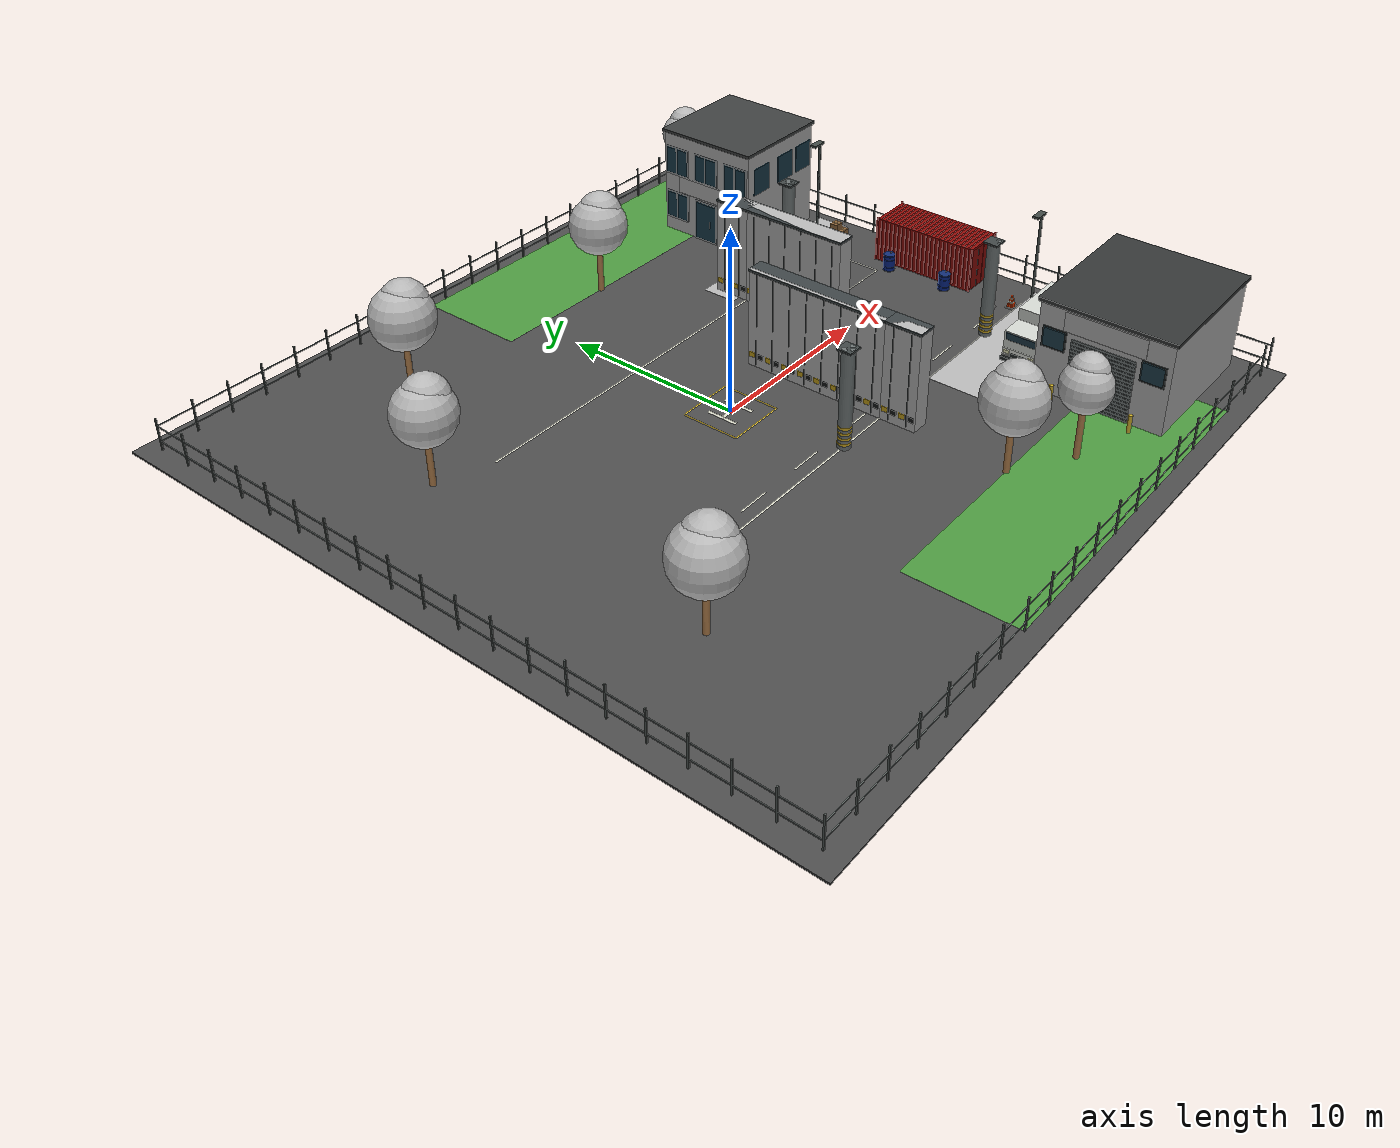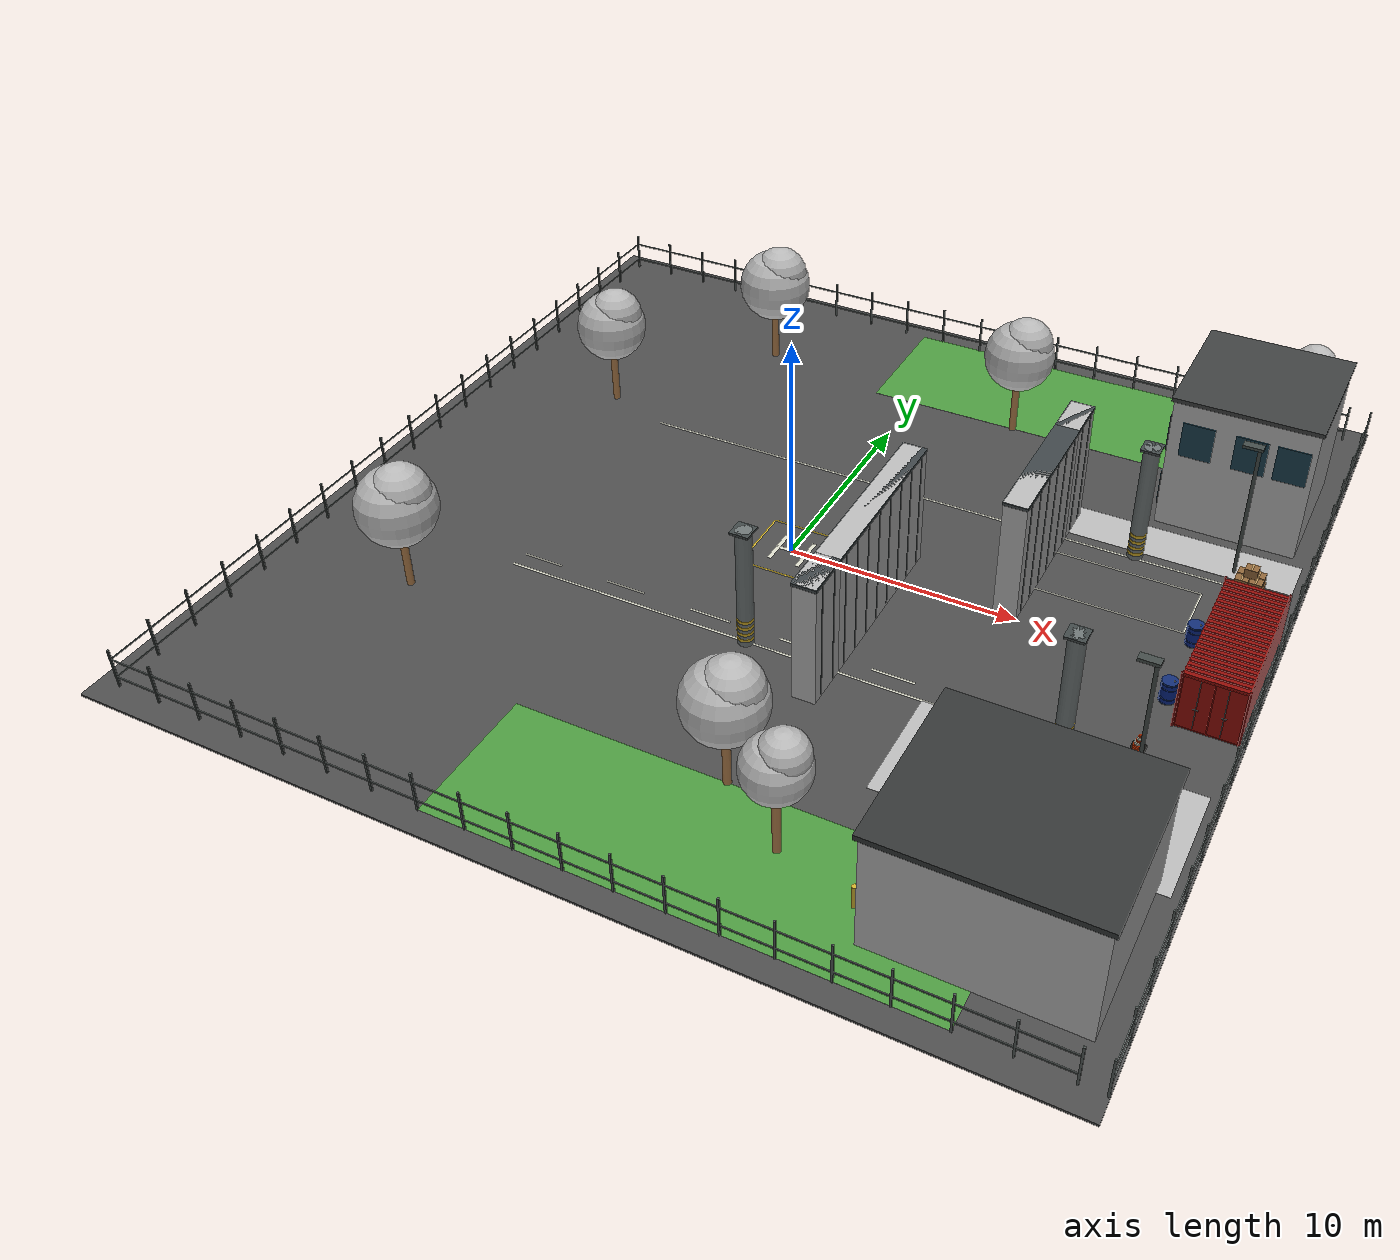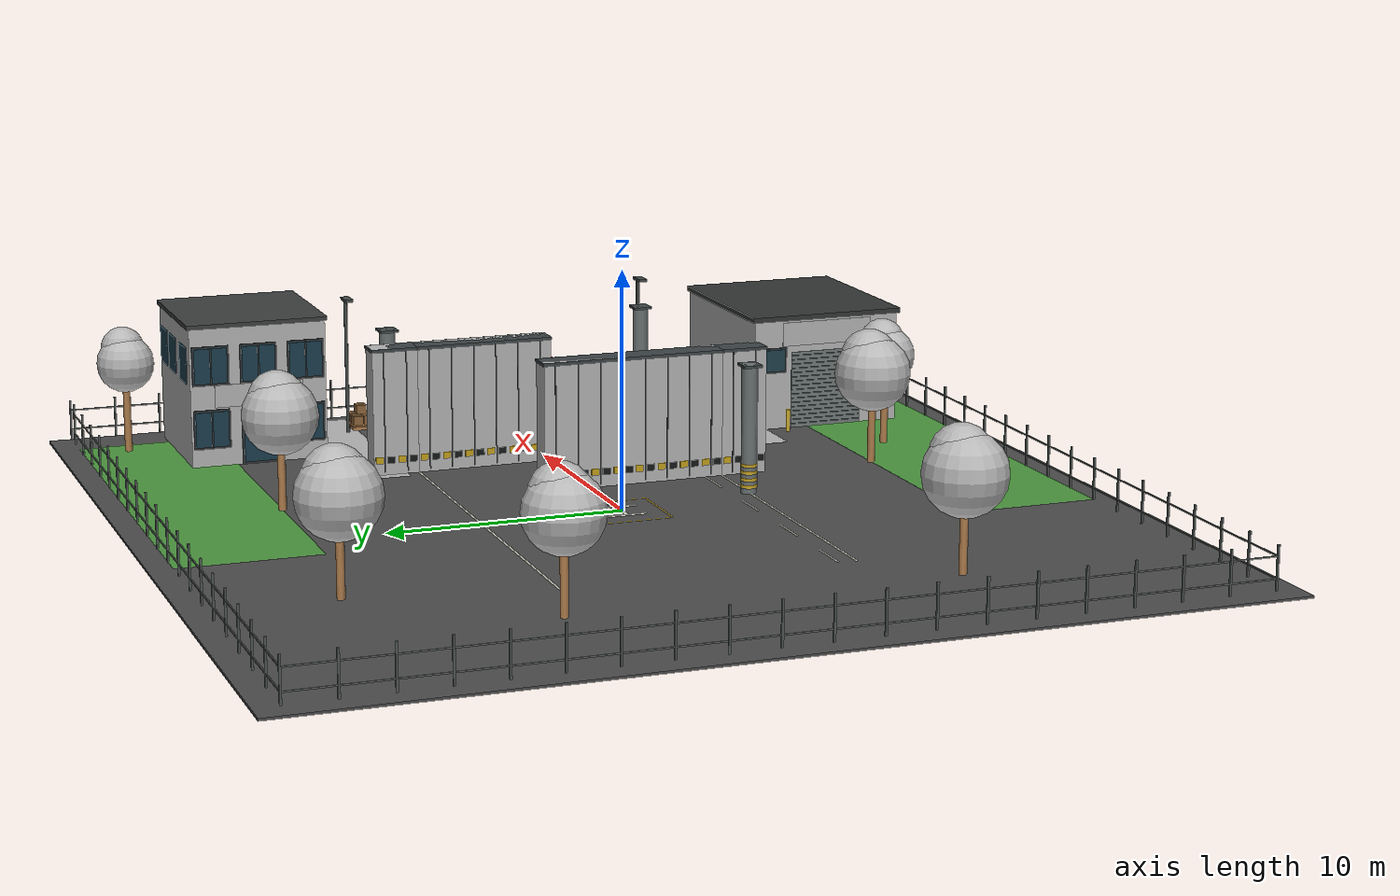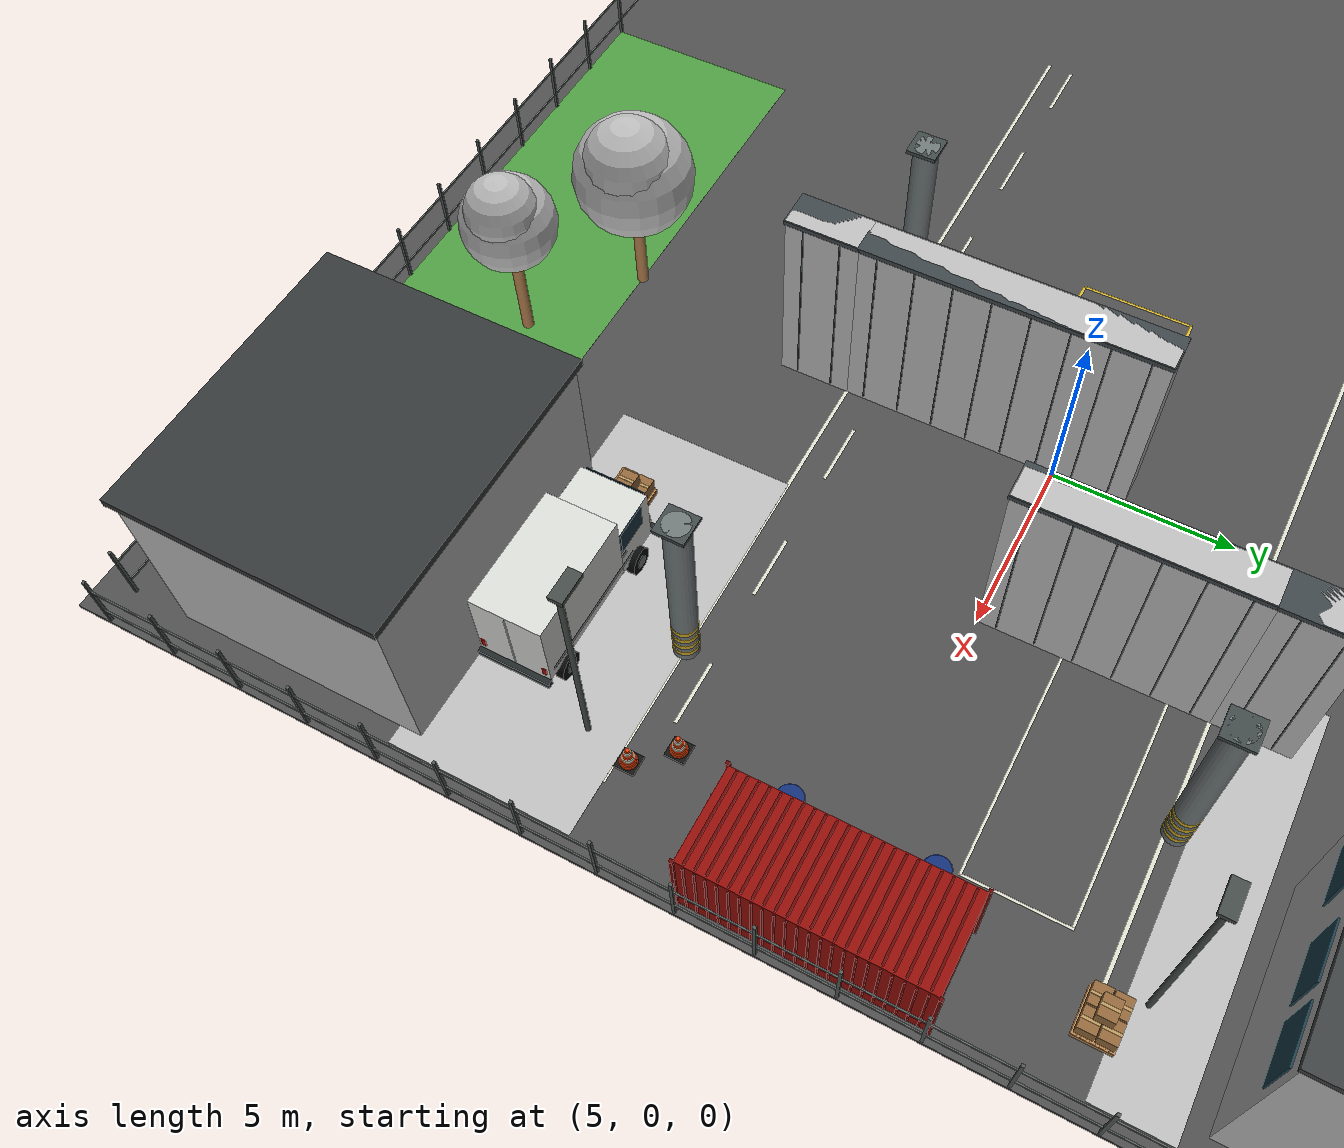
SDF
<?xml version='1.0' encoding='utf-8'?>
<sdf version="1.5"><world name="default"><include><uri>model://sun</uri></include><scene><ambient>.54 .56 .58 1</ambient><background>.66 .76 .85 1</background><shadows>true</shadows><fog><type>linear</type><color>.72 .78 .83 1</color><density>.001</density><start>70</start><end>150</end></fog></scene><physics name="default_physics" default="0" type="ode"><gravity>0 0 -9.8066</gravity><ode><solver><type>quick</type><iters>10</iters><sor>1.3</sor><use_dynamic_moi_rescaling>0</use_dynamic_moi_rescaling></solver><constraints><cfm>0</cfm><erp>0.2</erp><contact_max_correcting_vel>100</contact_max_correcting_vel><contact_surface_layer>0.001</contact_surface_layer></constraints></ode><max_step_size>0.004</max_step_size><real_time_factor>1</real_time_factor><real_time_update_rate>250</real_time_update_rate><magnetic_field>6.0e-6 2.3e-5 -4.2e-5</magnetic_field></physics><gui fullscreen="0"><camera name="yard_overview"><pose>-16 -24 23 0 .57 .76</pose><view_controller>orbit</view_controller></camera></gui><model name="yard_ground"><static>true</static><pose>0 0 0 0 0 0</pose><link name="structure"><visual name="solid_ground"><pose>0 0 -0.047 0 0 0</pose><geometry><box><size>40 40 0.1</size></box></geometry><cast_shadows>true</cast_shadows><material><script><uri>file:///home/fxxk/px4_agent/scene/materials/scripts</uri><uri>file:///home/fxxk/px4_agent/scene/materials/textures</uri><name>Yard/asphalt</name></script></material></visual><collision name="solid_ground_collision"><pose>0 0 -0.047 0 0 0</pose><geometry><box><size>40 40 0.1</size></box></geometry><surface><friction><ode><mu>1.0</mu><mu2>1.0</mu2></ode></friction></surface></collision><visual name="west_lawn"><pose>-12.5 0 0.0032 0 0 0</pose><geometry><plane><normal>0 0 1</normal><size>15 38</size></plane></geometry><cast_shadows>false</cast_shadows><material><script><uri>file:///home/fxxk/px4_agent/scene/materials/scripts</uri><uri>file:///home/fxxk/px4_agent/scene/materials/textures</uri><name>Yard/grass</name></script></material></visual><visual name="north_lawn"><pose>8 16 0.0032 0 0 0</pose><geometry><plane><normal>0 0 1</normal><size>20 6</size></plane></geometry><cast_shadows>false</cast_shadows><material><script><uri>file:///home/fxxk/px4_agent/scene/materials/scripts</uri><uri>file:///home/fxxk/px4_agent/scene/materials/textures</uri><name>Yard/grass</name></script></material></visual><visual name="south_lawn"><pose>5 -16 0.0032 0 0 0</pose><geometry><plane><normal>0 0 1</normal><size>20 6</size></plane></geometry><cast_shadows>false</cast_shadows><material><script><uri>file:///home/fxxk/px4_agent/scene/materials/scripts</uri><uri>file:///home/fxxk/px4_agent/scene/materials/textures</uri><name>Yard/grass</name></script></material></visual><visual name="warehouse_apron"><pose>14 -8.5 0.0032 0 0 0</pose><geometry><plane><normal>0 0 1</normal><size>11 5</size></plane></geometry><cast_shadows>false</cast_shadows><material><script><uri>file:///home/fxxk/px4_agent/scene/materials/scripts</uri><uri>file:///home/fxxk/px4_agent/scene/materials/textures</uri><name>Yard/concrete</name></script></material></visual><visual name="office_walkway"><pose>14 7.5 0.0032 0 0 0</pose><geometry><plane><normal>0 0 1</normal><size>11 2</size></plane></geometry><cast_shadows>false</cast_shadows><material><script><uri>file:///home/fxxk/px4_agent/scene/materials/scripts</uri><uri>file:///home/fxxk/px4_agent/scene/materials/textures</uri><name>Yard/concrete</name></script></material></visual><visual name="road_edge_0"><pose>4 -6 0.0033 0 0 0</pose><geometry><box><size>28 0.1 0.0001</size></box></geometry><cast_shadows>false</cast_shadows><material><ambient>0.85 0.85 0.79 1</ambient><diffuse>0.85 0.85 0.79 1</diffuse><specular>0.04 0.04 0.04 1</specular></material></visual><visual name="road_edge_1"><pose>4 6 0.0033 0 0 0</pose><geometry><box><size>28 0.1 0.0001</size></box></geometry><cast_shadows>false</cast_shadows><material><ambient>0.85 0.85 0.79 1</ambient><diffuse>0.85 0.85 0.79 1</diffuse><specular>0.04 0.04 0.04 1</specular></material></visual><visual name="lane_dash_0"><pose>-9 -5.25 0.0033 0 0 0</pose><geometry><box><size>1.8 0.09 0.0001</size></box></geometry><cast_shadows>false</cast_shadows><material><ambient>0.85 0.85 0.79 1</ambient><diffuse>0.85 0.85 0.79 1</diffuse><specular>0.04 0.04 0.04 1</specular></material></visual><visual name="lane_dash_1"><pose>-5 -5.25 0.0033 0 0 0</pose><geometry><box><size>1.8 0.09 0.0001</size></box></geometry><cast_shadows>false</cast_shadows><material><ambient>0.85 0.85 0.79 1</ambient><diffuse>0.85 0.85 0.79 1</diffuse><specular>0.04 0.04 0.04 1</specular></material></visual><visual name="lane_dash_2"><pose>-1 -5.25 0.0033 0 0 0</pose><geometry><box><size>1.8 0.09 0.0001</size></box></geometry><cast_shadows>false</cast_shadows><material><ambient>0.85 0.85 0.79 1</ambient><diffuse>0.85 0.85 0.79 1</diffuse><specular>0.04 0.04 0.04 1</specular></material></visual><visual name="lane_dash_3"><pose>3 -5.25 0.0033 0 0 0</pose><geometry><box><size>1.8 0.09 0.0001</size></box></geometry><cast_shadows>false</cast_shadows><material><ambient>0.85 0.85 0.79 1</ambient><diffuse>0.85 0.85 0.79 1</diffuse><specular>0.04 0.04 0.04 1</specular></material></visual><visual name="lane_dash_4"><pose>7 -5.25 0.0033 0 0 0</pose><geometry><box><size>1.8 0.09 0.0001</size></box></geometry><cast_shadows>false</cast_shadows><material><ambient>0.85 0.85 0.79 1</ambient><diffuse>0.85 0.85 0.79 1</diffuse><specular>0.04 0.04 0.04 1</specular></material></visual><visual name="lane_dash_5"><pose>11 -5.25 0.0033 0 0 0</pose><geometry><box><size>1.8 0.09 0.0001</size></box></geometry><cast_shadows>false</cast_shadows><material><ambient>0.85 0.85 0.79 1</ambient><diffuse>0.85 0.85 0.79 1</diffuse><specular>0.04 0.04 0.04 1</specular></material></visual><visual name="lane_dash_6"><pose>15 -5.25 0.0033 0 0 0</pose><geometry><box><size>1.8 0.09 0.0001</size></box></geometry><cast_shadows>false</cast_shadows><material><ambient>0.85 0.85 0.79 1</ambient><diffuse>0.85 0.85 0.79 1</diffuse><specular>0.04 0.04 0.04 1</specular></material></visual><visual name="parking_line_0"><pose>13 2.25 0.0033 0 0 0</pose><geometry><box><size>6.4 0.07 0.0001</size></box></geometry><cast_shadows>false</cast_shadows><material><ambient>0.85 0.85 0.79 1</ambient><diffuse>0.85 0.85 0.79 1</diffuse><specular>0.04 0.04 0.04 1</specular></material></visual><visual name="parking_line_1"><pose>13 4.95 0.0033 0 0 0</pose><geometry><box><size>6.4 0.07 0.0001</size></box></geometry><cast_shadows>false</cast_shadows><material><ambient>0.85 0.85 0.79 1</ambient><diffuse>0.85 0.85 0.79 1</diffuse><specular>0.04 0.04 0.04 1</specular></material></visual><visual name="parking_back"><pose>16.2 3.6 0.0033 0 0 0</pose><geometry><box><size>0.07 2.77 0.0001</size></box></geometry><cast_shadows>false</cast_shadows><material><ambient>0.85 0.85 0.79 1</ambient><diffuse>0.85 0.85 0.79 1</diffuse><specular>0.04 0.04 0.04 1</specular></material></visual><visual name="h_left"><pose>-0.65 0 0.0033 0 0 0</pose><geometry><box><size>0.18 1.7 0.0001</size></box></geometry><cast_shadows>false</cast_shadows><material><ambient>0.85 0.85 0.79 1</ambient><diffuse>0.85 0.85 0.79 1</diffuse><specular>0.04 0.04 0.04 1</specular></material></visual><visual name="h_right"><pose>0.65 0 0.0033 0 0 0</pose><geometry><box><size>0.18 1.7 0.0001</size></box></geometry><cast_shadows>false</cast_shadows><material><ambient>0.85 0.85 0.79 1</ambient><diffuse>0.85 0.85 0.79 1</diffuse><specular>0.04 0.04 0.04 1</specular></material></visual><visual name="h_middle"><pose>0 0 0.0033 0 0 0</pose><geometry><box><size>1.4 0.18 0.0001</size></box></geometry><cast_shadows>false</cast_shadows><material><ambient>0.85 0.85 0.79 1</ambient><diffuse>0.85 0.85 0.79 1</diffuse><specular>0.04 0.04 0.04 1</specular></material></visual><visual name="pad_border_0"><pose>0 -1.6 0.0033 0 0 0</pose><geometry><box><size>3.2 0.08 0.0001</size></box></geometry><cast_shadows>false</cast_shadows><material><ambient>0.82 0.7 0.18 1</ambient><diffuse>0.82 0.7 0.18 1</diffuse><specular>0.04 0.04 0.04 1</specular></material></visual><visual name="pad_border_1"><pose>0 1.6 0.0033 0 0 0</pose><geometry><box><size>3.2 0.08 0.0001</size></box></geometry><cast_shadows>false</cast_shadows><material><ambient>0.82 0.7 0.18 1</ambient><diffuse>0.82 0.7 0.18 1</diffuse><specular>0.04 0.04 0.04 1</specular></material></visual><visual name="pad_border_2"><pose>-1.6 0 0.0033 0 0 0</pose><geometry><box><size>0.08 3.2 0.0001</size></box></geometry><cast_shadows>false</cast_shadows><material><ambient>0.82 0.7 0.18 1</ambient><diffuse>0.82 0.7 0.18 1</diffuse><specular>0.04 0.04 0.04 1</specular></material></visual><visual name="pad_border_3"><pose>1.6 0 0.0033 0 0 0</pose><geometry><box><size>0.08 3.2 0.0001</size></box></geometry><cast_shadows>false</cast_shadows><material><ambient>0.82 0.7 0.18 1</ambient><diffuse>0.82 0.7 0.18 1</diffuse><specular>0.04 0.04 0.04 1</specular></material></visual></link></model><model name="obstacle_wall_1"><static>true</static><pose>4.5 -2 0.003 0 0 0</pose><link name="structure"><visual name="collision_wall"><pose>0 0 2.75 0 0 0</pose><geometry><box><size>1 8 5.5</size></box></geometry><cast_shadows>true</cast_shadows><material><script><uri>file:///home/fxxk/px4_agent/scene/materials/scripts</uri><uri>file:///home/fxxk/px4_agent/scene/materials/textures</uri><name>Yard/concrete</name></script></material></visual><collision name="collision_wall_collision"><pose>0 0 2.75 0 0 0</pose><geometry><box><size>1 8 5.5</size></box></geometry><surface><friction><ode><mu>1.0</mu><mu2>1.0</mu2></ode></friction></surface></collision><visual name="wall_coping"><pose>0 0 5.435 0 0 0</pose><geometry><box><size>1.06 8.06 0.13</size></box></geometry><cast_shadows>true</cast_shadows><material><ambient>0.24 0.27 0.28 1</ambient><diffuse>0.24 0.27 0.28 1</diffuse><specular>0.04 0.04 0.04 1</specular></material></visual><visual name="panel_joint_-1_0"><pose>-0.513 -3.5 2.75 0 0 0</pose><geometry><box><size>0.028 0.034 5.3</size></box></geometry><cast_shadows>true</cast_shadows><material><ambient>0.26 0.29 0.29 1</ambient><diffuse>0.26 0.29 0.29 1</diffuse><specular>0.04 0.04 0.04 1</specular></material></visual><visual name="panel_joint_1_0"><pose>0.513 -3.5 2.75 0 0 0</pose><geometry><box><size>0.028 0.034 5.3</size></box></geometry><cast_shadows>true</cast_shadows><material><ambient>0.26 0.29 0.29 1</ambient><diffuse>0.26 0.29 0.29 1</diffuse><specular>0.04 0.04 0.04 1</specular></material></visual><visual name="panel_joint_-1_1"><pose>-0.513 -2.5 2.75 0 0 0</pose><geometry><box><size>0.028 0.034 5.3</size></box></geometry><cast_shadows>true</cast_shadows><material><ambient>0.26 0.29 0.29 1</ambient><diffuse>0.26 0.29 0.29 1</diffuse><specular>0.04 0.04 0.04 1</specular></material></visual><visual name="panel_joint_1_1"><pose>0.513 -2.5 2.75 0 0 0</pose><geometry><box><size>0.028 0.034 5.3</size></box></geometry><cast_shadows>true</cast_shadows><material><ambient>0.26 0.29 0.29 1</ambient><diffuse>0.26 0.29 0.29 1</diffuse><specular>0.04 0.04 0.04 1</specular></material></visual><visual name="panel_joint_-1_2"><pose>-0.513 -1.5 2.75 0 0 0</pose><geometry><box><size>0.028 0.034 5.3</size></box></geometry><cast_shadows>true</cast_shadows><material><ambient>0.26 0.29 0.29 1</ambient><diffuse>0.26 0.29 0.29 1</diffuse><specular>0.04 0.04 0.04 1</specular></material></visual><visual name="panel_joint_1_2"><pose>0.513 -1.5 2.75 0 0 0</pose><geometry><box><size>0.028 0.034 5.3</size></box></geometry><cast_shadows>true</cast_shadows><material><ambient>0.26 0.29 0.29 1</ambient><diffuse>0.26 0.29 0.29 1</diffuse><specular>0.04 0.04 0.04 1</specular></material></visual><visual name="panel_joint_-1_3"><pose>-0.513 -0.5 2.75 0 0 0</pose><geometry><box><size>0.028 0.034 5.3</size></box></geometry><cast_shadows>true</cast_shadows><material><ambient>0.26 0.29 0.29 1</ambient><diffuse>0.26 0.29 0.29 1</diffuse><specular>0.04 0.04 0.04 1</specular></material></visual><visual name="panel_joint_1_3"><pose>0.513 -0.5 2.75 0 0 0</pose><geometry><box><size>0.028 0.034 5.3</size></box></geometry><cast_shadows>true</cast_shadows><material><ambient>0.26 0.29 0.29 1</ambient><diffuse>0.26 0.29 0.29 1</diffuse><specular>0.04 0.04 0.04 1</specular></material></visual><visual name="panel_joint_-1_4"><pose>-0.513 0.5 2.75 0 0 0</pose><geometry><box><size>0.028 0.034 5.3</size></box></geometry><cast_shadows>true</cast_shadows><material><ambient>0.26 0.29 0.29 1</ambient><diffuse>0.26 0.29 0.29 1</diffuse><specular>0.04 0.04 0.04 1</specular></material></visual><visual name="panel_joint_1_4"><pose>0.513 0.5 2.75 0 0 0</pose><geometry><box><size>0.028 0.034 5.3</size></box></geometry><cast_shadows>true</cast_shadows><material><ambient>0.26 0.29 0.29 1</ambient><diffuse>0.26 0.29 0.29 1</diffuse><specular>0.04 0.04 0.04 1</specular></material></visual><visual name="panel_joint_-1_5"><pose>-0.513 1.5 2.75 0 0 0</pose><geometry><box><size>0.028 0.034 5.3</size></box></geometry><cast_shadows>true</cast_shadows><material><ambient>0.26 0.29 0.29 1</ambient><diffuse>0.26 0.29 0.29 1</diffuse><specular>0.04 0.04 0.04 1</specular></material></visual><visual name="panel_joint_1_5"><pose>0.513 1.5 2.75 0 0 0</pose><geometry><box><size>0.028 0.034 5.3</size></box></geometry><cast_shadows>true</cast_shadows><material><ambient>0.26 0.29 0.29 1</ambient><diffuse>0.26 0.29 0.29 1</diffuse><specular>0.04 0.04 0.04 1</specular></material></visual><visual name="panel_joint_-1_6"><pose>-0.513 2.5 2.75 0 0 0</pose><geometry><box><size>0.028 0.034 5.3</size></box></geometry><cast_shadows>true</cast_shadows><material><ambient>0.26 0.29 0.29 1</ambient><diffuse>0.26 0.29 0.29 1</diffuse><specular>0.04 0.04 0.04 1</specular></material></visual><visual name="panel_joint_1_6"><pose>0.513 2.5 2.75 0 0 0</pose><geometry><box><size>0.028 0.034 5.3</size></box></geometry><cast_shadows>true</cast_shadows><material><ambient>0.26 0.29 0.29 1</ambient><diffuse>0.26 0.29 0.29 1</diffuse><specular>0.04 0.04 0.04 1</specular></material></visual><visual name="panel_joint_-1_7"><pose>-0.513 3.5 2.75 0 0 0</pose><geometry><box><size>0.028 0.034 5.3</size></box></geometry><cast_shadows>true</cast_shadows><material><ambient>0.26 0.29 0.29 1</ambient><diffuse>0.26 0.29 0.29 1</diffuse><specular>0.04 0.04 0.04 1</specular></material></visual><visual name="panel_joint_1_7"><pose>0.513 3.5 2.75 0 0 0</pose><geometry><box><size>0.028 0.034 5.3</size></box></geometry><cast_shadows>true</cast_shadows><material><ambient>0.26 0.29 0.29 1</ambient><diffuse>0.26 0.29 0.29 1</diffuse><specular>0.04 0.04 0.04 1</specular></material></visual><visual name="safety_band_0"><pose>-0.517 -3.75 0.65 0 0 0</pose><geometry><box><size>0.025 0.34 0.28</size></box></geometry><cast_shadows>true</cast_shadows><material><ambient>0.075 0.085 0.085 1</ambient><diffuse>0.075 0.085 0.085 1</diffuse><specular>0.04 0.04 0.04 1</specular></material></visual><visual name="safety_band_1"><pose>-0.517 -3.25 0.65 0 0 0</pose><geometry><box><size>0.025 0.34 0.28</size></box></geometry><cast_shadows>true</cast_shadows><material><ambient>0.78 0.64 0.1 1</ambient><diffuse>0.78 0.64 0.1 1</diffuse><specular>0.04 0.04 0.04 1</specular></material></visual><visual name="safety_band_2"><pose>-0.517 -2.75 0.65 0 0 0</pose><geometry><box><size>0.025 0.34 0.28</size></box></geometry><cast_shadows>true</cast_shadows><material><ambient>0.075 0.085 0.085 1</ambient><diffuse>0.075 0.085 0.085 1</diffuse><specular>0.04 0.04 0.04 1</specular></material></visual><visual name="safety_band_3"><pose>-0.517 -2.25 0.65 0 0 0</pose><geometry><box><size>0.025 0.34 0.28</size></box></geometry><cast_shadows>true</cast_shadows><material><ambient>0.78 0.64 0.1 1</ambient><diffuse>0.78 0.64 0.1 1</diffuse><specular>0.04 0.04 0.04 1</specular></material></visual><visual name="safety_band_4"><pose>-0.517 -1.75 0.65 0 0 0</pose><geometry><box><size>0.025 0.34 0.28</size></box></geometry><cast_shadows>true</cast_shadows><material><ambient>0.075 0.085 0.085 1</ambient><diffuse>0.075 0.085 0.085 1</diffuse><specular>0.04 0.04 0.04 1</specular></material></visual><visual name="safety_band_5"><pose>-0.517 -1.25 0.65 0 0 0</pose><geometry><box><size>0.025 0.34 0.28</size></box></geometry><cast_shadows>true</cast_shadows><material><ambient>0.78 0.64 0.1 1</ambient><diffuse>0.78 0.64 0.1 1</diffuse><specular>0.04 0.04 0.04 1</specular></material></visual><visual name="safety_band_6"><pose>-0.517 -0.75 0.65 0 0 0</pose><geometry><box><size>0.025 0.34 0.28</size></box></geometry><cast_shadows>true</cast_shadows><material><ambient>0.075 0.085 0.085 1</ambient><diffuse>0.075 0.085 0.085 1</diffuse><specular>0.04 0.04 0.04 1</specular></material></visual><visual name="safety_band_7"><pose>-0.517 -0.25 0.65 0 0 0</pose><geometry><box><size>0.025 0.34 0.28</size></box></geometry><cast_shadows>true</cast_shadows><material><ambient>0.78 0.64 0.1 1</ambient><diffuse>0.78 0.64 0.1 1</diffuse><specular>0.04 0.04 0.04 1</specular></material></visual><visual name="safety_band_8"><pose>-0.517 0.25 0.65 0 0 0</pose><geometry><box><size>0.025 0.34 0.28</size></box></geometry><cast_shadows>true</cast_shadows><material><ambient>0.075 0.085 0.085 1</ambient><diffuse>0.075 0.085 0.085 1</diffuse><specular>0.04 0.04 0.04 1</specular></material></visual><visual name="safety_band_9"><pose>-0.517 0.75 0.65 0 0 0</pose><geometry><box><size>0.025 0.34 0.28</size></box></geometry><cast_shadows>true</cast_shadows><material><ambient>0.78 0.64 0.1 1</ambient><diffuse>0.78 0.64 0.1 1</diffuse><specular>0.04 0.04 0.04 1</specular></material></visual><visual name="safety_band_10"><pose>-0.517 1.25 0.65 0 0 0</pose><geometry><box><size>0.025 0.34 0.28</size></box></geometry><cast_shadows>true</cast_shadows><material><ambient>0.075 0.085 0.085 1</ambient><diffuse>0.075 0.085 0.085 1</diffuse><specular>0.04 0.04 0.04 1</specular></material></visual><visual name="safety_band_11"><pose>-0.517 1.75 0.65 0 0 0</pose><geometry><box><size>0.025 0.34 0.28</size></box></geometry><cast_shadows>true</cast_shadows><material><ambient>0.78 0.64 0.1 1</ambient><diffuse>0.78 0.64 0.1 1</diffuse><specular>0.04 0.04 0.04 1</specular></material></visual><visual name="safety_band_12"><pose>-0.517 2.25 0.65 0 0 0</pose><geometry><box><size>0.025 0.34 0.28</size></box></geometry><cast_shadows>true</cast_shadows><material><ambient>0.075 0.085 0.085 1</ambient><diffuse>0.075 0.085 0.085 1</diffuse><specular>0.04 0.04 0.04 1</specular></material></visual><visual name="safety_band_13"><pose>-0.517 2.75 0.65 0 0 0</pose><geometry><box><size>0.025 0.34 0.28</size></box></geometry><cast_shadows>true</cast_shadows><material><ambient>0.78 0.64 0.1 1</ambient><diffuse>0.78 0.64 0.1 1</diffuse><specular>0.04 0.04 0.04 1</specular></material></visual><visual name="safety_band_14"><pose>-0.517 3.25 0.65 0 0 0</pose><geometry><box><size>0.025 0.34 0.28</size></box></geometry><cast_shadows>true</cast_shadows><material><ambient>0.075 0.085 0.085 1</ambient><diffuse>0.075 0.085 0.085 1</diffuse><specular>0.04 0.04 0.04 1</specular></material></visual><visual name="safety_band_15"><pose>-0.517 3.75 0.65 0 0 0</pose><geometry><box><size>0.025 0.34 0.28</size></box></geometry><cast_shadows>true</cast_shadows><material><ambient>0.78 0.64 0.1 1</ambient><diffuse>0.78 0.64 0.1 1</diffuse><specular>0.04 0.04 0.04 1</specular></material></visual></link></model><model name="obstacle_wall_2"><static>true</static><pose>9.5 3 0.003 0 0 0</pose><link name="structure"><visual name="collision_wall"><pose>0 0 2.75 0 0 0</pose><geometry><box><size>1 6 5.5</size></box></geometry><cast_shadows>true</cast_shadows><material><script><uri>file:///home/fxxk/px4_agent/scene/materials/scripts</uri><uri>file:///home/fxxk/px4_agent/scene/materials/textures</uri><name>Yard/concrete</name></script></material></visual><collision name="collision_wall_collision"><pose>0 0 2.75 0 0 0</pose><geometry><box><size>1 6 5.5</size></box></geometry><surface><friction><ode><mu>1.0</mu><mu2>1.0</mu2></ode></friction></surface></collision><visual name="wall_coping"><pose>0 0 5.435 0 0 0</pose><geometry><box><size>1.06 6.06 0.13</size></box></geometry><cast_shadows>true</cast_shadows><material><ambient>0.24 0.27 0.28 1</ambient><diffuse>0.24 0.27 0.28 1</diffuse><specular>0.04 0.04 0.04 1</specular></material></visual><visual name="panel_joint_-1_0"><pose>-0.513 -2.5 2.75 0 0 0</pose><geometry><box><size>0.028 0.034 5.3</size></box></geometry><cast_shadows>true</cast_shadows><material><ambient>0.26 0.29 0.29 1</ambient><diffuse>0.26 0.29 0.29 1</diffuse><specular>0.04 0.04 0.04 1</specular></material></visual><visual name="panel_joint_1_0"><pose>0.513 -2.5 2.75 0 0 0</pose><geometry><box><size>0.028 0.034 5.3</size></box></geometry><cast_shadows>true</cast_shadows><material><ambient>0.26 0.29 0.29 1</ambient><diffuse>0.26 0.29 0.29 1</diffuse><specular>0.04 0.04 0.04 1</specular></material></visual><visual name="panel_joint_-1_1"><pose>-0.513 -1.5 2.75 0 0 0</pose><geometry><box><size>0.028 0.034 5.3</size></box></geometry><cast_shadows>true</cast_shadows><material><ambient>0.26 0.29 0.29 1</ambient><diffuse>0.26 0.29 0.29 1</diffuse><specular>0.04 0.04 0.04 1</specular></material></visual><visual name="panel_joint_1_1"><pose>0.513 -1.5 2.75 0 0 0</pose><geometry><box><size>0.028 0.034 5.3</size></box></geometry><cast_shadows>true</cast_shadows><material><ambient>0.26 0.29 0.29 1</ambient><diffuse>0.26 0.29 0.29 1</diffuse><specular>0.04 0.04 0.04 1</specular></material></visual><visual name="panel_joint_-1_2"><pose>-0.513 -0.5 2.75 0 0 0</pose><geometry><box><size>0.028 0.034 5.3</size></box></geometry><cast_shadows>true</cast_shadows><material><ambient>0.26 0.29 0.29 1</ambient><diffuse>0.26 0.29 0.29 1</diffuse><specular>0.04 0.04 0.04 1</specular></material></visual><visual name="panel_joint_1_2"><pose>0.513 -0.5 2.75 0 0 0</pose><geometry><box><size>0.028 0.034 5.3</size></box></geometry><cast_shadows>true</cast_shadows><material><ambient>0.26 0.29 0.29 1</ambient><diffuse>0.26 0.29 0.29 1</diffuse><specular>0.04 0.04 0.04 1</specular></material></visual><visual name="panel_joint_-1_3"><pose>-0.513 0.5 2.75 0 0 0</pose><geometry><box><size>0.028 0.034 5.3</size></box></geometry><cast_shadows>true</cast_shadows><material><ambient>0.26 0.29 0.29 1</ambient><diffuse>0.26 0.29 0.29 1</diffuse><specular>0.04 0.04 0.04 1</specular></material></visual><visual name="panel_joint_1_3"><pose>0.513 0.5 2.75 0 0 0</pose><geometry><box><size>0.028 0.034 5.3</size></box></geometry><cast_shadows>true</cast_shadows><material><ambient>0.26 0.29 0.29 1</ambient><diffuse>0.26 0.29 0.29 1</diffuse><specular>0.04 0.04 0.04 1</specular></material></visual><visual name="panel_joint_-1_4"><pose>-0.513 1.5 2.75 0 0 0</pose><geometry><box><size>0.028 0.034 5.3</size></box></geometry><cast_shadows>true</cast_shadows><material><ambient>0.26 0.29 0.29 1</ambient><diffuse>0.26 0.29 0.29 1</diffuse><specular>0.04 0.04 0.04 1</specular></material></visual><visual name="panel_joint_1_4"><pose>0.513 1.5 2.75 0 0 0</pose><geometry><box><size>0.028 0.034 5.3</size></box></geometry><cast_shadows>true</cast_shadows><material><ambient>0.26 0.29 0.29 1</ambient><diffuse>0.26 0.29 0.29 1</diffuse><specular>0.04 0.04 0.04 1</specular></material></visual><visual name="panel_joint_-1_5"><pose>-0.513 2.5 2.75 0 0 0</pose><geometry><box><size>0.028 0.034 5.3</size></box></geometry><cast_shadows>true</cast_shadows><material><ambient>0.26 0.29 0.29 1</ambient><diffuse>0.26 0.29 0.29 1</diffuse><specular>0.04 0.04 0.04 1</specular></material></visual><visual name="panel_joint_1_5"><pose>0.513 2.5 2.75 0 0 0</pose><geometry><box><size>0.028 0.034 5.3</size></box></geometry><cast_shadows>true</cast_shadows><material><ambient>0.26 0.29 0.29 1</ambient><diffuse>0.26 0.29 0.29 1</diffuse><specular>0.04 0.04 0.04 1</specular></material></visual><visual name="safety_band_0"><pose>-0.517 -2.75 0.65 0 0 0</pose><geometry><box><size>0.025 0.34 0.28</size></box></geometry><cast_shadows>true</cast_shadows><material><ambient>0.075 0.085 0.085 1</ambient><diffuse>0.075 0.085 0.085 1</diffuse><specular>0.04 0.04 0.04 1</specular></material></visual><visual name="safety_band_1"><pose>-0.517 -2.25 0.65 0 0 0</pose><geometry><box><size>0.025 0.34 0.28</size></box></geometry><cast_shadows>true</cast_shadows><material><ambient>0.78 0.64 0.1 1</ambient><diffuse>0.78 0.64 0.1 1</diffuse><specular>0.04 0.04 0.04 1</specular></material></visual><visual name="safety_band_2"><pose>-0.517 -1.75 0.65 0 0 0</pose><geometry><box><size>0.025 0.34 0.28</size></box></geometry><cast_shadows>true</cast_shadows><material><ambient>0.075 0.085 0.085 1</ambient><diffuse>0.075 0.085 0.085 1</diffuse><specular>0.04 0.04 0.04 1</specular></material></visual><visual name="safety_band_3"><pose>-0.517 -1.25 0.65 0 0 0</pose><geometry><box><size>0.025 0.34 0.28</size></box></geometry><cast_shadows>true</cast_shadows><material><ambient>0.78 0.64 0.1 1</ambient><diffuse>0.78 0.64 0.1 1</diffuse><specular>0.04 0.04 0.04 1</specular></material></visual><visual name="safety_band_4"><pose>-0.517 -0.75 0.65 0 0 0</pose><geometry><box><size>0.025 0.34 0.28</size></box></geometry><cast_shadows>true</cast_shadows><material><ambient>0.075 0.085 0.085 1</ambient><diffuse>0.075 0.085 0.085 1</diffuse><specular>0.04 0.04 0.04 1</specular></material></visual><visual name="safety_band_5"><pose>-0.517 -0.25 0.65 0 0 0</pose><geometry><box><size>0.025 0.34 0.28</size></box></geometry><cast_shadows>true</cast_shadows><material><ambient>0.78 0.64 0.1 1</ambient><diffuse>0.78 0.64 0.1 1</diffuse><specular>0.04 0.04 0.04 1</specular></material></visual><visual name="safety_band_6"><pose>-0.517 0.25 0.65 0 0 0</pose><geometry><box><size>0.025 0.34 0.28</size></box></geometry><cast_shadows>true</cast_shadows><material><ambient>0.075 0.085 0.085 1</ambient><diffuse>0.075 0.085 0.085 1</diffuse><specular>0.04 0.04 0.04 1</specular></material></visual><visual name="safety_band_7"><pose>-0.517 0.75 0.65 0 0 0</pose><geometry><box><size>0.025 0.34 0.28</size></box></geometry><cast_shadows>true</cast_shadows><material><ambient>0.78 0.64 0.1 1</ambient><diffuse>0.78 0.64 0.1 1</diffuse><specular>0.04 0.04 0.04 1</specular></material></visual><visual name="safety_band_8"><pose>-0.517 1.25 0.65 0 0 0</pose><geometry><box><size>0.025 0.34 0.28</size></box></geometry><cast_shadows>true</cast_shadows><material><ambient>0.075 0.085 0.085 1</ambient><diffuse>0.075 0.085 0.085 1</diffuse><specular>0.04 0.04 0.04 1</specular></material></visual><visual name="safety_band_9"><pose>-0.517 1.75 0.65 0 0 0</pose><geometry><box><size>0.025 0.34 0.28</size></box></geometry><cast_shadows>true</cast_shadows><material><ambient>0.78 0.64 0.1 1</ambient><diffuse>0.78 0.64 0.1 1</diffuse><specular>0.04 0.04 0.04 1</specular></material></visual><visual name="safety_band_10"><pose>-0.517 2.25 0.65 0 0 0</pose><geometry><box><size>0.025 0.34 0.28</size></box></geometry><cast_shadows>true</cast_shadows><material><ambient>0.075 0.085 0.085 1</ambient><diffuse>0.075 0.085 0.085 1</diffuse><specular>0.04 0.04 0.04 1</specular></material></visual><visual name="safety_band_11"><pose>-0.517 2.75 0.65 0 0 0</pose><geometry><box><size>0.025 0.34 0.28</size></box></geometry><cast_shadows>true</cast_shadows><material><ambient>0.78 0.64 0.1 1</ambient><diffuse>0.78 0.64 0.1 1</diffuse><specular>0.04 0.04 0.04 1</specular></material></visual></link></model><model name="south_boundary_cargo_stack"><static>true</static><pose>4.5 -7 0.003 0 0 0</pose><link name="structure"><visual name="collision_wall"><pose>0 0 2.75 0 0 0</pose><geometry><box><size>1 2 5.5</size></box></geometry><cast_shadows>true</cast_shadows><material><script><uri>file:///home/fxxk/px4_agent/scene/materials/scripts</uri><uri>file:///home/fxxk/px4_agent/scene/materials/textures</uri><name>Yard/concrete</name></script></material></visual><collision name="collision_wall_collision"><pose>0 0 2.75 0 0 0</pose><geometry><box><size>1 2 5.5</size></box></geometry><surface><friction><ode><mu>1.0</mu><mu2>1.0</mu2></ode></friction></surface></collision><visual name="wall_coping"><pose>0 0 5.435 0 0 0</pose><geometry><box><size>1.06 2.06 0.13</size></box></geometry><cast_shadows>true</cast_shadows><material><ambient>0.24 0.27 0.28 1</ambient><diffuse>0.24 0.27 0.28 1</diffuse><specular>0.04 0.04 0.04 1</specular></material></visual><visual name="panel_joint_-1_0"><pose>-0.513 -0.5 2.75 0 0 0</pose><geometry><box><size>0.028 0.034 5.3</size></box></geometry><cast_shadows>true</cast_shadows><material><ambient>0.26 0.29 0.29 1</ambient><diffuse>0.26 0.29 0.29 1</diffuse><specular>0.04 0.04 0.04 1</specular></material></visual><visual name="panel_joint_1_0"><pose>0.513 -0.5 2.75 0 0 0</pose><geometry><box><size>0.028 0.034 5.3</size></box></geometry><cast_shadows>true</cast_shadows><material><ambient>0.26 0.29 0.29 1</ambient><diffuse>0.26 0.29 0.29 1</diffuse><specular>0.04 0.04 0.04 1</specular></material></visual><visual name="panel_joint_-1_1"><pose>-0.513 0.5 2.75 0 0 0</pose><geometry><box><size>0.028 0.034 5.3</size></box></geometry><cast_shadows>true</cast_shadows><material><ambient>0.26 0.29 0.29 1</ambient><diffuse>0.26 0.29 0.29 1</diffuse><specular>0.04 0.04 0.04 1</specular></material></visual><visual name="panel_joint_1_1"><pose>0.513 0.5 2.75 0 0 0</pose><geometry><box><size>0.028 0.034 5.3</size></box></geometry><cast_shadows>true</cast_shadows><material><ambient>0.26 0.29 0.29 1</ambient><diffuse>0.26 0.29 0.29 1</diffuse><specular>0.04 0.04 0.04 1</specular></material></visual><visual name="safety_band_0"><pose>-0.517 -0.75 0.65 0 0 0</pose><geometry><box><size>0.025 0.34 0.28</size></box></geometry><cast_shadows>true</cast_shadows><material><ambient>0.075 0.085 0.085 1</ambient><diffuse>0.075 0.085 0.085 1</diffuse><specular>0.04 0.04 0.04 1</specular></material></visual><visual name="safety_band_1"><pose>-0.517 -0.25 0.65 0 0 0</pose><geometry><box><size>0.025 0.34 0.28</size></box></geometry><cast_shadows>true</cast_shadows><material><ambient>0.78 0.64 0.1 1</ambient><diffuse>0.78 0.64 0.1 1</diffuse><specular>0.04 0.04 0.04 1</specular></material></visual><visual name="safety_band_2"><pose>-0.517 0.25 0.65 0 0 0</pose><geometry><box><size>0.025 0.34 0.28</size></box></geometry><cast_shadows>true</cast_shadows><material><ambient>0.075 0.085 0.085 1</ambient><diffuse>0.075 0.085 0.085 1</diffuse><specular>0.04 0.04 0.04 1</specular></material></visual><visual name="safety_band_3"><pose>-0.517 0.75 0.65 0 0 0</pose><geometry><box><size>0.025 0.34 0.28</size></box></geometry><cast_shadows>true</cast_shadows><material><ambient>0.78 0.64 0.1 1</ambient><diffuse>0.78 0.64 0.1 1</diffuse><specular>0.04 0.04 0.04 1</specular></material></visual></link></model><model name="north_boundary_cargo_stack"><static>true</static><pose>9.5 7 0.003 0 0 0</pose><link name="structure"><visual name="collision_wall"><pose>0 0 2.75 0 0 0</pose><geometry><box><size>1 2 5.5</size></box></geometry><cast_shadows>true</cast_shadows><material><script><uri>file:///home/fxxk/px4_agent/scene/materials/scripts</uri><uri>file:///home/fxxk/px4_agent/scene/materials/textures</uri><name>Yard/concrete</name></script></material></visual><collision name="collision_wall_collision"><pose>0 0 2.75 0 0 0</pose><geometry><box><size>1 2 5.5</size></box></geometry><surface><friction><ode><mu>1.0</mu><mu2>1.0</mu2></ode></friction></surface></collision><visual name="wall_coping"><pose>0 0 5.435 0 0 0</pose><geometry><box><size>1.06 2.06 0.13</size></box></geometry><cast_shadows>true</cast_shadows><material><ambient>0.24 0.27 0.28 1</ambient><diffuse>0.24 0.27 0.28 1</diffuse><specular>0.04 0.04 0.04 1</specular></material></visual><visual name="panel_joint_-1_0"><pose>-0.513 -0.5 2.75 0 0 0</pose><geometry><box><size>0.028 0.034 5.3</size></box></geometry><cast_shadows>true</cast_shadows><material><ambient>0.26 0.29 0.29 1</ambient><diffuse>0.26 0.29 0.29 1</diffuse><specular>0.04 0.04 0.04 1</specular></material></visual><visual name="panel_joint_1_0"><pose>0.513 -0.5 2.75 0 0 0</pose><geometry><box><size>0.028 0.034 5.3</size></box></geometry><cast_shadows>true</cast_shadows><material><ambient>0.26 0.29 0.29 1</ambient><diffuse>0.26 0.29 0.29 1</diffuse><specular>0.04 0.04 0.04 1</specular></material></visual><visual name="panel_joint_-1_1"><pose>-0.513 0.5 2.75 0 0 0</pose><geometry><box><size>0.028 0.034 5.3</size></box></geometry><cast_shadows>true</cast_shadows><material><ambient>0.26 0.29 0.29 1</ambient><diffuse>0.26 0.29 0.29 1</diffuse><specular>0.04 0.04 0.04 1</specular></material></visual><visual name="panel_joint_1_1"><pose>0.513 0.5 2.75 0 0 0</pose><geometry><box><size>0.028 0.034 5.3</size></box></geometry><cast_shadows>true</cast_shadows><material><ambient>0.26 0.29 0.29 1</ambient><diffuse>0.26 0.29 0.29 1</diffuse><specular>0.04 0.04 0.04 1</specular></material></visual><visual name="safety_band_0"><pose>-0.517 -0.75 0.65 0 0 0</pose><geometry><box><size>0.025 0.34 0.28</size></box></geometry><cast_shadows>true</cast_shadows><material><ambient>0.075 0.085 0.085 1</ambient><diffuse>0.075 0.085 0.085 1</diffuse><specular>0.04 0.04 0.04 1</specular></material></visual><visual name="safety_band_1"><pose>-0.517 -0.25 0.65 0 0 0</pose><geometry><box><size>0.025 0.34 0.28</size></box></geometry><cast_shadows>true</cast_shadows><material><ambient>0.78 0.64 0.1 1</ambient><diffuse>0.78 0.64 0.1 1</diffuse><specular>0.04 0.04 0.04 1</specular></material></visual><visual name="safety_band_2"><pose>-0.517 0.25 0.65 0 0 0</pose><geometry><box><size>0.025 0.34 0.28</size></box></geometry><cast_shadows>true</cast_shadows><material><ambient>0.075 0.085 0.085 1</ambient><diffuse>0.075 0.085 0.085 1</diffuse><specular>0.04 0.04 0.04 1</specular></material></visual><visual name="safety_band_3"><pose>-0.517 0.75 0.65 0 0 0</pose><geometry><box><size>0.025 0.34 0.28</size></box></geometry><cast_shadows>true</cast_shadows><material><ambient>0.78 0.64 0.1 1</ambient><diffuse>0.78 0.64 0.1 1</diffuse><specular>0.04 0.04 0.04 1</specular></material></visual></link></model><model name="utility_pillar_southwest"><static>true</static><pose>1 -6 0.003 0 0 0</pose><link name="structure"><visual name="tall_pillar"><pose>0 0 2.75 0 0 0</pose><geometry><cylinder><radius>0.34</radius><length>5.5</length></cylinder></geometry><cast_shadows>true</cast_shadows><material><ambient>0.43 0.46 0.46 1</ambient><diffuse>0.43 0.46 0.46 1</diffuse><specular>0.04 0.04 0.04 1</specular></material></visual><collision name="tall_pillar_collision"><pose>0 0 2.75 0 0 0</pose><geometry><cylinder><radius>0.34</radius><length>5.5</length></cylinder></geometry><surface><friction><ode><mu>1.0</mu><mu2>1.0</mu2></ode></friction></surface></collision><visual name="top_cap"><pose>0 0 5.45 0 0 0</pose><geometry><box><size>0.8 0.8 0.1</size></box></geometry><cast_shadows>true</cast_shadows><material><ambient>0.25 0.28 0.28 1</ambient><diffuse>0.25 0.28 0.28 1</diffuse><specular>0.04 0.04 0.04 1</specular></material></visual><visual name="hazard_ring_0"><pose>0 0 0.3 0 0 0</pose><geometry><cylinder><radius>0.345</radius><length>0.14</length></cylinder></geometry><cast_shadows>true</cast_shadows><material><ambient>0.8 0.66 0.14 1</ambient><diffuse>0.8 0.66 0.14 1</diffuse><specular>0.04 0.04 0.04 1</specular></material></visual><visual name="hazard_ring_1"><pose>0 0 0.6 0 0 0</pose><geometry><cylinder><radius>0.345</radius><length>0.14</length></cylinder></geometry><cast_shadows>true</cast_shadows><material><ambient>0.8 0.66 0.14 1</ambient><diffuse>0.8 0.66 0.14 1</diffuse><specular>0.04 0.04 0.04 1</specular></material></visual><visual name="hazard_ring_2"><pose>0 0 0.9 0 0 0</pose><geometry><cylinder><radius>0.345</radius><length>0.14</length></cylinder></geometry><cast_shadows>true</cast_shadows><material><ambient>0.8 0.66 0.14 1</ambient><diffuse>0.8 0.66 0.14 1</diffuse><specular>0.04 0.04 0.04 1</specular></material></visual><visual name="hazard_ring_3"><pose>0 0 1.2 0 0 0</pose><geometry><cylinder><radius>0.345</radius><length>0.14</length></cylinder></geometry><cast_shadows>true</cast_shadows><material><ambient>0.8 0.66 0.14 1</ambient><diffuse>0.8 0.66 0.14 1</diffuse><specular>0.04 0.04 0.04 1</specular></material></visual></link></model><model name="utility_pillar_northeast"><static>true</static><pose>13 6.2 0.003 0 0 0</pose><link name="structure"><visual name="tall_pillar"><pose>0 0 2.75 0 0 0</pose><geometry><cylinder><radius>0.34</radius><length>5.5</length></cylinder></geometry><cast_shadows>true</cast_shadows><material><ambient>0.43 0.46 0.46 1</ambient><diffuse>0.43 0.46 0.46 1</diffuse><specular>0.04 0.04 0.04 1</specular></material></visual><collision name="tall_pillar_collision"><pose>0 0 2.75 0 0 0</pose><geometry><cylinder><radius>0.34</radius><length>5.5</length></cylinder></geometry><surface><friction><ode><mu>1.0</mu><mu2>1.0</mu2></ode></friction></surface></collision><visual name="top_cap"><pose>0 0 5.45 0 0 0</pose><geometry><box><size>0.8 0.8 0.1</size></box></geometry><cast_shadows>true</cast_shadows><material><ambient>0.25 0.28 0.28 1</ambient><diffuse>0.25 0.28 0.28 1</diffuse><specular>0.04 0.04 0.04 1</specular></material></visual><visual name="hazard_ring_0"><pose>0 0 0.3 0 0 0</pose><geometry><cylinder><radius>0.345</radius><length>0.14</length></cylinder></geometry><cast_shadows>true</cast_shadows><material><ambient>0.8 0.66 0.14 1</ambient><diffuse>0.8 0.66 0.14 1</diffuse><specular>0.04 0.04 0.04 1</specular></material></visual><visual name="hazard_ring_1"><pose>0 0 0.6 0 0 0</pose><geometry><cylinder><radius>0.345</radius><length>0.14</length></cylinder></geometry><cast_shadows>true</cast_shadows><material><ambient>0.8 0.66 0.14 1</ambient><diffuse>0.8 0.66 0.14 1</diffuse><specular>0.04 0.04 0.04 1</specular></material></visual><visual name="hazard_ring_2"><pose>0 0 0.9 0 0 0</pose><geometry><cylinder><radius>0.345</radius><length>0.14</length></cylinder></geometry><cast_shadows>true</cast_shadows><material><ambient>0.8 0.66 0.14 1</ambient><diffuse>0.8 0.66 0.14 1</diffuse><specular>0.04 0.04 0.04 1</specular></material></visual><visual name="hazard_ring_3"><pose>0 0 1.2 0 0 0</pose><geometry><cylinder><radius>0.345</radius><length>0.14</length></cylinder></geometry><cast_shadows>true</cast_shadows><material><ambient>0.8 0.66 0.14 1</ambient><diffuse>0.8 0.66 0.14 1</diffuse><specular>0.04 0.04 0.04 1</specular></material></visual></link></model><model name="utility_pillar_southeast"><static>true</static><pose>14 -6 0.003 0 0 0</pose><link name="structure"><visual name="tall_pillar"><pose>0 0 2.75 0 0 0</pose><geometry><cylinder><radius>0.34</radius><length>5.5</length></cylinder></geometry><cast_shadows>true</cast_shadows><material><ambient>0.43 0.46 0.46 1</ambient><diffuse>0.43 0.46 0.46 1</diffuse><specular>0.04 0.04 0.04 1</specular></material></visual><collision name="tall_pillar_collision"><pose>0 0 2.75 0 0 0</pose><geometry><cylinder><radius>0.34</radius><length>5.5</length></cylinder></geometry><surface><friction><ode><mu>1.0</mu><mu2>1.0</mu2></ode></friction></surface></collision><visual name="top_cap"><pose>0 0 5.45 0 0 0</pose><geometry><box><size>0.8 0.8 0.1</size></box></geometry><cast_shadows>true</cast_shadows><material><ambient>0.25 0.28 0.28 1</ambient><diffuse>0.25 0.28 0.28 1</diffuse><specular>0.04 0.04 0.04 1</specular></material></visual><visual name="hazard_ring_0"><pose>0 0 0.3 0 0 0</pose><geometry><cylinder><radius>0.345</radius><length>0.14</length></cylinder></geometry><cast_shadows>true</cast_shadows><material><ambient>0.8 0.66 0.14 1</ambient><diffuse>0.8 0.66 0.14 1</diffuse><specular>0.04 0.04 0.04 1</specular></material></visual><visual name="hazard_ring_1"><pose>0 0 0.6 0 0 0</pose><geometry><cylinder><radius>0.345</radius><length>0.14</length></cylinder></geometry><cast_shadows>true</cast_shadows><material><ambient>0.8 0.66 0.14 1</ambient><diffuse>0.8 0.66 0.14 1</diffuse><specular>0.04 0.04 0.04 1</specular></material></visual><visual name="hazard_ring_2"><pose>0 0 0.9 0 0 0</pose><geometry><cylinder><radius>0.345</radius><length>0.14</length></cylinder></geometry><cast_shadows>true</cast_shadows><material><ambient>0.8 0.66 0.14 1</ambient><diffuse>0.8 0.66 0.14 1</diffuse><specular>0.04 0.04 0.04 1</specular></material></visual><visual name="hazard_ring_3"><pose>0 0 1.2 0 0 0</pose><geometry><cylinder><radius>0.345</radius><length>0.14</length></cylinder></geometry><cast_shadows>true</cast_shadows><material><ambient>0.8 0.66 0.14 1</ambient><diffuse>0.8 0.66 0.14 1</diffuse><specular>0.04 0.04 0.04 1</specular></material></visual></link></model><model name="red_shipping_container"><static>true</static><pose>18.5 0 0.003 0 0 1.570796</pose><link name="structure"><visual name="body"><pose>0 0 1.2955 0 0 0</pose><geometry><box><size>6.058 2.438 2.591</size></box></geometry><cast_shadows>true</cast_shadows><material><ambient>0.56 0.045 0.028 1</ambient><diffuse>0.56 0.045 0.028 1</diffuse><specular>0.04 0.04 0.04 1</specular></material></visual><collision name="body_collision"><pose>0 0 1.2955 0 0 0</pose><geometry><box><size>6.058 2.438 2.591</size></box></geometry><surface><friction><ode><mu>1.0</mu><mu2>1.0</mu2></ode></friction></surface></collision><visual name="wall_rib_0_-1"><pose>-2.8 -1.237 1.2955 0 0 0</pose><geometry><box><size>0.055 0.038 2.39</size></box></geometry><cast_shadows>true</cast_shadows><material><ambient>0.39 0.025 0.018 1</ambient><diffuse>0.39 0.025 0.018 1</diffuse><specular>0.04 0.04 0.04 1</specular></material></visual><visual name="wall_rib_0_1"><pose>-2.8 1.237 1.2955 0 0 0</pose><geometry><box><size>0.055 0.038 2.39</size></box></geometry><cast_shadows>true</cast_shadows><material><ambient>0.39 0.025 0.018 1</ambient><diffuse>0.39 0.025 0.018 1</diffuse><specular>0.04 0.04 0.04 1</specular></material></visual><visual name="roof_rib_0"><pose>-2.8 0 2.606 0 0 0</pose><geometry><box><size>0.06 2.35 0.03</size></box></geometry><cast_shadows>true</cast_shadows><material><ambient>0.39 0.025 0.018 1</ambient><diffuse>0.39 0.025 0.018 1</diffuse><specular>0.04 0.04 0.04 1</specular></material></visual><visual name="wall_rib_1_-1"><pose>-2.533333 -1.237 1.2955 0 0 0</pose><geometry><box><size>0.055 0.038 2.39</size></box></geometry><cast_shadows>true</cast_shadows><material><ambient>0.39 0.025 0.018 1</ambient><diffuse>0.39 0.025 0.018 1</diffuse><specular>0.04 0.04 0.04 1</specular></material></visual><visual name="wall_rib_1_1"><pose>-2.533333 1.237 1.2955 0 0 0</pose><geometry><box><size>0.055 0.038 2.39</size></box></geometry><cast_shadows>true</cast_shadows><material><ambient>0.39 0.025 0.018 1</ambient><diffuse>0.39 0.025 0.018 1</diffuse><specular>0.04 0.04 0.04 1</specular></material></visual><visual name="roof_rib_1"><pose>-2.533333 0 2.606 0 0 0</pose><geometry><box><size>0.06 2.35 0.03</size></box></geometry><cast_shadows>true</cast_shadows><material><ambient>0.39 0.025 0.018 1</ambient><diffuse>0.39 0.025 0.018 1</diffuse><specular>0.04 0.04 0.04 1</specular></material></visual><visual name="wall_rib_2_-1"><pose>-2.266667 -1.237 1.2955 0 0 0</pose><geometry><box><size>0.055 0.038 2.39</size></box></geometry><cast_shadows>true</cast_shadows><material><ambient>0.39 0.025 0.018 1</ambient><diffuse>0.39 0.025 0.018 1</diffuse><specular>0.04 0.04 0.04 1</specular></material></visual><visual name="wall_rib_2_1"><pose>-2.266667 1.237 1.2955 0 0 0</pose><geometry><box><size>0.055 0.038 2.39</size></box></geometry><cast_shadows>true</cast_shadows><material><ambient>0.39 0.025 0.018 1</ambient><diffuse>0.39 0.025 0.018 1</diffuse><specular>0.04 0.04 0.04 1</specular></material></visual><visual name="roof_rib_2"><pose>-2.266667 0 2.606 0 0 0</pose><geometry><box><size>0.06 2.35 0.03</size></box></geometry><cast_shadows>true</cast_shadows><material><ambient>0.39 0.025 0.018 1</ambient><diffuse>0.39 0.025 0.018 1</diffuse><specular>0.04 0.04 0.04 1</specular></material></visual><visual name="wall_rib_3_-1"><pose>-2 -1.237 1.2955 0 0 0</pose><geometry><box><size>0.055 0.038 2.39</size></box></geometry><cast_shadows>true</cast_shadows><material><ambient>0.39 0.025 0.018 1</ambient><diffuse>0.39 0.025 0.018 1</diffuse><specular>0.04 0.04 0.04 1</specular></material></visual><visual name="wall_rib_3_1"><pose>-2 1.237 1.2955 0 0 0</pose><geometry><box><size>0.055 0.038 2.39</size></box></geometry><cast_shadows>true</cast_shadows><material><ambient>0.39 0.025 0.018 1</ambient><diffuse>0.39 0.025 0.018 1</diffuse><specular>0.04 0.04 0.04 1</specular></material></visual><visual name="roof_rib_3"><pose>-2 0 2.606 0 0 0</pose><geometry><box><size>0.06 2.35 0.03</size></box></geometry><cast_shadows>true</cast_shadows><material><ambient>0.39 0.025 0.018 1</ambient><diffuse>0.39 0.025 0.018 1</diffuse><specular>0.04 0.04 0.04 1</specular></material></visual><visual name="wall_rib_4_-1"><pose>-1.733333 -1.237 1.2955 0 0 0</pose><geometry><box><size>0.055 0.038 2.39</size></box></geometry><cast_shadows>true</cast_shadows><material><ambient>0.39 0.025 0.018 1</ambient><diffuse>0.39 0.025 0.018 1</diffuse><specular>0.04 0.04 0.04 1</specular></material></visual><visual name="wall_rib_4_1"><pose>-1.733333 1.237 1.2955 0 0 0</pose><geometry><box><size>0.055 0.038 2.39</size></box></geometry><cast_shadows>true</cast_shadows><material><ambient>0.39 0.025 0.018 1</ambient><diffuse>0.39 0.025 0.018 1</diffuse><specular>0.04 0.04 0.04 1</specular></material></visual><visual name="roof_rib_4"><pose>-1.733333 0 2.606 0 0 0</pose><geometry><box><size>0.06 2.35 0.03</size></box></geometry><cast_shadows>true</cast_shadows><material><ambient>0.39 0.025 0.018 1</ambient><diffuse>0.39 0.025 0.018 1</diffuse><specular>0.04 0.04 0.04 1</specular></material></visual><visual name="wall_rib_5_-1"><pose>-1.466667 -1.237 1.2955 0 0 0</pose><geometry><box><size>0.055 0.038 2.39</size></box></geometry><cast_shadows>true</cast_shadows><material><ambient>0.39 0.025 0.018 1</ambient><diffuse>0.39 0.025 0.018 1</diffuse><specular>0.04 0.04 0.04 1</specular></material></visual><visual name="wall_rib_5_1"><pose>-1.466667 1.237 1.2955 0 0 0</pose><geometry><box><size>0.055 0.038 2.39</size></box></geometry><cast_shadows>true</cast_shadows><material><ambient>0.39 0.025 0.018 1</ambient><diffuse>0.39 0.025 0.018 1</diffuse><specular>0.04 0.04 0.04 1</specular></material></visual><visual name="roof_rib_5"><pose>-1.466667 0 2.606 0 0 0</pose><geometry><box><size>0.06 2.35 0.03</size></box></geometry><cast_shadows>true</cast_shadows><material><ambient>0.39 0.025 0.018 1</ambient><diffuse>0.39 0.025 0.018 1</diffuse><specular>0.04 0.04 0.04 1</specular></material></visual><visual name="wall_rib_6_-1"><pose>-1.2 -1.237 1.2955 0 0 0</pose><geometry><box><size>0.055 0.038 2.39</size></box></geometry><cast_shadows>true</cast_shadows><material><ambient>0.39 0.025 0.018 1</ambient><diffuse>0.39 0.025 0.018 1</diffuse><specular>0.04 0.04 0.04 1</specular></material></visual><visual name="wall_rib_6_1"><pose>-1.2 1.237 1.2955 0 0 0</pose><geometry><box><size>0.055 0.038 2.39</size></box></geometry><cast_shadows>true</cast_shadows><material><ambient>0.39 0.025 0.018 1</ambient><diffuse>0.39 0.025 0.018 1</diffuse><specular>0.04 0.04 0.04 1</specular></material></visual><visual name="roof_rib_6"><pose>-1.2 0 2.606 0 0 0</pose><geometry><box><size>0.06 2.35 0.03</size></box></geometry><cast_shadows>true</cast_shadows><material><ambient>0.39 0.025 0.018 1</ambient><diffuse>0.39 0.025 0.018 1</diffuse><specular>0.04 0.04 0.04 1</specular></material></visual><visual name="wall_rib_7_-1"><pose>-0.9333333 -1.237 1.2955 0 0 0</pose><geometry><box><size>0.055 0.038 2.39</size></box></geometry><cast_shadows>true</cast_shadows><material><ambient>0.39 0.025 0.018 1</ambient><diffuse>0.39 0.025 0.018 1</diffuse><specular>0.04 0.04 0.04 1</specular></material></visual><visual name="wall_rib_7_1"><pose>-0.9333333 1.237 1.2955 0 0 0</pose><geometry><box><size>0.055 0.038 2.39</size></box></geometry><cast_shadows>true</cast_shadows><material><ambient>0.39 0.025 0.018 1</ambient><diffuse>0.39 0.025 0.018 1</diffuse><specular>0.04 0.04 0.04 1</specular></material></visual><visual name="roof_rib_7"><pose>-0.9333333 0 2.606 0 0 0</pose><geometry><box><size>0.06 2.35 0.03</size></box></geometry><cast_shadows>true</cast_shadows><material><ambient>0.39 0.025 0.018 1</ambient><diffuse>0.39 0.025 0.018 1</diffuse><specular>0.04 0.04 0.04 1</specular></material></visual><visual name="wall_rib_8_-1"><pose>-0.6666667 -1.237 1.2955 0 0 0</pose><geometry><box><size>0.055 0.038 2.39</size></box></geometry><cast_shadows>true</cast_shadows><material><ambient>0.39 0.025 0.018 1</ambient><diffuse>0.39 0.025 0.018 1</diffuse><specular>0.04 0.04 0.04 1</specular></material></visual><visual name="wall_rib_8_1"><pose>-0.6666667 1.237 1.2955 0 0 0</pose><geometry><box><size>0.055 0.038 2.39</size></box></geometry><cast_shadows>true</cast_shadows><material><ambient>0.39 0.025 0.018 1</ambient><diffuse>0.39 0.025 0.018 1</diffuse><specular>0.04 0.04 0.04 1</specular></material></visual><visual name="roof_rib_8"><pose>-0.6666667 0 2.606 0 0 0</pose><geometry><box><size>0.06 2.35 0.03</size></box></geometry><cast_shadows>true</cast_shadows><material><ambient>0.39 0.025 0.018 1</ambient><diffuse>0.39 0.025 0.018 1</diffuse><specular>0.04 0.04 0.04 1</specular></material></visual><visual name="wall_rib_9_-1"><pose>-0.4 -1.237 1.2955 0 0 0</pose><geometry><box><size>0.055 0.038 2.39</size></box></geometry><cast_shadows>true</cast_shadows><material><ambient>0.39 0.025 0.018 1</ambient><diffuse>0.39 0.025 0.018 1</diffuse><specular>0.04 0.04 0.04 1</specular></material></visual><visual name="wall_rib_9_1"><pose>-0.4 1.237 1.2955 0 0 0</pose><geometry><box><size>0.055 0.038 2.39</size></box></geometry><cast_shadows>true</cast_shadows><material><ambient>0.39 0.025 0.018 1</ambient><diffuse>0.39 0.025 0.018 1</diffuse><specular>0.04 0.04 0.04 1</specular></material></visual><visual name="roof_rib_9"><pose>-0.4 0 2.606 0 0 0</pose><geometry><box><size>0.06 2.35 0.03</size></box></geometry><cast_shadows>true</cast_shadows><material><ambient>0.39 0.025 0.018 1</ambient><diffuse>0.39 0.025 0.018 1</diffuse><specular>0.04 0.04 0.04 1</specular></material></visual><visual name="wall_rib_10_-1"><pose>-0.1333333 -1.237 1.2955 0 0 0</pose><geometry><box><size>0.055 0.038 2.39</size></box></geometry><cast_shadows>true</cast_shadows><material><ambient>0.39 0.025 0.018 1</ambient><diffuse>0.39 0.025 0.018 1</diffuse><specular>0.04 0.04 0.04 1</specular></material></visual><visual name="wall_rib_10_1"><pose>-0.1333333 1.237 1.2955 0 0 0</pose><geometry><box><size>0.055 0.038 2.39</size></box></geometry><cast_shadows>true</cast_shadows><material><ambient>0.39 0.025 0.018 1</ambient><diffuse>0.39 0.025 0.018 1</diffuse><specular>0.04 0.04 0.04 1</specular></material></visual><visual name="roof_rib_10"><pose>-0.1333333 0 2.606 0 0 0</pose><geometry><box><size>0.06 2.35 0.03</size></box></geometry><cast_shadows>true</cast_shadows><material><ambient>0.39 0.025 0.018 1</ambient><diffuse>0.39 0.025 0.018 1</diffuse><specular>0.04 0.04 0.04 1</specular></material></visual><visual name="wall_rib_11_-1"><pose>0.1333333 -1.237 1.2955 0 0 0</pose><geometry><box><size>0.055 0.038 2.39</size></box></geometry><cast_shadows>true</cast_shadows><material><ambient>0.39 0.025 0.018 1</ambient><diffuse>0.39 0.025 0.018 1</diffuse><specular>0.04 0.04 0.04 1</specular></material></visual><visual name="wall_rib_11_1"><pose>0.1333333 1.237 1.2955 0 0 0</pose><geometry><box><size>0.055 0.038 2.39</size></box></geometry><cast_shadows>true</cast_shadows><material><ambient>0.39 0.025 0.018 1</ambient><diffuse>0.39 0.025 0.018 1</diffuse><specular>0.04 0.04 0.04 1</specular></material></visual><visual name="roof_rib_11"><pose>0.1333333 0 2.606 0 0 0</pose><geometry><box><size>0.06 2.35 0.03</size></box></geometry><cast_shadows>true</cast_shadows><material><ambient>0.39 0.025 0.018 1</ambient><diffuse>0.39 0.025 0.018 1</diffuse><specular>0.04 0.04 0.04 1</specular></material></visual><visual name="wall_rib_12_-1"><pose>0.4 -1.237 1.2955 0 0 0</pose><geometry><box><size>0.055 0.038 2.39</size></box></geometry><cast_shadows>true</cast_shadows><material><ambient>0.39 0.025 0.018 1</ambient><diffuse>0.39 0.025 0.018 1</diffuse><specular>0.04 0.04 0.04 1</specular></material></visual><visual name="wall_rib_12_1"><pose>0.4 1.237 1.2955 0 0 0</pose><geometry><box><size>0.055 0.038 2.39</size></box></geometry><cast_shadows>true</cast_shadows><material><ambient>0.39 0.025 0.018 1</ambient><diffuse>0.39 0.025 0.018 1</diffuse><specular>0.04 0.04 0.04 1</specular></material></visual><visual name="roof_rib_12"><pose>0.4 0 2.606 0 0 0</pose><geometry><box><size>0.06 2.35 0.03</size></box></geometry><cast_shadows>true</cast_shadows><material><ambient>0.39 0.025 0.018 1</ambient><diffuse>0.39 0.025 0.018 1</diffuse><specular>0.04 0.04 0.04 1</specular></material></visual><visual name="wall_rib_13_-1"><pose>0.6666667 -1.237 1.2955 0 0 0</pose><geometry><box><size>0.055 0.038 2.39</size></box></geometry><cast_shadows>true</cast_shadows><material><ambient>0.39 0.025 0.018 1</ambient><diffuse>0.39 0.025 0.018 1</diffuse><specular>0.04 0.04 0.04 1</specular></material></visual><visual name="wall_rib_13_1"><pose>0.6666667 1.237 1.2955 0 0 0</pose><geometry><box><size>0.055 0.038 2.39</size></box></geometry><cast_shadows>true</cast_shadows><material><ambient>0.39 0.025 0.018 1</ambient><diffuse>0.39 0.025 0.018 1</diffuse><specular>0.04 0.04 0.04 1</specular></material></visual><visual name="roof_rib_13"><pose>0.6666667 0 2.606 0 0 0</pose><geometry><box><size>0.06 2.35 0.03</size></box></geometry><cast_shadows>true</cast_shadows><material><ambient>0.39 0.025 0.018 1</ambient><diffuse>0.39 0.025 0.018 1</diffuse><specular>0.04 0.04 0.04 1</specular></material></visual><visual name="wall_rib_14_-1"><pose>0.9333333 -1.237 1.2955 0 0 0</pose><geometry><box><size>0.055 0.038 2.39</size></box></geometry><cast_shadows>true</cast_shadows><material><ambient>0.39 0.025 0.018 1</ambient><diffuse>0.39 0.025 0.018 1</diffuse><specular>0.04 0.04 0.04 1</specular></material></visual><visual name="wall_rib_14_1"><pose>0.9333333 1.237 1.2955 0 0 0</pose><geometry><box><size>0.055 0.038 2.39</size></box></geometry><cast_shadows>true</cast_shadows><material><ambient>0.39 0.025 0.018 1</ambient><diffuse>0.39 0.025 0.018 1</diffuse><specular>0.04 0.04 0.04 1</specular></material></visual><visual name="roof_rib_14"><pose>0.9333333 0 2.606 0 0 0</pose><geometry><box><size>0.06 2.35 0.03</size></box></geometry><cast_shadows>true</cast_shadows><material><ambient>0.39 0.025 0.018 1</ambient><diffuse>0.39 0.025 0.018 1</diffuse><specular>0.04 0.04 0.04 1</specular></material></visual><visual name="wall_rib_15_-1"><pose>1.2 -1.237 1.2955 0 0 0</pose><geometry><box><size>0.055 0.038 2.39</size></box></geometry><cast_shadows>true</cast_shadows><material><ambient>0.39 0.025 0.018 1</ambient><diffuse>0.39 0.025 0.018 1</diffuse><specular>0.04 0.04 0.04 1</specular></material></visual><visual name="wall_rib_15_1"><pose>1.2 1.237 1.2955 0 0 0</pose><geometry><box><size>0.055 0.038 2.39</size></box></geometry><cast_shadows>true</cast_shadows><material><ambient>0.39 0.025 0.018 1</ambient><diffuse>0.39 0.025 0.018 1</diffuse><specular>0.04 0.04 0.04 1</specular></material></visual><visual name="roof_rib_15"><pose>1.2 0 2.606 0 0 0</pose><geometry><box><size>0.06 2.35 0.03</size></box></geometry><cast_shadows>true</cast_shadows><material><ambient>0.39 0.025 0.018 1</ambient><diffuse>0.39 0.025 0.018 1</diffuse><specular>0.04 0.04 0.04 1</specular></material></visual><visual name="wall_rib_16_-1"><pose>1.466667 -1.237 1.2955 0 0 0</pose><geometry><box><size>0.055 0.038 2.39</size></box></geometry><cast_shadows>true</cast_shadows><material><ambient>0.39 0.025 0.018 1</ambient><diffuse>0.39 0.025 0.018 1</diffuse><specular>0.04 0.04 0.04 1</specular></material></visual><visual name="wall_rib_16_1"><pose>1.466667 1.237 1.2955 0 0 0</pose><geometry><box><size>0.055 0.038 2.39</size></box></geometry><cast_shadows>true</cast_shadows><material><ambient>0.39 0.025 0.018 1</ambient><diffuse>0.39 0.025 0.018 1</diffuse><specular>0.04 0.04 0.04 1</specular></material></visual><visual name="roof_rib_16"><pose>1.466667 0 2.606 0 0 0</pose><geometry><box><size>0.06 2.35 0.03</size></box></geometry><cast_shadows>true</cast_shadows><material><ambient>0.39 0.025 0.018 1</ambient><diffuse>0.39 0.025 0.018 1</diffuse><specular>0.04 0.04 0.04 1</specular></material></visual><visual name="wall_rib_17_-1"><pose>1.733333 -1.237 1.2955 0 0 0</pose><geometry><box><size>0.055 0.038 2.39</size></box></geometry><cast_shadows>true</cast_shadows><material><ambient>0.39 0.025 0.018 1</ambient><diffuse>0.39 0.025 0.018 1</diffuse><specular>0.04 0.04 0.04 1</specular></material></visual><visual name="wall_rib_17_1"><pose>1.733333 1.237 1.2955 0 0 0</pose><geometry><box><size>0.055 0.038 2.39</size></box></geometry><cast_shadows>true</cast_shadows><material><ambient>0.39 0.025 0.018 1</ambient><diffuse>0.39 0.025 0.018 1</diffuse><specular>0.04 0.04 0.04 1</specular></material></visual><visual name="roof_rib_17"><pose>1.733333 0 2.606 0 0 0</pose><geometry><box><size>0.06 2.35 0.03</size></box></geometry><cast_shadows>true</cast_shadows><material><ambient>0.39 0.025 0.018 1</ambient><diffuse>0.39 0.025 0.018 1</diffuse><specular>0.04 0.04 0.04 1</specular></material></visual><visual name="wall_rib_18_-1"><pose>2 -1.237 1.2955 0 0 0</pose><geometry><box><size>0.055 0.038 2.39</size></box></geometry><cast_shadows>true</cast_shadows><material><ambient>0.39 0.025 0.018 1</ambient><diffuse>0.39 0.025 0.018 1</diffuse><specular>0.04 0.04 0.04 1</specular></material></visual><visual name="wall_rib_18_1"><pose>2 1.237 1.2955 0 0 0</pose><geometry><box><size>0.055 0.038 2.39</size></box></geometry><cast_shadows>true</cast_shadows><material><ambient>0.39 0.025 0.018 1</ambient><diffuse>0.39 0.025 0.018 1</diffuse><specular>0.04 0.04 0.04 1</specular></material></visual><visual name="roof_rib_18"><pose>2 0 2.606 0 0 0</pose><geometry><box><size>0.06 2.35 0.03</size></box></geometry><cast_shadows>true</cast_shadows><material><ambient>0.39 0.025 0.018 1</ambient><diffuse>0.39 0.025 0.018 1</diffuse><specular>0.04 0.04 0.04 1</specular></material></visual><visual name="wall_rib_19_-1"><pose>2.266667 -1.237 1.2955 0 0 0</pose><geometry><box><size>0.055 0.038 2.39</size></box></geometry><cast_shadows>true</cast_shadows><material><ambient>0.39 0.025 0.018 1</ambient><diffuse>0.39 0.025 0.018 1</diffuse><specular>0.04 0.04 0.04 1</specular></material></visual><visual name="wall_rib_19_1"><pose>2.266667 1.237 1.2955 0 0 0</pose><geometry><box><size>0.055 0.038 2.39</size></box></geometry><cast_shadows>true</cast_shadows><material><ambient>0.39 0.025 0.018 1</ambient><diffuse>0.39 0.025 0.018 1</diffuse><specular>0.04 0.04 0.04 1</specular></material></visual><visual name="roof_rib_19"><pose>2.266667 0 2.606 0 0 0</pose><geometry><box><size>0.06 2.35 0.03</size></box></geometry><cast_shadows>true</cast_shadows><material><ambient>0.39 0.025 0.018 1</ambient><diffuse>0.39 0.025 0.018 1</diffuse><specular>0.04 0.04 0.04 1</specular></material></visual><visual name="wall_rib_20_-1"><pose>2.533333 -1.237 1.2955 0 0 0</pose><geometry><box><size>0.055 0.038 2.39</size></box></geometry><cast_shadows>true</cast_shadows><material><ambient>0.39 0.025 0.018 1</ambient><diffuse>0.39 0.025 0.018 1</diffuse><specular>0.04 0.04 0.04 1</specular></material></visual><visual name="wall_rib_20_1"><pose>2.533333 1.237 1.2955 0 0 0</pose><geometry><box><size>0.055 0.038 2.39</size></box></geometry><cast_shadows>true</cast_shadows><material><ambient>0.39 0.025 0.018 1</ambient><diffuse>0.39 0.025 0.018 1</diffuse><specular>0.04 0.04 0.04 1</specular></material></visual><visual name="roof_rib_20"><pose>2.533333 0 2.606 0 0 0</pose><geometry><box><size>0.06 2.35 0.03</size></box></geometry><cast_shadows>true</cast_shadows><material><ambient>0.39 0.025 0.018 1</ambient><diffuse>0.39 0.025 0.018 1</diffuse><specular>0.04 0.04 0.04 1</specular></material></visual><visual name="wall_rib_21_-1"><pose>2.8 -1.237 1.2955 0 0 0</pose><geometry><box><size>0.055 0.038 2.39</size></box></geometry><cast_shadows>true</cast_shadows><material><ambient>0.39 0.025 0.018 1</ambient><diffuse>0.39 0.025 0.018 1</diffuse><specular>0.04 0.04 0.04 1</specular></material></visual><visual name="wall_rib_21_1"><pose>2.8 1.237 1.2955 0 0 0</pose><geometry><box><size>0.055 0.038 2.39</size></box></geometry><cast_shadows>true</cast_shadows><material><ambient>0.39 0.025 0.018 1</ambient><diffuse>0.39 0.025 0.018 1</diffuse><specular>0.04 0.04 0.04 1</specular></material></visual><visual name="roof_rib_21"><pose>2.8 0 2.606 0 0 0</pose><geometry><box><size>0.06 2.35 0.03</size></box></geometry><cast_shadows>true</cast_shadows><material><ambient>0.39 0.025 0.018 1</ambient><diffuse>0.39 0.025 0.018 1</diffuse><specular>0.04 0.04 0.04 1</specular></material></visual><visual name="corner_-3.055_-1.245"><pose>-3.055 -1.245 1.325 0 0 0</pose><geometry><box><size>0.09 0.09 2.65</size></box></geometry><cast_shadows>true</cast_shadows><material><ambient>0.39 0.025 0.018 1</ambient><diffuse>0.39 0.025 0.018 1</diffuse><specular>0.04 0.04 0.04 1</specular></material></visual><visual name="corner_-3.055_1.245"><pose>-3.055 1.245 1.325 0 0 0</pose><geometry><box><size>0.09 0.09 2.65</size></box></geometry><cast_shadows>true</cast_shadows><material><ambient>0.39 0.025 0.018 1</ambient><diffuse>0.39 0.025 0.018 1</diffuse><specular>0.04 0.04 0.04 1</specular></material></visual><visual name="corner_3.055_-1.245"><pose>3.055 -1.245 1.325 0 0 0</pose><geometry><box><size>0.09 0.09 2.65</size></box></geometry><cast_shadows>true</cast_shadows><material><ambient>0.39 0.025 0.018 1</ambient><diffuse>0.39 0.025 0.018 1</diffuse><specular>0.04 0.04 0.04 1</specular></material></visual><visual name="corner_3.055_1.245"><pose>3.055 1.245 1.325 0 0 0</pose><geometry><box><size>0.09 0.09 2.65</size></box></geometry><cast_shadows>true</cast_shadows><material><ambient>0.39 0.025 0.018 1</ambient><diffuse>0.39 0.025 0.018 1</diffuse><specular>0.04 0.04 0.04 1</specular></material></visual><visual name="end_door_-1"><pose>-3.043 -0.593 1.29 0 0 0</pose><geometry><box><size>0.025 1.14 2.4</size></box></geometry><cast_shadows>true</cast_shadows><material><ambient>0.56 0.045 0.028 1</ambient><diffuse>0.56 0.045 0.028 1</diffuse><specular>0.04 0.04 0.04 1</specular></material></visual><visual name="lock_bar_-1"><pose>-3.07 -0.52 1.29 0 0 0</pose><geometry><cylinder><radius>0.018</radius><length>2.32</length></cylinder></geometry><cast_shadows>true</cast_shadows><material><ambient>0.34 0.35 0.35 1</ambient><diffuse>0.34 0.35 0.35 1</diffuse><specular>0.04 0.04 0.04 1</specular></material></visual><visual name="lock_handle_-1"><pose>-3.095 -0.52 1.1 0 0 0</pose><geometry><box><size>0.045 0.21 0.025</size></box></geometry><cast_shadows>true</cast_shadows><material><ambient>0.34 0.35 0.35 1</ambient><diffuse>0.34 0.35 0.35 1</diffuse><specular>0.04 0.04 0.04 1</specular></material></visual><visual name="end_door_1"><pose>-3.043 0.593 1.29 0 0 0</pose><geometry><box><size>0.025 1.14 2.4</size></box></geometry><cast_shadows>true</cast_shadows><material><ambient>0.56 0.045 0.028 1</ambient><diffuse>0.56 0.045 0.028 1</diffuse><specular>0.04 0.04 0.04 1</specular></material></visual><visual name="lock_bar_1"><pose>-3.07 0.52 1.29 0 0 0</pose><geometry><cylinder><radius>0.018</radius><length>2.32</length></cylinder></geometry><cast_shadows>true</cast_shadows><material><ambient>0.34 0.35 0.35 1</ambient><diffuse>0.34 0.35 0.35 1</diffuse><specular>0.04 0.04 0.04 1</specular></material></visual><visual name="lock_handle_1"><pose>-3.095 0.52 1.1 0 0 0</pose><geometry><box><size>0.045 0.21 0.025</size></box></geometry><cast_shadows>true</cast_shadows><material><ambient>0.34 0.35 0.35 1</ambient><diffuse>0.34 0.35 0.35 1</diffuse><specular>0.04 0.04 0.04 1</specular></material></visual></link></model><model name="white_delivery_van"><static>true</static><pose>14.2 -9.2 0.003 0 0 0</pose><link name="structure"><visual name="cargo_box"><pose>0.65 0 1.71 0 0 0</pose><geometry><box><size>3.4 1.96 2.15</size></box></geometry><cast_shadows>true</cast_shadows><material><ambient>0.83 0.84 0.82 1</ambient><diffuse>0.83 0.84 0.82 1</diffuse><specular>0.04 0.04 0.04 1</specular></material></visual><collision name="cargo_box_collision"><pose>0.65 0 1.71 0 0 0</pose><geometry><box><size>3.4 1.96 2.15</size></box></geometry><surface><friction><ode><mu>1.0</mu><mu2>1.0</mu2></ode></friction></surface></collision><visual name="cabin"><pose>-1.725 0 1.31 0 0 0</pose><geometry><box><size>1.45 1.87 1.64</size></box></geometry><cast_shadows>true</cast_shadows><material><ambient>0.83 0.84 0.82 1</ambient><diffuse>0.83 0.84 0.82 1</diffuse><specular>0.04 0.04 0.04 1</specular></material></visual><collision name="cabin_collision"><pose>-1.725 0 1.31 0 0 0</pose><geometry><box><size>1.45 1.87 1.64</size></box></geometry><surface><friction><ode><mu>1.0</mu><mu2>1.0</mu2></ode></friction></surface></collision><visual name="bonnet"><pose>-2.2 0 0.99 0 0.08 0</pose><geometry><box><size>0.65 1.85 0.37</size></box></geometry><cast_shadows>true</cast_shadows><material><ambient>0.83 0.84 0.82 1</ambient><diffuse>0.83 0.84 0.82 1</diffuse><specular>0.04 0.04 0.04 1</specular></material></visual><visual name="front_windshield"><pose>-2.456 0 1.75 0 -0.17 0</pose><geometry><box><size>0.018 1.63 0.7</size></box></geometry><cast_shadows>true</cast_shadows><material><ambient>0.1 0.2 0.25 1</ambient><diffuse>0.1 0.2 0.25 1</diffuse><specular>0.04 0.04 0.04 1</specular></material></visual><visual name="front_bumper"><pose>-2.54 0 0.6 0 0 0</pose><geometry><box><size>0.16 1.95 0.2</size></box></geometry><cast_shadows>true</cast_shadows><material><ambient>0.13 0.15 0.15 1</ambient><diffuse>0.13 0.15 0.15 1</diffuse><specular>0.04 0.04 0.04 1</specular></material></visual><visual name="rear_bumper"><pose>2.42 0 0.56 0 0 0</pose><geometry><box><size>0.16 2 0.18</size></box></geometry><cast_shadows>true</cast_shadows><material><ambient>0.13 0.15 0.15 1</ambient><diffuse>0.13 0.15 0.15 1</diffuse><specular>0.04 0.04 0.04 1</specular></material></visual><visual name="front_grille"><pose>-2.539 0 0.89 0 0 0</pose><geometry><box><size>0.022 0.97 0.24</size></box></geometry><cast_shadows>true</cast_shadows><material><ambient>0.13 0.15 0.15 1</ambient><diffuse>0.13 0.15 0.15 1</diffuse><specular>0.04 0.04 0.04 1</specular></material></visual><visual name="cabin_window_-1"><pose>-1.63 -0.944 1.75 0 0 0</pose><geometry><box><size>0.97 0.021 0.69</size></box></geometry><cast_shadows>true</cast_shadows><material><ambient>0.1 0.2 0.25 1</ambient><diffuse>0.1 0.2 0.25 1</diffuse><specular>0.04 0.04 0.04 1</specular></material></visual><visual name="door_handle_-1"><pose>-1.19 -0.97 1.26 0 0 0</pose><geometry><box><size>0.18 0.035 0.045</size></box></geometry><cast_shadows>true</cast_shadows><material><ambient>0.13 0.15 0.15 1</ambient><diffuse>0.13 0.15 0.15 1</diffuse><specular>0.04 0.04 0.04 1</specular></material></visual><visual name="side_rubstrip_-1"><pose>0.33 -0.996 0.94 0 0 0</pose><geometry><box><size>3.7 0.025 0.06</size></box></geometry><cast_shadows>true</cast_shadows><material><ambient>0.13 0.15 0.15 1</ambient><diffuse>0.13 0.15 0.15 1</diffuse><specular>0.04 0.04 0.04 1</specular></material></visual><visual name="headlamp_-1"><pose>-2.54 -0.68 1.02 0 0 0</pose><geometry><box><size>0.031 0.3 0.18</size></box></geometry><cast_shadows>true</cast_shadows><material><ambient>0.93 0.93 0.76 1</ambient><diffuse>0.93 0.93 0.76 1</diffuse><specular>0.04 0.04 0.04 1</specular></material></visual><visual name="rear_lamp_-1"><pose>2.365 -0.85 0.98 0 0 0</pose><geometry><box><size>0.025 0.12 0.26</size></box></geometry><cast_shadows>true</cast_shadows><material><ambient>0.66 0.028 0.015 1</ambient><diffuse>0.66 0.028 0.015 1</diffuse><specular>0.04 0.04 0.04 1</specular></material></visual><visual name="wheel_-1_0"><pose>-1.65 -1 0.37 1.570796 0 0</pose><geometry><cylinder><radius>0.37</radius><length>0.22</length></cylinder></geometry><cast_shadows>true</cast_shadows><material><ambient>0.035 0.036 0.038 1</ambient><diffuse>0.035 0.036 0.038 1</diffuse><specular>0.04 0.04 0.04 1</specular></material></visual><collision name="wheel_-1_0_collision"><pose>-1.65 -1 0.37 1.570796 0 0</pose><geometry><cylinder><radius>0.37</radius><length>0.22</length></cylinder></geometry><surface><friction><ode><mu>1.0</mu><mu2>1.0</mu2></ode></friction></surface></collision><visual name="wheel_hub_-1_0"><pose>-1.65 -1.015 0.37 1.570796 0 0</pose><geometry><cylinder><radius>0.17</radius><length>0.225</length></cylinder></geometry><cast_shadows>true</cast_shadows><material><ambient>0.47 0.48 0.48 1</ambient><diffuse>0.47 0.48 0.48 1</diffuse><specular>0.04 0.04 0.04 1</specular></material></visual><visual name="wheel_-1_1"><pose>1.7 -1 0.37 1.570796 0 0</pose><geometry><cylinder><radius>0.37</radius><length>0.22</length></cylinder></geometry><cast_shadows>true</cast_shadows><material><ambient>0.035 0.036 0.038 1</ambient><diffuse>0.035 0.036 0.038 1</diffuse><specular>0.04 0.04 0.04 1</specular></material></visual><collision name="wheel_-1_1_collision"><pose>1.7 -1 0.37 1.570796 0 0</pose><geometry><cylinder><radius>0.37</radius><length>0.22</length></cylinder></geometry><surface><friction><ode><mu>1.0</mu><mu2>1.0</mu2></ode></friction></surface></collision><visual name="wheel_hub_-1_1"><pose>1.7 -1.015 0.37 1.570796 0 0</pose><geometry><cylinder><radius>0.17</radius><length>0.225</length></cylinder></geometry><cast_shadows>true</cast_shadows><material><ambient>0.47 0.48 0.48 1</ambient><diffuse>0.47 0.48 0.48 1</diffuse><specular>0.04 0.04 0.04 1</specular></material></visual><visual name="cabin_window_1"><pose>-1.63 0.944 1.75 0 0 0</pose><geometry><box><size>0.97 0.021 0.69</size></box></geometry><cast_shadows>true</cast_shadows><material><ambient>0.1 0.2 0.25 1</ambient><diffuse>0.1 0.2 0.25 1</diffuse><specular>0.04 0.04 0.04 1</specular></material></visual><visual name="door_handle_1"><pose>-1.19 0.97 1.26 0 0 0</pose><geometry><box><size>0.18 0.035 0.045</size></box></geometry><cast_shadows>true</cast_shadows><material><ambient>0.13 0.15 0.15 1</ambient><diffuse>0.13 0.15 0.15 1</diffuse><specular>0.04 0.04 0.04 1</specular></material></visual><visual name="side_rubstrip_1"><pose>0.33 0.996 0.94 0 0 0</pose><geometry><box><size>3.7 0.025 0.06</size></box></geometry><cast_shadows>true</cast_shadows><material><ambient>0.13 0.15 0.15 1</ambient><diffuse>0.13 0.15 0.15 1</diffuse><specular>0.04 0.04 0.04 1</specular></material></visual><visual name="headlamp_1"><pose>-2.54 0.68 1.02 0 0 0</pose><geometry><box><size>0.031 0.3 0.18</size></box></geometry><cast_shadows>true</cast_shadows><material><ambient>0.93 0.93 0.76 1</ambient><diffuse>0.93 0.93 0.76 1</diffuse><specular>0.04 0.04 0.04 1</specular></material></visual><visual name="rear_lamp_1"><pose>2.365 0.85 0.98 0 0 0</pose><geometry><box><size>0.025 0.12 0.26</size></box></geometry><cast_shadows>true</cast_shadows><material><ambient>0.66 0.028 0.015 1</ambient><diffuse>0.66 0.028 0.015 1</diffuse><specular>0.04 0.04 0.04 1</specular></material></visual><visual name="wheel_1_0"><pose>-1.65 1 0.37 1.570796 0 0</pose><geometry><cylinder><radius>0.37</radius><length>0.22</length></cylinder></geometry><cast_shadows>true</cast_shadows><material><ambient>0.035 0.036 0.038 1</ambient><diffuse>0.035 0.036 0.038 1</diffuse><specular>0.04 0.04 0.04 1</specular></material></visual><collision name="wheel_1_0_collision"><pose>-1.65 1 0.37 1.570796 0 0</pose><geometry><cylinder><radius>0.37</radius><length>0.22</length></cylinder></geometry><surface><friction><ode><mu>1.0</mu><mu2>1.0</mu2></ode></friction></surface></collision><visual name="wheel_hub_1_0"><pose>-1.65 1.015 0.37 1.570796 0 0</pose><geometry><cylinder><radius>0.17</radius><length>0.225</length></cylinder></geometry><cast_shadows>true</cast_shadows><material><ambient>0.47 0.48 0.48 1</ambient><diffuse>0.47 0.48 0.48 1</diffuse><specular>0.04 0.04 0.04 1</specular></material></visual><visual name="wheel_1_1"><pose>1.7 1 0.37 1.570796 0 0</pose><geometry><cylinder><radius>0.37</radius><length>0.22</length></cylinder></geometry><cast_shadows>true</cast_shadows><material><ambient>0.035 0.036 0.038 1</ambient><diffuse>0.035 0.036 0.038 1</diffuse><specular>0.04 0.04 0.04 1</specular></material></visual><collision name="wheel_1_1_collision"><pose>1.7 1 0.37 1.570796 0 0</pose><geometry><cylinder><radius>0.37</radius><length>0.22</length></cylinder></geometry><surface><friction><ode><mu>1.0</mu><mu2>1.0</mu2></ode></friction></surface></collision><visual name="wheel_hub_1_1"><pose>1.7 1.015 0.37 1.570796 0 0</pose><geometry><cylinder><radius>0.17</radius><length>0.225</length></cylinder></geometry><cast_shadows>true</cast_shadows><material><ambient>0.47 0.48 0.48 1</ambient><diffuse>0.47 0.48 0.48 1</diffuse><specular>0.04 0.04 0.04 1</specular></material></visual><visual name="cargo_rear_door_split"><pose>2.365 0 1.72 0 0 0</pose><geometry><box><size>0.026 0.025 1.95</size></box></geometry><cast_shadows>true</cast_shadows><material><ambient>0.13 0.15 0.15 1</ambient><diffuse>0.13 0.15 0.15 1</diffuse><specular>0.04 0.04 0.04 1</specular></material></visual></link></model><model name="blue_drum"><static>true</static><pose>16.7 -1.8 0.003 0 0 0</pose><link name="structure"><visual name="drum_body"><pose>0 0 0.48 0 0 0</pose><geometry><cylinder><radius>0.32</radius><length>0.94</length></cylinder></geometry><cast_shadows>true</cast_shadows><material><ambient>0.03 0.15 0.53 1</ambient><diffuse>0.03 0.15 0.53 1</diffuse><specular>0.04 0.04 0.04 1</specular></material></visual><collision name="drum_body_collision"><pose>0 0 0.48 0 0 0</pose><geometry><cylinder><radius>0.32</radius><length>0.94</length></cylinder></geometry><surface><friction><ode><mu>1.0</mu><mu2>1.0</mu2></ode></friction></surface></collision><visual name="drum_ring_0"><pose>0 0 0.04 0 0 0</pose><geometry><cylinder><radius>0.342</radius><length>0.026</length></cylinder></geometry><cast_shadows>true</cast_shadows><material><ambient>0.1 0.19 0.4 1</ambient><diffuse>0.1 0.19 0.4 1</diffuse><specular>0.04 0.04 0.04 1</specular></material></visual><visual name="drum_ring_1"><pose>0 0 0.27 0 0 0</pose><geometry><cylinder><radius>0.342</radius><length>0.026</length></cylinder></geometry><cast_shadows>true</cast_shadows><material><ambient>0.1 0.19 0.4 1</ambient><diffuse>0.1 0.19 0.4 1</diffuse><specular>0.04 0.04 0.04 1</specular></material></visual><visual name="drum_ring_2"><pose>0 0 0.72 0 0 0</pose><geometry><cylinder><radius>0.342</radius><length>0.026</length></cylinder></geometry><cast_shadows>true</cast_shadows><material><ambient>0.1 0.19 0.4 1</ambient><diffuse>0.1 0.19 0.4 1</diffuse><specular>0.04 0.04 0.04 1</specular></material></visual><visual name="drum_ring_3"><pose>0 0 0.94 0 0 0</pose><geometry><cylinder><radius>0.342</radius><length>0.026</length></cylinder></geometry><cast_shadows>true</cast_shadows><material><ambient>0.1 0.19 0.4 1</ambient><diffuse>0.1 0.19 0.4 1</diffuse><specular>0.04 0.04 0.04 1</specular></material></visual><visual name="drum_lid"><pose>0 0 0.971 0 0 0</pose><geometry><cylinder><radius>0.32</radius><length>0.035</length></cylinder></geometry><cast_shadows>true</cast_shadows><material><ambient>0.07 0.18 0.46 1</ambient><diffuse>0.07 0.18 0.46 1</diffuse><specular>0.04 0.04 0.04 1</specular></material></visual><visual name="lid_bung"><pose>0.17 0 0.997 0 0 0</pose><geometry><cylinder><radius>0.043</radius><length>0.018</length></cylinder></geometry><cast_shadows>true</cast_shadows><material><ambient>0.39 0.4 0.4 1</ambient><diffuse>0.39 0.4 0.4 1</diffuse><specular>0.04 0.04 0.04 1</specular></material></visual></link></model><model name="blue_drum_rear"><static>true</static><pose>16.7 1.8 0.003 0 0 0</pose><link name="structure"><visual name="drum_body"><pose>0 0 0.48 0 0 0</pose><geometry><cylinder><radius>0.32</radius><length>0.94</length></cylinder></geometry><cast_shadows>true</cast_shadows><material><ambient>0.03 0.15 0.53 1</ambient><diffuse>0.03 0.15 0.53 1</diffuse><specular>0.04 0.04 0.04 1</specular></material></visual><collision name="drum_body_collision"><pose>0 0 0.48 0 0 0</pose><geometry><cylinder><radius>0.32</radius><length>0.94</length></cylinder></geometry><surface><friction><ode><mu>1.0</mu><mu2>1.0</mu2></ode></friction></surface></collision><visual name="drum_ring_0"><pose>0 0 0.04 0 0 0</pose><geometry><cylinder><radius>0.342</radius><length>0.026</length></cylinder></geometry><cast_shadows>true</cast_shadows><material><ambient>0.1 0.19 0.4 1</ambient><diffuse>0.1 0.19 0.4 1</diffuse><specular>0.04 0.04 0.04 1</specular></material></visual><visual name="drum_ring_1"><pose>0 0 0.27 0 0 0</pose><geometry><cylinder><radius>0.342</radius><length>0.026</length></cylinder></geometry><cast_shadows>true</cast_shadows><material><ambient>0.1 0.19 0.4 1</ambient><diffuse>0.1 0.19 0.4 1</diffuse><specular>0.04 0.04 0.04 1</specular></material></visual><visual name="drum_ring_2"><pose>0 0 0.72 0 0 0</pose><geometry><cylinder><radius>0.342</radius><length>0.026</length></cylinder></geometry><cast_shadows>true</cast_shadows><material><ambient>0.1 0.19 0.4 1</ambient><diffuse>0.1 0.19 0.4 1</diffuse><specular>0.04 0.04 0.04 1</specular></material></visual><visual name="drum_ring_3"><pose>0 0 0.94 0 0 0</pose><geometry><cylinder><radius>0.342</radius><length>0.026</length></cylinder></geometry><cast_shadows>true</cast_shadows><material><ambient>0.1 0.19 0.4 1</ambient><diffuse>0.1 0.19 0.4 1</diffuse><specular>0.04 0.04 0.04 1</specular></material></visual><visual name="drum_lid"><pose>0 0 0.971 0 0 0</pose><geometry><cylinder><radius>0.32</radius><length>0.035</length></cylinder></geometry><cast_shadows>true</cast_shadows><material><ambient>0.07 0.18 0.46 1</ambient><diffuse>0.07 0.18 0.46 1</diffuse><specular>0.04 0.04 0.04 1</specular></material></visual><visual name="lid_bung"><pose>0.17 0 0.997 0 0 0</pose><geometry><cylinder><radius>0.043</radius><length>0.018</length></cylinder></geometry><cast_shadows>true</cast_shadows><material><ambient>0.39 0.4 0.4 1</ambient><diffuse>0.39 0.4 0.4 1</diffuse><specular>0.04 0.04 0.04 1</specular></material></visual></link></model><model name="traffic_cone_1"><static>true</static><pose>16.5 -4.8 0.003 0 0 0</pose><link name="structure"><visual name="rubber_base"><pose>0 0 0.0325 0 0 0</pose><geometry><box><size>0.54 0.54 0.065</size></box></geometry><cast_shadows>true</cast_shadows><material><ambient>0.07 0.07 0.065 1</ambient><diffuse>0.07 0.07 0.065 1</diffuse><specular>0.04 0.04 0.04 1</specular></material></visual><collision name="rubber_base_collision"><pose>0 0 0.0325 0 0 0</pose><geometry><box><size>0.54 0.54 0.065</size></box></geometry><surface><friction><ode><mu>1.0</mu><mu2>1.0</mu2></ode></friction></surface></collision><visual name="cone_slice_0"><pose>0 0 0.09 0 0 0</pose><geometry><cylinder><radius>0.225</radius><length>0.056</length></cylinder></geometry><cast_shadows>true</cast_shadows><material><ambient>0.92 0.25 0.025 1</ambient><diffuse>0.92 0.25 0.025 1</diffuse><specular>0.04 0.04 0.04 1</specular></material></visual><visual name="cone_slice_1"><pose>0 0 0.143 0 0 0</pose><geometry><cylinder><radius>0.20900000000000002</radius><length>0.056</length></cylinder></geometry><cast_shadows>true</cast_shadows><material><ambient>0.92 0.25 0.025 1</ambient><diffuse>0.92 0.25 0.025 1</diffuse><specular>0.04 0.04 0.04 1</specular></material></visual><visual name="cone_slice_2"><pose>0 0 0.196 0 0 0</pose><geometry><cylinder><radius>0.193</radius><length>0.056</length></cylinder></geometry><cast_shadows>true</cast_shadows><material><ambient>0.92 0.25 0.025 1</ambient><diffuse>0.92 0.25 0.025 1</diffuse><specular>0.04 0.04 0.04 1</specular></material></visual><visual name="cone_slice_3"><pose>0 0 0.249 0 0 0</pose><geometry><cylinder><radius>0.177</radius><length>0.056</length></cylinder></geometry><cast_shadows>true</cast_shadows><material><ambient>0.92 0.25 0.025 1</ambient><diffuse>0.92 0.25 0.025 1</diffuse><specular>0.04 0.04 0.04 1</specular></material></visual><visual name="cone_slice_4"><pose>0 0 0.302 0 0 0</pose><geometry><cylinder><radius>0.161</radius><length>0.056</length></cylinder></geometry><cast_shadows>true</cast_shadows><material><ambient>0.88 0.87 0.79 1</ambient><diffuse>0.88 0.87 0.79 1</diffuse><specular>0.04 0.04 0.04 1</specular></material></visual><visual name="cone_slice_5"><pose>0 0 0.355 0 0 0</pose><geometry><cylinder><radius>0.14500000000000002</radius><length>0.056</length></cylinder></geometry><cast_shadows>true</cast_shadows><material><ambient>0.88 0.87 0.79 1</ambient><diffuse>0.88 0.87 0.79 1</diffuse><specular>0.04 0.04 0.04 1</specular></material></visual><visual name="cone_slice_6"><pose>0 0 0.408 0 0 0</pose><geometry><cylinder><radius>0.129</radius><length>0.056</length></cylinder></geometry><cast_shadows>true</cast_shadows><material><ambient>0.92 0.25 0.025 1</ambient><diffuse>0.92 0.25 0.025 1</diffuse><specular>0.04 0.04 0.04 1</specular></material></visual><visual name="cone_slice_7"><pose>0 0 0.461 0 0 0</pose><geometry><cylinder><radius>0.113</radius><length>0.056</length></cylinder></geometry><cast_shadows>true</cast_shadows><material><ambient>0.92 0.25 0.025 1</ambient><diffuse>0.92 0.25 0.025 1</diffuse><specular>0.04 0.04 0.04 1</specular></material></visual><visual name="cone_slice_8"><pose>0 0 0.514 0 0 0</pose><geometry><cylinder><radius>0.097</radius><length>0.056</length></cylinder></geometry><cast_shadows>true</cast_shadows><material><ambient>0.88 0.87 0.79 1</ambient><diffuse>0.88 0.87 0.79 1</diffuse><specular>0.04 0.04 0.04 1</specular></material></visual><visual name="cone_slice_9"><pose>0 0 0.567 0 0 0</pose><geometry><cylinder><radius>0.08099999999999999</radius><length>0.056</length></cylinder></geometry><cast_shadows>true</cast_shadows><material><ambient>0.88 0.87 0.79 1</ambient><diffuse>0.88 0.87 0.79 1</diffuse><specular>0.04 0.04 0.04 1</specular></material></visual><visual name="cone_slice_10"><pose>0 0 0.62 0 0 0</pose><geometry><cylinder><radius>0.065</radius><length>0.056</length></cylinder></geometry><cast_shadows>true</cast_shadows><material><ambient>0.92 0.25 0.025 1</ambient><diffuse>0.92 0.25 0.025 1</diffuse><specular>0.04 0.04 0.04 1</specular></material></visual><visual name="cone_slice_11"><pose>0 0 0.673 0 0 0</pose><geometry><cylinder><radius>0.049000000000000016</radius><length>0.056</length></cylinder></geometry><cast_shadows>true</cast_shadows><material><ambient>0.92 0.25 0.025 1</ambient><diffuse>0.92 0.25 0.025 1</diffuse><specular>0.04 0.04 0.04 1</specular></material></visual><collision name="cone_body_collision"><pose>0 0 .39 0 0 0</pose><geometry><cylinder><radius>0.23</radius><length>0.73</length></cylinder></geometry></collision></link></model><model name="traffic_cone_2"><static>true</static><pose>17.3 -5.7 0.003 0 0 0</pose><link name="structure"><visual name="rubber_base"><pose>0 0 0.0325 0 0 0</pose><geometry><box><size>0.54 0.54 0.065</size></box></geometry><cast_shadows>true</cast_shadows><material><ambient>0.07 0.07 0.065 1</ambient><diffuse>0.07 0.07 0.065 1</diffuse><specular>0.04 0.04 0.04 1</specular></material></visual><collision name="rubber_base_collision"><pose>0 0 0.0325 0 0 0</pose><geometry><box><size>0.54 0.54 0.065</size></box></geometry><surface><friction><ode><mu>1.0</mu><mu2>1.0</mu2></ode></friction></surface></collision><visual name="cone_slice_0"><pose>0 0 0.09 0 0 0</pose><geometry><cylinder><radius>0.225</radius><length>0.056</length></cylinder></geometry><cast_shadows>true</cast_shadows><material><ambient>0.92 0.25 0.025 1</ambient><diffuse>0.92 0.25 0.025 1</diffuse><specular>0.04 0.04 0.04 1</specular></material></visual><visual name="cone_slice_1"><pose>0 0 0.143 0 0 0</pose><geometry><cylinder><radius>0.20900000000000002</radius><length>0.056</length></cylinder></geometry><cast_shadows>true</cast_shadows><material><ambient>0.92 0.25 0.025 1</ambient><diffuse>0.92 0.25 0.025 1</diffuse><specular>0.04 0.04 0.04 1</specular></material></visual><visual name="cone_slice_2"><pose>0 0 0.196 0 0 0</pose><geometry><cylinder><radius>0.193</radius><length>0.056</length></cylinder></geometry><cast_shadows>true</cast_shadows><material><ambient>0.92 0.25 0.025 1</ambient><diffuse>0.92 0.25 0.025 1</diffuse><specular>0.04 0.04 0.04 1</specular></material></visual><visual name="cone_slice_3"><pose>0 0 0.249 0 0 0</pose><geometry><cylinder><radius>0.177</radius><length>0.056</length></cylinder></geometry><cast_shadows>true</cast_shadows><material><ambient>0.92 0.25 0.025 1</ambient><diffuse>0.92 0.25 0.025 1</diffuse><specular>0.04 0.04 0.04 1</specular></material></visual><visual name="cone_slice_4"><pose>0 0 0.302 0 0 0</pose><geometry><cylinder><radius>0.161</radius><length>0.056</length></cylinder></geometry><cast_shadows>true</cast_shadows><material><ambient>0.88 0.87 0.79 1</ambient><diffuse>0.88 0.87 0.79 1</diffuse><specular>0.04 0.04 0.04 1</specular></material></visual><visual name="cone_slice_5"><pose>0 0 0.355 0 0 0</pose><geometry><cylinder><radius>0.14500000000000002</radius><length>0.056</length></cylinder></geometry><cast_shadows>true</cast_shadows><material><ambient>0.88 0.87 0.79 1</ambient><diffuse>0.88 0.87 0.79 1</diffuse><specular>0.04 0.04 0.04 1</specular></material></visual><visual name="cone_slice_6"><pose>0 0 0.408 0 0 0</pose><geometry><cylinder><radius>0.129</radius><length>0.056</length></cylinder></geometry><cast_shadows>true</cast_shadows><material><ambient>0.92 0.25 0.025 1</ambient><diffuse>0.92 0.25 0.025 1</diffuse><specular>0.04 0.04 0.04 1</specular></material></visual><visual name="cone_slice_7"><pose>0 0 0.461 0 0 0</pose><geometry><cylinder><radius>0.113</radius><length>0.056</length></cylinder></geometry><cast_shadows>true</cast_shadows><material><ambient>0.92 0.25 0.025 1</ambient><diffuse>0.92 0.25 0.025 1</diffuse><specular>0.04 0.04 0.04 1</specular></material></visual><visual name="cone_slice_8"><pose>0 0 0.514 0 0 0</pose><geometry><cylinder><radius>0.097</radius><length>0.056</length></cylinder></geometry><cast_shadows>true</cast_shadows><material><ambient>0.88 0.87 0.79 1</ambient><diffuse>0.88 0.87 0.79 1</diffuse><specular>0.04 0.04 0.04 1</specular></material></visual><visual name="cone_slice_9"><pose>0 0 0.567 0 0 0</pose><geometry><cylinder><radius>0.08099999999999999</radius><length>0.056</length></cylinder></geometry><cast_shadows>true</cast_shadows><material><ambient>0.88 0.87 0.79 1</ambient><diffuse>0.88 0.87 0.79 1</diffuse><specular>0.04 0.04 0.04 1</specular></material></visual><visual name="cone_slice_10"><pose>0 0 0.62 0 0 0</pose><geometry><cylinder><radius>0.065</radius><length>0.056</length></cylinder></geometry><cast_shadows>true</cast_shadows><material><ambient>0.92 0.25 0.025 1</ambient><diffuse>0.92 0.25 0.025 1</diffuse><specular>0.04 0.04 0.04 1</specular></material></visual><visual name="cone_slice_11"><pose>0 0 0.673 0 0 0</pose><geometry><cylinder><radius>0.049000000000000016</radius><length>0.056</length></cylinder></geometry><cast_shadows>true</cast_shadows><material><ambient>0.92 0.25 0.025 1</ambient><diffuse>0.92 0.25 0.025 1</diffuse><specular>0.04 0.04 0.04 1</specular></material></visual><collision name="cone_body_collision"><pose>0 0 .39 0 0 0</pose><geometry><cylinder><radius>0.23</radius><length>0.73</length></cylinder></geometry></collision></link></model><model name="brick_warehouse"><static>true</static><pose>15 -13.9 0.003 0 0 0</pose><link name="structure"><visual name="main_building"><pose>0 0 2.5 0 0 0</pose><geometry><box><size>8 7 5</size></box></geometry><cast_shadows>true</cast_shadows><material><script><uri>file:///home/fxxk/px4_agent/scene/materials/scripts</uri><uri>file:///home/fxxk/px4_agent/scene/materials/textures</uri><name>Yard/brick</name></script></material></visual><collision name="main_building_collision"><pose>0 0 2.5 0 0 0</pose><geometry><box><size>8 7 5</size></box></geometry><surface><friction><ode><mu>1.0</mu><mu2>1.0</mu2></ode></friction></surface></collision><visual name="flat_roof"><pose>0 0 5.1 0 0 0</pose><geometry><box><size>8.25 7.25 0.22</size></box></geometry><cast_shadows>true</cast_shadows><material><ambient>0.2 0.21 0.21 1</ambient><diffuse>0.2 0.21 0.21 1</diffuse><specular>0.04 0.04 0.04 1</specular></material></visual><collision name="flat_roof_collision"><pose>0 0 5.1 0 0 0</pose><geometry><box><size>8.25 7.25 0.22</size></box></geometry><surface><friction><ode><mu>1.0</mu><mu2>1.0</mu2></ode></friction></surface></collision><visual name="loading_door"><pose>-4.022 0 1.75 0 0 0</pose><geometry><box><size>0.032 3.4 3.5</size></box></geometry><cast_shadows>true</cast_shadows><material><ambient>0.45 0.48 0.48 1</ambient><diffuse>0.45 0.48 0.48 1</diffuse><specular>0.04 0.04 0.04 1</specular></material></visual><visual name="door_slat_0"><pose>-4.048 0 0.18 0 0 0</pose><geometry><box><size>0.036 3.36 0.025</size></box></geometry><cast_shadows>true</cast_shadows><material><ambient>0.27 0.3 0.3 1</ambient><diffuse>0.27 0.3 0.3 1</diffuse><specular>0.04 0.04 0.04 1</specular></material></visual><visual name="door_slat_1"><pose>-4.048 0 0.378125 0 0 0</pose><geometry><box><size>0.036 3.36 0.025</size></box></geometry><cast_shadows>true</cast_shadows><material><ambient>0.27 0.3 0.3 1</ambient><diffuse>0.27 0.3 0.3 1</diffuse><specular>0.04 0.04 0.04 1</specular></material></visual><visual name="door_slat_2"><pose>-4.048 0 0.57625 0 0 0</pose><geometry><box><size>0.036 3.36 0.025</size></box></geometry><cast_shadows>true</cast_shadows><material><ambient>0.27 0.3 0.3 1</ambient><diffuse>0.27 0.3 0.3 1</diffuse><specular>0.04 0.04 0.04 1</specular></material></visual><visual name="door_slat_3"><pose>-4.048 0 0.774375 0 0 0</pose><geometry><box><size>0.036 3.36 0.025</size></box></geometry><cast_shadows>true</cast_shadows><material><ambient>0.27 0.3 0.3 1</ambient><diffuse>0.27 0.3 0.3 1</diffuse><specular>0.04 0.04 0.04 1</specular></material></visual><visual name="door_slat_4"><pose>-4.048 0 0.9725 0 0 0</pose><geometry><box><size>0.036 3.36 0.025</size></box></geometry><cast_shadows>true</cast_shadows><material><ambient>0.27 0.3 0.3 1</ambient><diffuse>0.27 0.3 0.3 1</diffuse><specular>0.04 0.04 0.04 1</specular></material></visual><visual name="door_slat_5"><pose>-4.048 0 1.170625 0 0 0</pose><geometry><box><size>0.036 3.36 0.025</size></box></geometry><cast_shadows>true</cast_shadows><material><ambient>0.27 0.3 0.3 1</ambient><diffuse>0.27 0.3 0.3 1</diffuse><specular>0.04 0.04 0.04 1</specular></material></visual><visual name="door_slat_6"><pose>-4.048 0 1.36875 0 0 0</pose><geometry><box><size>0.036 3.36 0.025</size></box></geometry><cast_shadows>true</cast_shadows><material><ambient>0.27 0.3 0.3 1</ambient><diffuse>0.27 0.3 0.3 1</diffuse><specular>0.04 0.04 0.04 1</specular></material></visual><visual name="door_slat_7"><pose>-4.048 0 1.566875 0 0 0</pose><geometry><box><size>0.036 3.36 0.025</size></box></geometry><cast_shadows>true</cast_shadows><material><ambient>0.27 0.3 0.3 1</ambient><diffuse>0.27 0.3 0.3 1</diffuse><specular>0.04 0.04 0.04 1</specular></material></visual><visual name="door_slat_8"><pose>-4.048 0 1.765 0 0 0</pose><geometry><box><size>0.036 3.36 0.025</size></box></geometry><cast_shadows>true</cast_shadows><material><ambient>0.27 0.3 0.3 1</ambient><diffuse>0.27 0.3 0.3 1</diffuse><specular>0.04 0.04 0.04 1</specular></material></visual><visual name="door_slat_9"><pose>-4.048 0 1.963125 0 0 0</pose><geometry><box><size>0.036 3.36 0.025</size></box></geometry><cast_shadows>true</cast_shadows><material><ambient>0.27 0.3 0.3 1</ambient><diffuse>0.27 0.3 0.3 1</diffuse><specular>0.04 0.04 0.04 1</specular></material></visual><visual name="door_slat_10"><pose>-4.048 0 2.16125 0 0 0</pose><geometry><box><size>0.036 3.36 0.025</size></box></geometry><cast_shadows>true</cast_shadows><material><ambient>0.27 0.3 0.3 1</ambient><diffuse>0.27 0.3 0.3 1</diffuse><specular>0.04 0.04 0.04 1</specular></material></visual><visual name="door_slat_11"><pose>-4.048 0 2.359375 0 0 0</pose><geometry><box><size>0.036 3.36 0.025</size></box></geometry><cast_shadows>true</cast_shadows><material><ambient>0.27 0.3 0.3 1</ambient><diffuse>0.27 0.3 0.3 1</diffuse><specular>0.04 0.04 0.04 1</specular></material></visual><visual name="door_slat_12"><pose>-4.048 0 2.5575 0 0 0</pose><geometry><box><size>0.036 3.36 0.025</size></box></geometry><cast_shadows>true</cast_shadows><material><ambient>0.27 0.3 0.3 1</ambient><diffuse>0.27 0.3 0.3 1</diffuse><specular>0.04 0.04 0.04 1</specular></material></visual><visual name="door_slat_13"><pose>-4.048 0 2.755625 0 0 0</pose><geometry><box><size>0.036 3.36 0.025</size></box></geometry><cast_shadows>true</cast_shadows><material><ambient>0.27 0.3 0.3 1</ambient><diffuse>0.27 0.3 0.3 1</diffuse><specular>0.04 0.04 0.04 1</specular></material></visual><visual name="door_slat_14"><pose>-4.048 0 2.95375 0 0 0</pose><geometry><box><size>0.036 3.36 0.025</size></box></geometry><cast_shadows>true</cast_shadows><material><ambient>0.27 0.3 0.3 1</ambient><diffuse>0.27 0.3 0.3 1</diffuse><specular>0.04 0.04 0.04 1</specular></material></visual><visual name="door_slat_15"><pose>-4.048 0 3.151875 0 0 0</pose><geometry><box><size>0.036 3.36 0.025</size></box></geometry><cast_shadows>true</cast_shadows><material><ambient>0.27 0.3 0.3 1</ambient><diffuse>0.27 0.3 0.3 1</diffuse><specular>0.04 0.04 0.04 1</specular></material></visual><visual name="door_slat_16"><pose>-4.048 0 3.35 0 0 0</pose><geometry><box><size>0.036 3.36 0.025</size></box></geometry><cast_shadows>true</cast_shadows><material><ambient>0.27 0.3 0.3 1</ambient><diffuse>0.27 0.3 0.3 1</diffuse><specular>0.04 0.04 0.04 1</specular></material></visual><visual name="front_window_frame_-1"><pose>-4.033 -2.6 3.17 0 0 0</pose><geometry><box><size>0.044 1.28 1.15</size></box></geometry><cast_shadows>true</cast_shadows><material><ambient>0.2 0.22 0.22 1</ambient><diffuse>0.2 0.22 0.22 1</diffuse><specular>0.04 0.04 0.04 1</specular></material></visual><visual name="front_window_-1"><pose>-4.064 -2.6 3.17 0 0 0</pose><geometry><box><size>0.048 1.12 0.99</size></box></geometry><cast_shadows>true</cast_shadows><material><ambient>0.12 0.25 0.3 1</ambient><diffuse>0.12 0.25 0.3 1</diffuse><specular>0.04 0.04 0.04 1</specular></material></visual><visual name="front_window_frame_1"><pose>-4.033 2.6 3.17 0 0 0</pose><geometry><box><size>0.044 1.28 1.15</size></box></geometry><cast_shadows>true</cast_shadows><material><ambient>0.2 0.22 0.22 1</ambient><diffuse>0.2 0.22 0.22 1</diffuse><specular>0.04 0.04 0.04 1</specular></material></visual><visual name="front_window_1"><pose>-4.064 2.6 3.17 0 0 0</pose><geometry><box><size>0.048 1.12 0.99</size></box></geometry><cast_shadows>true</cast_shadows><material><ambient>0.12 0.25 0.3 1</ambient><diffuse>0.12 0.25 0.3 1</diffuse><specular>0.04 0.04 0.04 1</specular></material></visual><visual name="warehouse_name"><pose>-4.06 0 4.35 0 0 0</pose><geometry><box><size>0.028 4.3 1.075</size></box></geometry><cast_shadows>true</cast_shadows><material><script><uri>file:///home/fxxk/px4_agent/scene/materials/scripts</uri><uri>file:///home/fxxk/px4_agent/scene/materials/textures</uri><name>Yard/warehouse_sign</name></script></material></visual><visual name="dock_bollard_0"><pose>-4.65 -2.1 0.5 0 0 0</pose><geometry><cylinder><radius>0.1</radius><length>1</length></cylinder></geometry><cast_shadows>true</cast_shadows><material><ambient>0.82 0.7 0.18 1</ambient><diffuse>0.82 0.7 0.18 1</diffuse><specular>0.04 0.04 0.04 1</specular></material></visual><collision name="dock_bollard_0_collision"><pose>-4.65 -2.1 0.5 0 0 0</pose><geometry><cylinder><radius>0.1</radius><length>1</length></cylinder></geometry><surface><friction><ode><mu>1.0</mu><mu2>1.0</mu2></ode></friction></surface></collision><visual name="dock_bollard_1"><pose>-4.65 2.1 0.5 0 0 0</pose><geometry><cylinder><radius>0.1</radius><length>1</length></cylinder></geometry><cast_shadows>true</cast_shadows><material><ambient>0.82 0.7 0.18 1</ambient><diffuse>0.82 0.7 0.18 1</diffuse><specular>0.04 0.04 0.04 1</specular></material></visual><collision name="dock_bollard_1_collision"><pose>-4.65 2.1 0.5 0 0 0</pose><geometry><cylinder><radius>0.1</radius><length>1</length></cylinder></geometry><surface><friction><ode><mu>1.0</mu><mu2>1.0</mu2></ode></friction></surface></collision></link></model><model name="park_office"><static>true</static><pose>16 12 0.003 0 0 0</pose><link name="structure"><visual name="office_shell"><pose>0 0 3.05 0 0 0</pose><geometry><box><size>6 6 6.1</size></box></geometry><cast_shadows>true</cast_shadows><material><script><uri>file:///home/fxxk/px4_agent/scene/materials/scripts</uri><uri>file:///home/fxxk/px4_agent/scene/materials/textures</uri><name>Yard/concrete</name></script></material></visual><collision name="office_shell_collision"><pose>0 0 3.05 0 0 0</pose><geometry><box><size>6 6 6.1</size></box></geometry><surface><friction><ode><mu>1.0</mu><mu2>1.0</mu2></ode></friction></surface></collision><visual name="office_roof"><pose>0 0 6.19 0 0 0</pose><geometry><box><size>6.2 6.2 0.18</size></box></geometry><cast_shadows>true</cast_shadows><material><ambient>0.24 0.25 0.25 1</ambient><diffuse>0.24 0.25 0.25 1</diffuse><specular>0.04 0.04 0.04 1</specular></material></visual><collision name="office_roof_collision"><pose>0 0 6.19 0 0 0</pose><geometry><box><size>6.2 6.2 0.18</size></box></geometry><surface><friction><ode><mu>1.0</mu><mu2>1.0</mu2></ode></friction></surface></collision><visual name="front_frame_0_0"><pose>-3.025 -2.1 1.65 0 0 0</pose><geometry><box><size>0.045 1.62 1.72</size></box></geometry><cast_shadows>true</cast_shadows><material><ambient>0.18 0.2 0.21 1</ambient><diffuse>0.18 0.2 0.21 1</diffuse><specular>0.04 0.04 0.04 1</specular></material></visual><visual name="front_glass_0_0"><pose>-3.056 -2.1 1.65 0 0 0</pose><geometry><box><size>0.05 1.44 1.54</size></box></geometry><cast_shadows>true</cast_shadows><material><ambient>0.1 0.24 0.3 1</ambient><diffuse>0.1 0.24 0.3 1</diffuse><specular>0.04 0.04 0.04 1</specular></material></visual><visual name="window_mullion_0_0"><pose>-3.086 -2.1 1.65 0 0 0</pose><geometry><box><size>0.055 0.06 1.58</size></box></geometry><cast_shadows>true</cast_shadows><material><ambient>0.18 0.2 0.21 1</ambient><diffuse>0.18 0.2 0.21 1</diffuse><specular>0.04 0.04 0.04 1</specular></material></visual><visual name="front_frame_0_2"><pose>-3.025 2.1 1.65 0 0 0</pose><geometry><box><size>0.045 1.62 1.72</size></box></geometry><cast_shadows>true</cast_shadows><material><ambient>0.18 0.2 0.21 1</ambient><diffuse>0.18 0.2 0.21 1</diffuse><specular>0.04 0.04 0.04 1</specular></material></visual><visual name="front_glass_0_2"><pose>-3.056 2.1 1.65 0 0 0</pose><geometry><box><size>0.05 1.44 1.54</size></box></geometry><cast_shadows>true</cast_shadows><material><ambient>0.1 0.24 0.3 1</ambient><diffuse>0.1 0.24 0.3 1</diffuse><specular>0.04 0.04 0.04 1</specular></material></visual><visual name="window_mullion_0_2"><pose>-3.086 2.1 1.65 0 0 0</pose><geometry><box><size>0.055 0.06 1.58</size></box></geometry><cast_shadows>true</cast_shadows><material><ambient>0.18 0.2 0.21 1</ambient><diffuse>0.18 0.2 0.21 1</diffuse><specular>0.04 0.04 0.04 1</specular></material></visual><visual name="front_frame_1_0"><pose>-3.025 -2.1 4.45 0 0 0</pose><geometry><box><size>0.045 1.62 1.72</size></box></geometry><cast_shadows>true</cast_shadows><material><ambient>0.18 0.2 0.21 1</ambient><diffuse>0.18 0.2 0.21 1</diffuse><specular>0.04 0.04 0.04 1</specular></material></visual><visual name="front_glass_1_0"><pose>-3.056 -2.1 4.45 0 0 0</pose><geometry><box><size>0.05 1.44 1.54</size></box></geometry><cast_shadows>true</cast_shadows><material><ambient>0.1 0.24 0.3 1</ambient><diffuse>0.1 0.24 0.3 1</diffuse><specular>0.04 0.04 0.04 1</specular></material></visual><visual name="window_mullion_1_0"><pose>-3.086 -2.1 4.45 0 0 0</pose><geometry><box><size>0.055 0.06 1.58</size></box></geometry><cast_shadows>true</cast_shadows><material><ambient>0.18 0.2 0.21 1</ambient><diffuse>0.18 0.2 0.21 1</diffuse><specular>0.04 0.04 0.04 1</specular></material></visual><visual name="front_frame_1_1"><pose>-3.025 0 4.45 0 0 0</pose><geometry><box><size>0.045 1.62 1.72</size></box></geometry><cast_shadows>true</cast_shadows><material><ambient>0.18 0.2 0.21 1</ambient><diffuse>0.18 0.2 0.21 1</diffuse><specular>0.04 0.04 0.04 1</specular></material></visual><visual name="front_glass_1_1"><pose>-3.056 0 4.45 0 0 0</pose><geometry><box><size>0.05 1.44 1.54</size></box></geometry><cast_shadows>true</cast_shadows><material><ambient>0.1 0.24 0.3 1</ambient><diffuse>0.1 0.24 0.3 1</diffuse><specular>0.04 0.04 0.04 1</specular></material></visual><visual name="window_mullion_1_1"><pose>-3.086 0 4.45 0 0 0</pose><geometry><box><size>0.055 0.06 1.58</size></box></geometry><cast_shadows>true</cast_shadows><material><ambient>0.18 0.2 0.21 1</ambient><diffuse>0.18 0.2 0.21 1</diffuse><specular>0.04 0.04 0.04 1</specular></material></visual><visual name="front_frame_1_2"><pose>-3.025 2.1 4.45 0 0 0</pose><geometry><box><size>0.045 1.62 1.72</size></box></geometry><cast_shadows>true</cast_shadows><material><ambient>0.18 0.2 0.21 1</ambient><diffuse>0.18 0.2 0.21 1</diffuse><specular>0.04 0.04 0.04 1</specular></material></visual><visual name="front_glass_1_2"><pose>-3.056 2.1 4.45 0 0 0</pose><geometry><box><size>0.05 1.44 1.54</size></box></geometry><cast_shadows>true</cast_shadows><material><ambient>0.1 0.24 0.3 1</ambient><diffuse>0.1 0.24 0.3 1</diffuse><specular>0.04 0.04 0.04 1</specular></material></visual><visual name="window_mullion_1_2"><pose>-3.086 2.1 4.45 0 0 0</pose><geometry><box><size>0.055 0.06 1.58</size></box></geometry><cast_shadows>true</cast_shadows><material><ambient>0.18 0.2 0.21 1</ambient><diffuse>0.18 0.2 0.21 1</diffuse><specular>0.04 0.04 0.04 1</specular></material></visual><visual name="entrance_frame"><pose>-3.036 0 1.225 0 0 0</pose><geometry><box><size>0.06 1.6 2.45</size></box></geometry><cast_shadows>true</cast_shadows><material><ambient>0.18 0.2 0.21 1</ambient><diffuse>0.18 0.2 0.21 1</diffuse><specular>0.04 0.04 0.04 1</specular></material></visual><visual name="glass_entrance"><pose>-3.076 0 1.225 0 0 0</pose><geometry><box><size>0.065 1.4 2.25</size></box></geometry><cast_shadows>true</cast_shadows><material><ambient>0.1 0.24 0.3 1</ambient><diffuse>0.1 0.24 0.3 1</diffuse><specular>0.04 0.04 0.04 1</specular></material></visual><visual name="door_handle"><pose>-3.13 -0.32 1.15 0 0 0</pose><geometry><box><size>0.07 0.028 0.4</size></box></geometry><cast_shadows>true</cast_shadows><material><ambient>0.63 0.65 0.65 1</ambient><diffuse>0.63 0.65 0.65 1</diffuse><specular>0.04 0.04 0.04 1</specular></material></visual><visual name="office_name"><pose>-3.07 0 3.1 0 0 0</pose><geometry><box><size>0.04 3.9 0.98</size></box></geometry><cast_shadows>true</cast_shadows><material><script><uri>file:///home/fxxk/px4_agent/scene/materials/scripts</uri><uri>file:///home/fxxk/px4_agent/scene/materials/textures</uri><name>Yard/office_sign</name></script></material></visual><visual name="side_window_-1_0"><pose>-1.8 -3.029 4.4 0 0 0</pose><geometry><box><size>1.35 0.045 1.6</size></box></geometry><cast_shadows>true</cast_shadows><material><ambient>0.1 0.24 0.3 1</ambient><diffuse>0.1 0.24 0.3 1</diffuse><specular>0.04 0.04 0.04 1</specular></material></visual><visual name="side_window_-1_1"><pose>0.4 -3.029 4.4 0 0 0</pose><geometry><box><size>1.35 0.045 1.6</size></box></geometry><cast_shadows>true</cast_shadows><material><ambient>0.1 0.24 0.3 1</ambient><diffuse>0.1 0.24 0.3 1</diffuse><specular>0.04 0.04 0.04 1</specular></material></visual><visual name="side_window_-1_2"><pose>2.1 -3.029 4.4 0 0 0</pose><geometry><box><size>1.35 0.045 1.6</size></box></geometry><cast_shadows>true</cast_shadows><material><ambient>0.1 0.24 0.3 1</ambient><diffuse>0.1 0.24 0.3 1</diffuse><specular>0.04 0.04 0.04 1</specular></material></visual><visual name="side_window_1_0"><pose>-1.8 3.029 4.4 0 0 0</pose><geometry><box><size>1.35 0.045 1.6</size></box></geometry><cast_shadows>true</cast_shadows><material><ambient>0.1 0.24 0.3 1</ambient><diffuse>0.1 0.24 0.3 1</diffuse><specular>0.04 0.04 0.04 1</specular></material></visual><visual name="side_window_1_1"><pose>0.4 3.029 4.4 0 0 0</pose><geometry><box><size>1.35 0.045 1.6</size></box></geometry><cast_shadows>true</cast_shadows><material><ambient>0.1 0.24 0.3 1</ambient><diffuse>0.1 0.24 0.3 1</diffuse><specular>0.04 0.04 0.04 1</specular></material></visual><visual name="side_window_1_2"><pose>2.1 3.029 4.4 0 0 0</pose><geometry><box><size>1.35 0.045 1.6</size></box></geometry><cast_shadows>true</cast_shadows><material><ambient>0.1 0.24 0.3 1</ambient><diffuse>0.1 0.24 0.3 1</diffuse><specular>0.04 0.04 0.04 1</specular></material></visual></link></model><model name="cartons_pallet_1"><static>true</static><pose>10.95 -9.4 0.003 0 0 0</pose><link name="structure"><visual name="pallet_collision_base"><pose>0 0 0.075 0 0 0</pose><geometry><box><size>1.2 1 0.15</size></box></geometry><cast_shadows>true</cast_shadows><material><script><uri>file:///home/fxxk/px4_agent/scene/materials/scripts</uri><uri>file:///home/fxxk/px4_agent/scene/materials/textures</uri><name>Yard/wood</name></script></material></visual><collision name="pallet_collision_base_collision"><pose>0 0 0.075 0 0 0</pose><geometry><box><size>1.2 1 0.15</size></box></geometry><surface><friction><ode><mu>1.0</mu><mu2>1.0</mu2></ode></friction></surface></collision><visual name="pallet_slat_0"><pose>0 -0.43 0.168 0 0 0</pose><geometry><box><size>1.2 0.13 0.035</size></box></geometry><cast_shadows>true</cast_shadows><material><script><uri>file:///home/fxxk/px4_agent/scene/materials/scripts</uri><uri>file:///home/fxxk/px4_agent/scene/materials/textures</uri><name>Yard/wood</name></script></material></visual><visual name="pallet_slat_1"><pose>0 -0.215 0.168 0 0 0</pose><geometry><box><size>1.2 0.13 0.035</size></box></geometry><cast_shadows>true</cast_shadows><material><script><uri>file:///home/fxxk/px4_agent/scene/materials/scripts</uri><uri>file:///home/fxxk/px4_agent/scene/materials/textures</uri><name>Yard/wood</name></script></material></visual><visual name="pallet_slat_2"><pose>0 0 0.168 0 0 0</pose><geometry><box><size>1.2 0.13 0.035</size></box></geometry><cast_shadows>true</cast_shadows><material><script><uri>file:///home/fxxk/px4_agent/scene/materials/scripts</uri><uri>file:///home/fxxk/px4_agent/scene/materials/textures</uri><name>Yard/wood</name></script></material></visual><visual name="pallet_slat_3"><pose>0 0.215 0.168 0 0 0</pose><geometry><box><size>1.2 0.13 0.035</size></box></geometry><cast_shadows>true</cast_shadows><material><script><uri>file:///home/fxxk/px4_agent/scene/materials/scripts</uri><uri>file:///home/fxxk/px4_agent/scene/materials/textures</uri><name>Yard/wood</name></script></material></visual><visual name="pallet_slat_4"><pose>0 0.43 0.168 0 0 0</pose><geometry><box><size>1.2 0.13 0.035</size></box></geometry><cast_shadows>true</cast_shadows><material><script><uri>file:///home/fxxk/px4_agent/scene/materials/scripts</uri><uri>file:///home/fxxk/px4_agent/scene/materials/textures</uri><name>Yard/wood</name></script></material></visual><visual name="carton_0"><pose>-0.29 -0.24 0.43 0 0 0</pose><geometry><box><size>0.54 0.44 0.4</size></box></geometry><cast_shadows>true</cast_shadows><material><ambient>0.56 0.4 0.23 1</ambient><diffuse>0.56 0.4 0.23 1</diffuse><specular>0.04 0.04 0.04 1</specular></material></visual><collision name="carton_0_collision"><pose>-0.29 -0.24 0.43 0 0 0</pose><geometry><box><size>0.54 0.44 0.4</size></box></geometry><surface><friction><ode><mu>1.0</mu><mu2>1.0</mu2></ode></friction></surface></collision><visual name="packing_tape_0"><pose>-0.29 -0.24 0.635 0 0 0</pose><geometry><box><size>0.075 0.442 0.008</size></box></geometry><cast_shadows>true</cast_shadows><material><ambient>0.72 0.58 0.36 1</ambient><diffuse>0.72 0.58 0.36 1</diffuse><specular>0.04 0.04 0.04 1</specular></material></visual><visual name="carton_1"><pose>0.29 -0.24 0.43 0 0 0</pose><geometry><box><size>0.54 0.44 0.4</size></box></geometry><cast_shadows>true</cast_shadows><material><ambient>0.56 0.4 0.23 1</ambient><diffuse>0.56 0.4 0.23 1</diffuse><specular>0.04 0.04 0.04 1</specular></material></visual><collision name="carton_1_collision"><pose>0.29 -0.24 0.43 0 0 0</pose><geometry><box><size>0.54 0.44 0.4</size></box></geometry><surface><friction><ode><mu>1.0</mu><mu2>1.0</mu2></ode></friction></surface></collision><visual name="packing_tape_1"><pose>0.29 -0.24 0.635 0 0 0</pose><geometry><box><size>0.075 0.442 0.008</size></box></geometry><cast_shadows>true</cast_shadows><material><ambient>0.72 0.58 0.36 1</ambient><diffuse>0.72 0.58 0.36 1</diffuse><specular>0.04 0.04 0.04 1</specular></material></visual><visual name="carton_2"><pose>-0.29 0.24 0.43 0 0 0</pose><geometry><box><size>0.54 0.44 0.4</size></box></geometry><cast_shadows>true</cast_shadows><material><ambient>0.56 0.4 0.23 1</ambient><diffuse>0.56 0.4 0.23 1</diffuse><specular>0.04 0.04 0.04 1</specular></material></visual><collision name="carton_2_collision"><pose>-0.29 0.24 0.43 0 0 0</pose><geometry><box><size>0.54 0.44 0.4</size></box></geometry><surface><friction><ode><mu>1.0</mu><mu2>1.0</mu2></ode></friction></surface></collision><visual name="packing_tape_2"><pose>-0.29 0.24 0.635 0 0 0</pose><geometry><box><size>0.075 0.442 0.008</size></box></geometry><cast_shadows>true</cast_shadows><material><ambient>0.72 0.58 0.36 1</ambient><diffuse>0.72 0.58 0.36 1</diffuse><specular>0.04 0.04 0.04 1</specular></material></visual><visual name="carton_3"><pose>0.29 0.24 0.43 0 0 0</pose><geometry><box><size>0.54 0.44 0.4</size></box></geometry><cast_shadows>true</cast_shadows><material><ambient>0.56 0.4 0.23 1</ambient><diffuse>0.56 0.4 0.23 1</diffuse><specular>0.04 0.04 0.04 1</specular></material></visual><collision name="carton_3_collision"><pose>0.29 0.24 0.43 0 0 0</pose><geometry><box><size>0.54 0.44 0.4</size></box></geometry><surface><friction><ode><mu>1.0</mu><mu2>1.0</mu2></ode></friction></surface></collision><visual name="packing_tape_3"><pose>0.29 0.24 0.635 0 0 0</pose><geometry><box><size>0.075 0.442 0.008</size></box></geometry><cast_shadows>true</cast_shadows><material><ambient>0.72 0.58 0.36 1</ambient><diffuse>0.72 0.58 0.36 1</diffuse><specular>0.04 0.04 0.04 1</specular></material></visual><visual name="carton_4"><pose>0 0 0.87 0 0 0</pose><geometry><box><size>0.54 0.44 0.4</size></box></geometry><cast_shadows>true</cast_shadows><material><ambient>0.56 0.4 0.23 1</ambient><diffuse>0.56 0.4 0.23 1</diffuse><specular>0.04 0.04 0.04 1</specular></material></visual><collision name="carton_4_collision"><pose>0 0 0.87 0 0 0</pose><geometry><box><size>0.54 0.44 0.4</size></box></geometry><surface><friction><ode><mu>1.0</mu><mu2>1.0</mu2></ode></friction></surface></collision><visual name="packing_tape_4"><pose>0 0 1.075 0 0 0</pose><geometry><box><size>0.075 0.442 0.008</size></box></geometry><cast_shadows>true</cast_shadows><material><ambient>0.72 0.58 0.36 1</ambient><diffuse>0.72 0.58 0.36 1</diffuse><specular>0.04 0.04 0.04 1</specular></material></visual></link></model><model name="cartons_pallet_2"><static>true</static><pose>17.8 6.2 0.003 0 0 0</pose><link name="structure"><visual name="pallet_collision_base"><pose>0 0 0.075 0 0 0</pose><geometry><box><size>1.2 1 0.15</size></box></geometry><cast_shadows>true</cast_shadows><material><script><uri>file:///home/fxxk/px4_agent/scene/materials/scripts</uri><uri>file:///home/fxxk/px4_agent/scene/materials/textures</uri><name>Yard/wood</name></script></material></visual><collision name="pallet_collision_base_collision"><pose>0 0 0.075 0 0 0</pose><geometry><box><size>1.2 1 0.15</size></box></geometry><surface><friction><ode><mu>1.0</mu><mu2>1.0</mu2></ode></friction></surface></collision><visual name="pallet_slat_0"><pose>0 -0.43 0.168 0 0 0</pose><geometry><box><size>1.2 0.13 0.035</size></box></geometry><cast_shadows>true</cast_shadows><material><script><uri>file:///home/fxxk/px4_agent/scene/materials/scripts</uri><uri>file:///home/fxxk/px4_agent/scene/materials/textures</uri><name>Yard/wood</name></script></material></visual><visual name="pallet_slat_1"><pose>0 -0.215 0.168 0 0 0</pose><geometry><box><size>1.2 0.13 0.035</size></box></geometry><cast_shadows>true</cast_shadows><material><script><uri>file:///home/fxxk/px4_agent/scene/materials/scripts</uri><uri>file:///home/fxxk/px4_agent/scene/materials/textures</uri><name>Yard/wood</name></script></material></visual><visual name="pallet_slat_2"><pose>0 0 0.168 0 0 0</pose><geometry><box><size>1.2 0.13 0.035</size></box></geometry><cast_shadows>true</cast_shadows><material><script><uri>file:///home/fxxk/px4_agent/scene/materials/scripts</uri><uri>file:///home/fxxk/px4_agent/scene/materials/textures</uri><name>Yard/wood</name></script></material></visual><visual name="pallet_slat_3"><pose>0 0.215 0.168 0 0 0</pose><geometry><box><size>1.2 0.13 0.035</size></box></geometry><cast_shadows>true</cast_shadows><material><script><uri>file:///home/fxxk/px4_agent/scene/materials/scripts</uri><uri>file:///home/fxxk/px4_agent/scene/materials/textures</uri><name>Yard/wood</name></script></material></visual><visual name="pallet_slat_4"><pose>0 0.43 0.168 0 0 0</pose><geometry><box><size>1.2 0.13 0.035</size></box></geometry><cast_shadows>true</cast_shadows><material><script><uri>file:///home/fxxk/px4_agent/scene/materials/scripts</uri><uri>file:///home/fxxk/px4_agent/scene/materials/textures</uri><name>Yard/wood</name></script></material></visual><visual name="carton_0"><pose>-0.29 -0.24 0.43 0 0 0</pose><geometry><box><size>0.54 0.44 0.4</size></box></geometry><cast_shadows>true</cast_shadows><material><ambient>0.56 0.4 0.23 1</ambient><diffuse>0.56 0.4 0.23 1</diffuse><specular>0.04 0.04 0.04 1</specular></material></visual><collision name="carton_0_collision"><pose>-0.29 -0.24 0.43 0 0 0</pose><geometry><box><size>0.54 0.44 0.4</size></box></geometry><surface><friction><ode><mu>1.0</mu><mu2>1.0</mu2></ode></friction></surface></collision><visual name="packing_tape_0"><pose>-0.29 -0.24 0.635 0 0 0</pose><geometry><box><size>0.075 0.442 0.008</size></box></geometry><cast_shadows>true</cast_shadows><material><ambient>0.72 0.58 0.36 1</ambient><diffuse>0.72 0.58 0.36 1</diffuse><specular>0.04 0.04 0.04 1</specular></material></visual><visual name="carton_1"><pose>0.29 -0.24 0.43 0 0 0</pose><geometry><box><size>0.54 0.44 0.4</size></box></geometry><cast_shadows>true</cast_shadows><material><ambient>0.56 0.4 0.23 1</ambient><diffuse>0.56 0.4 0.23 1</diffuse><specular>0.04 0.04 0.04 1</specular></material></visual><collision name="carton_1_collision"><pose>0.29 -0.24 0.43 0 0 0</pose><geometry><box><size>0.54 0.44 0.4</size></box></geometry><surface><friction><ode><mu>1.0</mu><mu2>1.0</mu2></ode></friction></surface></collision><visual name="packing_tape_1"><pose>0.29 -0.24 0.635 0 0 0</pose><geometry><box><size>0.075 0.442 0.008</size></box></geometry><cast_shadows>true</cast_shadows><material><ambient>0.72 0.58 0.36 1</ambient><diffuse>0.72 0.58 0.36 1</diffuse><specular>0.04 0.04 0.04 1</specular></material></visual><visual name="carton_2"><pose>-0.29 0.24 0.43 0 0 0</pose><geometry><box><size>0.54 0.44 0.4</size></box></geometry><cast_shadows>true</cast_shadows><material><ambient>0.56 0.4 0.23 1</ambient><diffuse>0.56 0.4 0.23 1</diffuse><specular>0.04 0.04 0.04 1</specular></material></visual><collision name="carton_2_collision"><pose>-0.29 0.24 0.43 0 0 0</pose><geometry><box><size>0.54 0.44 0.4</size></box></geometry><surface><friction><ode><mu>1.0</mu><mu2>1.0</mu2></ode></friction></surface></collision><visual name="packing_tape_2"><pose>-0.29 0.24 0.635 0 0 0</pose><geometry><box><size>0.075 0.442 0.008</size></box></geometry><cast_shadows>true</cast_shadows><material><ambient>0.72 0.58 0.36 1</ambient><diffuse>0.72 0.58 0.36 1</diffuse><specular>0.04 0.04 0.04 1</specular></material></visual><visual name="carton_3"><pose>0.29 0.24 0.43 0 0 0</pose><geometry><box><size>0.54 0.44 0.4</size></box></geometry><cast_shadows>true</cast_shadows><material><ambient>0.56 0.4 0.23 1</ambient><diffuse>0.56 0.4 0.23 1</diffuse><specular>0.04 0.04 0.04 1</specular></material></visual><collision name="carton_3_collision"><pose>0.29 0.24 0.43 0 0 0</pose><geometry><box><size>0.54 0.44 0.4</size></box></geometry><surface><friction><ode><mu>1.0</mu><mu2>1.0</mu2></ode></friction></surface></collision><visual name="packing_tape_3"><pose>0.29 0.24 0.635 0 0 0</pose><geometry><box><size>0.075 0.442 0.008</size></box></geometry><cast_shadows>true</cast_shadows><material><ambient>0.72 0.58 0.36 1</ambient><diffuse>0.72 0.58 0.36 1</diffuse><specular>0.04 0.04 0.04 1</specular></material></visual><visual name="carton_4"><pose>0 0 0.87 0 0 0</pose><geometry><box><size>0.54 0.44 0.4</size></box></geometry><cast_shadows>true</cast_shadows><material><ambient>0.56 0.4 0.23 1</ambient><diffuse>0.56 0.4 0.23 1</diffuse><specular>0.04 0.04 0.04 1</specular></material></visual><collision name="carton_4_collision"><pose>0 0 0.87 0 0 0</pose><geometry><box><size>0.54 0.44 0.4</size></box></geometry><surface><friction><ode><mu>1.0</mu><mu2>1.0</mu2></ode></friction></surface></collision><visual name="packing_tape_4"><pose>0 0 1.075 0 0 0</pose><geometry><box><size>0.075 0.442 0.008</size></box></geometry><cast_shadows>true</cast_shadows><material><ambient>0.72 0.58 0.36 1</ambient><diffuse>0.72 0.58 0.36 1</diffuse><specular>0.04 0.04 0.04 1</specular></material></visual></link></model><model name="yard_tree_1"><static>true</static><pose>-13 -9 0.003 0 0 0</pose><link name="structure"><visual name="trunk"><pose>0 0 1.6 0 0 0</pose><geometry><cylinder><radius>0.16</radius><length>3.2</length></cylinder></geometry><cast_shadows>true</cast_shadows><material><script><uri>file:///home/fxxk/px4_agent/scene/materials/scripts</uri><uri>file:///home/fxxk/px4_agent/scene/materials/textures</uri><name>Yard/wood</name></script></material></visual><collision name="trunk_collision"><pose>0 0 1.6 0 0 0</pose><geometry><cylinder><radius>0.16</radius><length>3.2</length></cylinder></geometry><surface><friction><ode><mu>1.0</mu><mu2>1.0</mu2></ode></friction></surface></collision><visual name="crown"><pose>0 0 3.95 0 0 0</pose><geometry><sphere><radius>1.7</radius></sphere></geometry><cast_shadows>true</cast_shadows><material><script><uri>file:///home/fxxk/px4_agent/scene/materials/scripts</uri><uri>file:///home/fxxk/px4_agent/scene/materials/textures</uri><name>Yard/foliage</name></script></material></visual><collision name="crown_collision"><pose>0 0 3.95 0 0 0</pose><geometry><sphere><radius>1.7</radius></sphere></geometry><surface><friction><ode><mu>1.0</mu><mu2>1.0</mu2></ode></friction></surface></collision><visual name="crown_top"><pose>0.25 0.06 4.6 0 0 0</pose><geometry><sphere><radius>1.275</radius></sphere></geometry><cast_shadows>true</cast_shadows><material><script><uri>file:///home/fxxk/px4_agent/scene/materials/scripts</uri><uri>file:///home/fxxk/px4_agent/scene/materials/textures</uri><name>Yard/foliage</name></script></material></visual></link></model><model name="yard_tree_2"><static>true</static><pose>-13 7 0.003 0 0 0</pose><link name="structure"><visual name="trunk"><pose>0 0 1.6 0 0 0</pose><geometry><cylinder><radius>0.16</radius><length>3.2</length></cylinder></geometry><cast_shadows>true</cast_shadows><material><script><uri>file:///home/fxxk/px4_agent/scene/materials/scripts</uri><uri>file:///home/fxxk/px4_agent/scene/materials/textures</uri><name>Yard/wood</name></script></material></visual><collision name="trunk_collision"><pose>0 0 1.6 0 0 0</pose><geometry><cylinder><radius>0.16</radius><length>3.2</length></cylinder></geometry><surface><friction><ode><mu>1.0</mu><mu2>1.0</mu2></ode></friction></surface></collision><visual name="crown"><pose>0 0 3.95 0 0 0</pose><geometry><sphere><radius>1.6</radius></sphere></geometry><cast_shadows>true</cast_shadows><material><script><uri>file:///home/fxxk/px4_agent/scene/materials/scripts</uri><uri>file:///home/fxxk/px4_agent/scene/materials/textures</uri><name>Yard/foliage</name></script></material></visual><collision name="crown_collision"><pose>0 0 3.95 0 0 0</pose><geometry><sphere><radius>1.6</radius></sphere></geometry><surface><friction><ode><mu>1.0</mu><mu2>1.0</mu2></ode></friction></surface></collision><visual name="crown_top"><pose>0.25 0.06 4.6 0 0 0</pose><geometry><sphere><radius>1.2000000000000002</radius></sphere></geometry><cast_shadows>true</cast_shadows><material><script><uri>file:///home/fxxk/px4_agent/scene/materials/scripts</uri><uri>file:///home/fxxk/px4_agent/scene/materials/textures</uri><name>Yard/foliage</name></script></material></visual></link></model><model name="yard_tree_3"><static>true</static><pose>-8 14 0.003 0 0 0</pose><link name="structure"><visual name="trunk"><pose>0 0 1.6 0 0 0</pose><geometry><cylinder><radius>0.16</radius><length>3.2</length></cylinder></geometry><cast_shadows>true</cast_shadows><material><script><uri>file:///home/fxxk/px4_agent/scene/materials/scripts</uri><uri>file:///home/fxxk/px4_agent/scene/materials/textures</uri><name>Yard/wood</name></script></material></visual><collision name="trunk_collision"><pose>0 0 1.6 0 0 0</pose><geometry><cylinder><radius>0.16</radius><length>3.2</length></cylinder></geometry><surface><friction><ode><mu>1.0</mu><mu2>1.0</mu2></ode></friction></surface></collision><visual name="crown"><pose>0 0 3.95 0 0 0</pose><geometry><sphere><radius>1.7</radius></sphere></geometry><cast_shadows>true</cast_shadows><material><script><uri>file:///home/fxxk/px4_agent/scene/materials/scripts</uri><uri>file:///home/fxxk/px4_agent/scene/materials/textures</uri><name>Yard/foliage</name></script></material></visual><collision name="crown_collision"><pose>0 0 3.95 0 0 0</pose><geometry><sphere><radius>1.7</radius></sphere></geometry><surface><friction><ode><mu>1.0</mu><mu2>1.0</mu2></ode></friction></surface></collision><visual name="crown_top"><pose>0.25 0.06 4.6 0 0 0</pose><geometry><sphere><radius>1.275</radius></sphere></geometry><cast_shadows>true</cast_shadows><material><script><uri>file:///home/fxxk/px4_agent/scene/materials/scripts</uri><uri>file:///home/fxxk/px4_agent/scene/materials/textures</uri><name>Yard/foliage</name></script></material></visual></link></model><model name="yard_tree_4"><static>true</static><pose>5 13 0.003 0 0 0</pose><link name="structure"><visual name="trunk"><pose>0 0 1.6 0 0 0</pose><geometry><cylinder><radius>0.16</radius><length>3.2</length></cylinder></geometry><cast_shadows>true</cast_shadows><material><script><uri>file:///home/fxxk/px4_agent/scene/materials/scripts</uri><uri>file:///home/fxxk/px4_agent/scene/materials/textures</uri><name>Yard/wood</name></script></material></visual><collision name="trunk_collision"><pose>0 0 1.6 0 0 0</pose><geometry><cylinder><radius>0.16</radius><length>3.2</length></cylinder></geometry><surface><friction><ode><mu>1.0</mu><mu2>1.0</mu2></ode></friction></surface></collision><visual name="crown"><pose>0 0 3.95 0 0 0</pose><geometry><sphere><radius>1.6</radius></sphere></geometry><cast_shadows>true</cast_shadows><material><script><uri>file:///home/fxxk/px4_agent/scene/materials/scripts</uri><uri>file:///home/fxxk/px4_agent/scene/materials/textures</uri><name>Yard/foliage</name></script></material></visual><collision name="crown_collision"><pose>0 0 3.95 0 0 0</pose><geometry><sphere><radius>1.6</radius></sphere></geometry><surface><friction><ode><mu>1.0</mu><mu2>1.0</mu2></ode></friction></surface></collision><visual name="crown_top"><pose>0.25 0.06 4.6 0 0 0</pose><geometry><sphere><radius>1.2000000000000002</radius></sphere></geometry><cast_shadows>true</cast_shadows><material><script><uri>file:///home/fxxk/px4_agent/scene/materials/scripts</uri><uri>file:///home/fxxk/px4_agent/scene/materials/textures</uri><name>Yard/foliage</name></script></material></visual></link></model><model name="yard_tree_5"><static>true</static><pose>4 -13 0.003 0 0 0</pose><link name="structure"><visual name="trunk"><pose>0 0 1.6 0 0 0</pose><geometry><cylinder><radius>0.16</radius><length>3.2</length></cylinder></geometry><cast_shadows>true</cast_shadows><material><script><uri>file:///home/fxxk/px4_agent/scene/materials/scripts</uri><uri>file:///home/fxxk/px4_agent/scene/materials/textures</uri><name>Yard/wood</name></script></material></visual><collision name="trunk_collision"><pose>0 0 1.6 0 0 0</pose><geometry><cylinder><radius>0.16</radius><length>3.2</length></cylinder></geometry><surface><friction><ode><mu>1.0</mu><mu2>1.0</mu2></ode></friction></surface></collision><visual name="crown"><pose>0 0 3.95 0 0 0</pose><geometry><sphere><radius>1.65</radius></sphere></geometry><cast_shadows>true</cast_shadows><material><script><uri>file:///home/fxxk/px4_agent/scene/materials/scripts</uri><uri>file:///home/fxxk/px4_agent/scene/materials/textures</uri><name>Yard/foliage</name></script></material></visual><collision name="crown_collision"><pose>0 0 3.95 0 0 0</pose><geometry><sphere><radius>1.65</radius></sphere></geometry><surface><friction><ode><mu>1.0</mu><mu2>1.0</mu2></ode></friction></surface></collision><visual name="crown_top"><pose>0.25 0.06 4.6 0 0 0</pose><geometry><sphere><radius>1.2374999999999998</radius></sphere></geometry><cast_shadows>true</cast_shadows><material><script><uri>file:///home/fxxk/px4_agent/scene/materials/scripts</uri><uri>file:///home/fxxk/px4_agent/scene/materials/textures</uri><name>Yard/foliage</name></script></material></visual></link></model><model name="yard_tree_6"><static>true</static><pose>17 17 0.003 0 0 0</pose><link name="structure"><visual name="trunk"><pose>0 0 1.6 0 0 0</pose><geometry><cylinder><radius>0.16</radius><length>3.2</length></cylinder></geometry><cast_shadows>true</cast_shadows><material><script><uri>file:///home/fxxk/px4_agent/scene/materials/scripts</uri><uri>file:///home/fxxk/px4_agent/scene/materials/textures</uri><name>Yard/wood</name></script></material></visual><collision name="trunk_collision"><pose>0 0 1.6 0 0 0</pose><geometry><cylinder><radius>0.16</radius><length>3.2</length></cylinder></geometry><surface><friction><ode><mu>1.0</mu><mu2>1.0</mu2></ode></friction></surface></collision><visual name="crown"><pose>0 0 3.95 0 0 0</pose><geometry><sphere><radius>1.25</radius></sphere></geometry><cast_shadows>true</cast_shadows><material><script><uri>file:///home/fxxk/px4_agent/scene/materials/scripts</uri><uri>file:///home/fxxk/px4_agent/scene/materials/textures</uri><name>Yard/foliage</name></script></material></visual><collision name="crown_collision"><pose>0 0 3.95 0 0 0</pose><geometry><sphere><radius>1.25</radius></sphere></geometry><surface><friction><ode><mu>1.0</mu><mu2>1.0</mu2></ode></friction></surface></collision><visual name="crown_top"><pose>0.25 0.06 4.6 0 0 0</pose><geometry><sphere><radius>0.9375</radius></sphere></geometry><cast_shadows>true</cast_shadows><material><script><uri>file:///home/fxxk/px4_agent/scene/materials/scripts</uri><uri>file:///home/fxxk/px4_agent/scene/materials/textures</uri><name>Yard/foliage</name></script></material></visual></link></model><model name="yard_tree_7"><static>true</static><pose>7 -15 0.003 0 0 0</pose><link name="structure"><visual name="trunk"><pose>0 0 1.6 0 0 0</pose><geometry><cylinder><radius>0.16</radius><length>3.2</length></cylinder></geometry><cast_shadows>true</cast_shadows><material><script><uri>file:///home/fxxk/px4_agent/scene/materials/scripts</uri><uri>file:///home/fxxk/px4_agent/scene/materials/textures</uri><name>Yard/wood</name></script></material></visual><collision name="trunk_collision"><pose>0 0 1.6 0 0 0</pose><geometry><cylinder><radius>0.16</radius><length>3.2</length></cylinder></geometry><surface><friction><ode><mu>1.0</mu><mu2>1.0</mu2></ode></friction></surface></collision><visual name="crown"><pose>0 0 3.95 0 0 0</pose><geometry><sphere><radius>1.3</radius></sphere></geometry><cast_shadows>true</cast_shadows><material><script><uri>file:///home/fxxk/px4_agent/scene/materials/scripts</uri><uri>file:///home/fxxk/px4_agent/scene/materials/textures</uri><name>Yard/foliage</name></script></material></visual><collision name="crown_collision"><pose>0 0 3.95 0 0 0</pose><geometry><sphere><radius>1.3</radius></sphere></geometry><surface><friction><ode><mu>1.0</mu><mu2>1.0</mu2></ode></friction></surface></collision><visual name="crown_top"><pose>0.25 0.06 4.6 0 0 0</pose><geometry><sphere><radius>0.9750000000000001</radius></sphere></geometry><cast_shadows>true</cast_shadows><material><script><uri>file:///home/fxxk/px4_agent/scene/materials/scripts</uri><uri>file:///home/fxxk/px4_agent/scene/materials/textures</uri><name>Yard/foliage</name></script></material></visual></link></model><model name="street_lamp_south"><static>true</static><pose>17 -7 0.003 0 0 0</pose><link name="structure"><visual name="lamp_pole"><pose>0 0 3.075 0 0 0</pose><geometry><cylinder><radius>0.075</radius><length>6.15</length></cylinder></geometry><cast_shadows>true</cast_shadows><material><ambient>0.26 0.29 0.28 1</ambient><diffuse>0.26 0.29 0.28 1</diffuse><specular>0.04 0.04 0.04 1</specular></material></visual><collision name="lamp_pole_collision"><pose>0 0 3.075 0 0 0</pose><geometry><cylinder><radius>0.075</radius><length>6.15</length></cylinder></geometry><surface><friction><ode><mu>1.0</mu><mu2>1.0</mu2></ode></friction></surface></collision><visual name="lamp_head"><pose>-0.26 0 6.17 0 0 0</pose><geometry><box><size>0.82 0.36 0.13</size></box></geometry><cast_shadows>true</cast_shadows><material><ambient>0.26 0.29 0.28 1</ambient><diffuse>0.26 0.29 0.28 1</diffuse><specular>0.04 0.04 0.04 1</specular></material></visual><visual name="lamp_glass"><pose>-0.26 0 6.098 0 0 0</pose><geometry><box><size>0.67 0.28 0.015</size></box></geometry><cast_shadows>false</cast_shadows><material><ambient>0.82 0.82 0.66 1</ambient><diffuse>0.82 0.82 0.66 1</diffuse><specular>0.04 0.04 0.04 1</specular></material></visual></link></model><model name="street_lamp_north"><static>true</static><pose>17 7 0.003 0 0 0</pose><link name="structure"><visual name="lamp_pole"><pose>0 0 3.075 0 0 0</pose><geometry><cylinder><radius>0.075</radius><length>6.15</length></cylinder></geometry><cast_shadows>true</cast_shadows><material><ambient>0.26 0.29 0.28 1</ambient><diffuse>0.26 0.29 0.28 1</diffuse><specular>0.04 0.04 0.04 1</specular></material></visual><collision name="lamp_pole_collision"><pose>0 0 3.075 0 0 0</pose><geometry><cylinder><radius>0.075</radius><length>6.15</length></cylinder></geometry><surface><friction><ode><mu>1.0</mu><mu2>1.0</mu2></ode></friction></surface></collision><visual name="lamp_head"><pose>-0.26 0 6.17 0 0 0</pose><geometry><box><size>0.82 0.36 0.13</size></box></geometry><cast_shadows>true</cast_shadows><material><ambient>0.26 0.29 0.28 1</ambient><diffuse>0.26 0.29 0.28 1</diffuse><specular>0.04 0.04 0.04 1</specular></material></visual><visual name="lamp_glass"><pose>-0.26 0 6.098 0 0 0</pose><geometry><box><size>0.67 0.28 0.015</size></box></geometry><cast_shadows>false</cast_shadows><material><ambient>0.82 0.82 0.66 1</ambient><diffuse>0.82 0.82 0.66 1</diffuse><specular>0.04 0.04 0.04 1</specular></material></visual></link></model><model name="north_fence"><static>true</static><pose>0 19 0.003 0 0 0</pose><link name="structure"><collision name="fence_collision"><pose>0 0 .9 0 0 0</pose><geometry><box><size>38 0.12 1.8</size></box></geometry></collision><visual name="fence_post_0"><pose>-19 0 0.9 0 0 0</pose><geometry><box><size>0.08 0.08 1.8</size></box></geometry><cast_shadows>true</cast_shadows><material><ambient>0.31 0.34 0.33 1</ambient><diffuse>0.31 0.34 0.33 1</diffuse><specular>0.04 0.04 0.04 1</specular></material></visual><visual name="fence_post_1"><pose>-17 0 0.9 0 0 0</pose><geometry><box><size>0.08 0.08 1.8</size></box></geometry><cast_shadows>true</cast_shadows><material><ambient>0.31 0.34 0.33 1</ambient><diffuse>0.31 0.34 0.33 1</diffuse><specular>0.04 0.04 0.04 1</specular></material></visual><visual name="fence_post_2"><pose>-15 0 0.9 0 0 0</pose><geometry><box><size>0.08 0.08 1.8</size></box></geometry><cast_shadows>true</cast_shadows><material><ambient>0.31 0.34 0.33 1</ambient><diffuse>0.31 0.34 0.33 1</diffuse><specular>0.04 0.04 0.04 1</specular></material></visual><visual name="fence_post_3"><pose>-13 0 0.9 0 0 0</pose><geometry><box><size>0.08 0.08 1.8</size></box></geometry><cast_shadows>true</cast_shadows><material><ambient>0.31 0.34 0.33 1</ambient><diffuse>0.31 0.34 0.33 1</diffuse><specular>0.04 0.04 0.04 1</specular></material></visual><visual name="fence_post_4"><pose>-11 0 0.9 0 0 0</pose><geometry><box><size>0.08 0.08 1.8</size></box></geometry><cast_shadows>true</cast_shadows><material><ambient>0.31 0.34 0.33 1</ambient><diffuse>0.31 0.34 0.33 1</diffuse><specular>0.04 0.04 0.04 1</specular></material></visual><visual name="fence_post_5"><pose>-9 0 0.9 0 0 0</pose><geometry><box><size>0.08 0.08 1.8</size></box></geometry><cast_shadows>true</cast_shadows><material><ambient>0.31 0.34 0.33 1</ambient><diffuse>0.31 0.34 0.33 1</diffuse><specular>0.04 0.04 0.04 1</specular></material></visual><visual name="fence_post_6"><pose>-7 0 0.9 0 0 0</pose><geometry><box><size>0.08 0.08 1.8</size></box></geometry><cast_shadows>true</cast_shadows><material><ambient>0.31 0.34 0.33 1</ambient><diffuse>0.31 0.34 0.33 1</diffuse><specular>0.04 0.04 0.04 1</specular></material></visual><visual name="fence_post_7"><pose>-5 0 0.9 0 0 0</pose><geometry><box><size>0.08 0.08 1.8</size></box></geometry><cast_shadows>true</cast_shadows><material><ambient>0.31 0.34 0.33 1</ambient><diffuse>0.31 0.34 0.33 1</diffuse><specular>0.04 0.04 0.04 1</specular></material></visual><visual name="fence_post_8"><pose>-3 0 0.9 0 0 0</pose><geometry><box><size>0.08 0.08 1.8</size></box></geometry><cast_shadows>true</cast_shadows><material><ambient>0.31 0.34 0.33 1</ambient><diffuse>0.31 0.34 0.33 1</diffuse><specular>0.04 0.04 0.04 1</specular></material></visual><visual name="fence_post_9"><pose>-1 0 0.9 0 0 0</pose><geometry><box><size>0.08 0.08 1.8</size></box></geometry><cast_shadows>true</cast_shadows><material><ambient>0.31 0.34 0.33 1</ambient><diffuse>0.31 0.34 0.33 1</diffuse><specular>0.04 0.04 0.04 1</specular></material></visual><visual name="fence_post_10"><pose>1 0 0.9 0 0 0</pose><geometry><box><size>0.08 0.08 1.8</size></box></geometry><cast_shadows>true</cast_shadows><material><ambient>0.31 0.34 0.33 1</ambient><diffuse>0.31 0.34 0.33 1</diffuse><specular>0.04 0.04 0.04 1</specular></material></visual><visual name="fence_post_11"><pose>3 0 0.9 0 0 0</pose><geometry><box><size>0.08 0.08 1.8</size></box></geometry><cast_shadows>true</cast_shadows><material><ambient>0.31 0.34 0.33 1</ambient><diffuse>0.31 0.34 0.33 1</diffuse><specular>0.04 0.04 0.04 1</specular></material></visual><visual name="fence_post_12"><pose>5 0 0.9 0 0 0</pose><geometry><box><size>0.08 0.08 1.8</size></box></geometry><cast_shadows>true</cast_shadows><material><ambient>0.31 0.34 0.33 1</ambient><diffuse>0.31 0.34 0.33 1</diffuse><specular>0.04 0.04 0.04 1</specular></material></visual><visual name="fence_post_13"><pose>7 0 0.9 0 0 0</pose><geometry><box><size>0.08 0.08 1.8</size></box></geometry><cast_shadows>true</cast_shadows><material><ambient>0.31 0.34 0.33 1</ambient><diffuse>0.31 0.34 0.33 1</diffuse><specular>0.04 0.04 0.04 1</specular></material></visual><visual name="fence_post_14"><pose>9 0 0.9 0 0 0</pose><geometry><box><size>0.08 0.08 1.8</size></box></geometry><cast_shadows>true</cast_shadows><material><ambient>0.31 0.34 0.33 1</ambient><diffuse>0.31 0.34 0.33 1</diffuse><specular>0.04 0.04 0.04 1</specular></material></visual><visual name="fence_post_15"><pose>11 0 0.9 0 0 0</pose><geometry><box><size>0.08 0.08 1.8</size></box></geometry><cast_shadows>true</cast_shadows><material><ambient>0.31 0.34 0.33 1</ambient><diffuse>0.31 0.34 0.33 1</diffuse><specular>0.04 0.04 0.04 1</specular></material></visual><visual name="fence_post_16"><pose>13 0 0.9 0 0 0</pose><geometry><box><size>0.08 0.08 1.8</size></box></geometry><cast_shadows>true</cast_shadows><material><ambient>0.31 0.34 0.33 1</ambient><diffuse>0.31 0.34 0.33 1</diffuse><specular>0.04 0.04 0.04 1</specular></material></visual><visual name="fence_post_17"><pose>15 0 0.9 0 0 0</pose><geometry><box><size>0.08 0.08 1.8</size></box></geometry><cast_shadows>true</cast_shadows><material><ambient>0.31 0.34 0.33 1</ambient><diffuse>0.31 0.34 0.33 1</diffuse><specular>0.04 0.04 0.04 1</specular></material></visual><visual name="fence_post_18"><pose>17 0 0.9 0 0 0</pose><geometry><box><size>0.08 0.08 1.8</size></box></geometry><cast_shadows>true</cast_shadows><material><ambient>0.31 0.34 0.33 1</ambient><diffuse>0.31 0.34 0.33 1</diffuse><specular>0.04 0.04 0.04 1</specular></material></visual><visual name="fence_post_19"><pose>19 0 0.9 0 0 0</pose><geometry><box><size>0.08 0.08 1.8</size></box></geometry><cast_shadows>true</cast_shadows><material><ambient>0.31 0.34 0.33 1</ambient><diffuse>0.31 0.34 0.33 1</diffuse><specular>0.04 0.04 0.04 1</specular></material></visual><visual name="fence_rail_0"><pose>0 0 0.48 0 0 0</pose><geometry><box><size>38 0.04 0.055</size></box></geometry><cast_shadows>true</cast_shadows><material><ambient>0.35 0.38 0.37 1</ambient><diffuse>0.35 0.38 0.37 1</diffuse><specular>0.04 0.04 0.04 1</specular></material></visual><visual name="fence_rail_1"><pose>0 0 1.35 0 0 0</pose><geometry><box><size>38 0.04 0.055</size></box></geometry><cast_shadows>true</cast_shadows><material><ambient>0.35 0.38 0.37 1</ambient><diffuse>0.35 0.38 0.37 1</diffuse><specular>0.04 0.04 0.04 1</specular></material></visual></link></model><model name="south_fence"><static>true</static><pose>0 -19 0.003 0 0 0</pose><link name="structure"><collision name="fence_collision"><pose>0 0 .9 0 0 0</pose><geometry><box><size>38 0.12 1.8</size></box></geometry></collision><visual name="fence_post_0"><pose>-19 0 0.9 0 0 0</pose><geometry><box><size>0.08 0.08 1.8</size></box></geometry><cast_shadows>true</cast_shadows><material><ambient>0.31 0.34 0.33 1</ambient><diffuse>0.31 0.34 0.33 1</diffuse><specular>0.04 0.04 0.04 1</specular></material></visual><visual name="fence_post_1"><pose>-17 0 0.9 0 0 0</pose><geometry><box><size>0.08 0.08 1.8</size></box></geometry><cast_shadows>true</cast_shadows><material><ambient>0.31 0.34 0.33 1</ambient><diffuse>0.31 0.34 0.33 1</diffuse><specular>0.04 0.04 0.04 1</specular></material></visual><visual name="fence_post_2"><pose>-15 0 0.9 0 0 0</pose><geometry><box><size>0.08 0.08 1.8</size></box></geometry><cast_shadows>true</cast_shadows><material><ambient>0.31 0.34 0.33 1</ambient><diffuse>0.31 0.34 0.33 1</diffuse><specular>0.04 0.04 0.04 1</specular></material></visual><visual name="fence_post_3"><pose>-13 0 0.9 0 0 0</pose><geometry><box><size>0.08 0.08 1.8</size></box></geometry><cast_shadows>true</cast_shadows><material><ambient>0.31 0.34 0.33 1</ambient><diffuse>0.31 0.34 0.33 1</diffuse><specular>0.04 0.04 0.04 1</specular></material></visual><visual name="fence_post_4"><pose>-11 0 0.9 0 0 0</pose><geometry><box><size>0.08 0.08 1.8</size></box></geometry><cast_shadows>true</cast_shadows><material><ambient>0.31 0.34 0.33 1</ambient><diffuse>0.31 0.34 0.33 1</diffuse><specular>0.04 0.04 0.04 1</specular></material></visual><visual name="fence_post_5"><pose>-9 0 0.9 0 0 0</pose><geometry><box><size>0.08 0.08 1.8</size></box></geometry><cast_shadows>true</cast_shadows><material><ambient>0.31 0.34 0.33 1</ambient><diffuse>0.31 0.34 0.33 1</diffuse><specular>0.04 0.04 0.04 1</specular></material></visual><visual name="fence_post_6"><pose>-7 0 0.9 0 0 0</pose><geometry><box><size>0.08 0.08 1.8</size></box></geometry><cast_shadows>true</cast_shadows><material><ambient>0.31 0.34 0.33 1</ambient><diffuse>0.31 0.34 0.33 1</diffuse><specular>0.04 0.04 0.04 1</specular></material></visual><visual name="fence_post_7"><pose>-5 0 0.9 0 0 0</pose><geometry><box><size>0.08 0.08 1.8</size></box></geometry><cast_shadows>true</cast_shadows><material><ambient>0.31 0.34 0.33 1</ambient><diffuse>0.31 0.34 0.33 1</diffuse><specular>0.04 0.04 0.04 1</specular></material></visual><visual name="fence_post_8"><pose>-3 0 0.9 0 0 0</pose><geometry><box><size>0.08 0.08 1.8</size></box></geometry><cast_shadows>true</cast_shadows><material><ambient>0.31 0.34 0.33 1</ambient><diffuse>0.31 0.34 0.33 1</diffuse><specular>0.04 0.04 0.04 1</specular></material></visual><visual name="fence_post_9"><pose>-1 0 0.9 0 0 0</pose><geometry><box><size>0.08 0.08 1.8</size></box></geometry><cast_shadows>true</cast_shadows><material><ambient>0.31 0.34 0.33 1</ambient><diffuse>0.31 0.34 0.33 1</diffuse><specular>0.04 0.04 0.04 1</specular></material></visual><visual name="fence_post_10"><pose>1 0 0.9 0 0 0</pose><geometry><box><size>0.08 0.08 1.8</size></box></geometry><cast_shadows>true</cast_shadows><material><ambient>0.31 0.34 0.33 1</ambient><diffuse>0.31 0.34 0.33 1</diffuse><specular>0.04 0.04 0.04 1</specular></material></visual><visual name="fence_post_11"><pose>3 0 0.9 0 0 0</pose><geometry><box><size>0.08 0.08 1.8</size></box></geometry><cast_shadows>true</cast_shadows><material><ambient>0.31 0.34 0.33 1</ambient><diffuse>0.31 0.34 0.33 1</diffuse><specular>0.04 0.04 0.04 1</specular></material></visual><visual name="fence_post_12"><pose>5 0 0.9 0 0 0</pose><geometry><box><size>0.08 0.08 1.8</size></box></geometry><cast_shadows>true</cast_shadows><material><ambient>0.31 0.34 0.33 1</ambient><diffuse>0.31 0.34 0.33 1</diffuse><specular>0.04 0.04 0.04 1</specular></material></visual><visual name="fence_post_13"><pose>7 0 0.9 0 0 0</pose><geometry><box><size>0.08 0.08 1.8</size></box></geometry><cast_shadows>true</cast_shadows><material><ambient>0.31 0.34 0.33 1</ambient><diffuse>0.31 0.34 0.33 1</diffuse><specular>0.04 0.04 0.04 1</specular></material></visual><visual name="fence_post_14"><pose>9 0 0.9 0 0 0</pose><geometry><box><size>0.08 0.08 1.8</size></box></geometry><cast_shadows>true</cast_shadows><material><ambient>0.31 0.34 0.33 1</ambient><diffuse>0.31 0.34 0.33 1</diffuse><specular>0.04 0.04 0.04 1</specular></material></visual><visual name="fence_post_15"><pose>11 0 0.9 0 0 0</pose><geometry><box><size>0.08 0.08 1.8</size></box></geometry><cast_shadows>true</cast_shadows><material><ambient>0.31 0.34 0.33 1</ambient><diffuse>0.31 0.34 0.33 1</diffuse><specular>0.04 0.04 0.04 1</specular></material></visual><visual name="fence_post_16"><pose>13 0 0.9 0 0 0</pose><geometry><box><size>0.08 0.08 1.8</size></box></geometry><cast_shadows>true</cast_shadows><material><ambient>0.31 0.34 0.33 1</ambient><diffuse>0.31 0.34 0.33 1</diffuse><specular>0.04 0.04 0.04 1</specular></material></visual><visual name="fence_post_17"><pose>15 0 0.9 0 0 0</pose><geometry><box><size>0.08 0.08 1.8</size></box></geometry><cast_shadows>true</cast_shadows><material><ambient>0.31 0.34 0.33 1</ambient><diffuse>0.31 0.34 0.33 1</diffuse><specular>0.04 0.04 0.04 1</specular></material></visual><visual name="fence_post_18"><pose>17 0 0.9 0 0 0</pose><geometry><box><size>0.08 0.08 1.8</size></box></geometry><cast_shadows>true</cast_shadows><material><ambient>0.31 0.34 0.33 1</ambient><diffuse>0.31 0.34 0.33 1</diffuse><specular>0.04 0.04 0.04 1</specular></material></visual><visual name="fence_post_19"><pose>19 0 0.9 0 0 0</pose><geometry><box><size>0.08 0.08 1.8</size></box></geometry><cast_shadows>true</cast_shadows><material><ambient>0.31 0.34 0.33 1</ambient><diffuse>0.31 0.34 0.33 1</diffuse><specular>0.04 0.04 0.04 1</specular></material></visual><visual name="fence_rail_0"><pose>0 0 0.48 0 0 0</pose><geometry><box><size>38 0.04 0.055</size></box></geometry><cast_shadows>true</cast_shadows><material><ambient>0.35 0.38 0.37 1</ambient><diffuse>0.35 0.38 0.37 1</diffuse><specular>0.04 0.04 0.04 1</specular></material></visual><visual name="fence_rail_1"><pose>0 0 1.35 0 0 0</pose><geometry><box><size>38 0.04 0.055</size></box></geometry><cast_shadows>true</cast_shadows><material><ambient>0.35 0.38 0.37 1</ambient><diffuse>0.35 0.38 0.37 1</diffuse><specular>0.04 0.04 0.04 1</specular></material></visual></link></model><model name="east_fence"><static>true</static><pose>19.94 0 0.003 0 0 0</pose><link name="structure"><collision name="fence_collision"><pose>0 0 .9 0 0 0</pose><geometry><box><size>0.12 38 1.8</size></box></geometry></collision><visual name="fence_post_0"><pose>0 -19 0.9 0 0 0</pose><geometry><box><size>0.08 0.08 1.8</size></box></geometry><cast_shadows>true</cast_shadows><material><ambient>0.31 0.34 0.33 1</ambient><diffuse>0.31 0.34 0.33 1</diffuse><specular>0.04 0.04 0.04 1</specular></material></visual><visual name="fence_post_1"><pose>0 -17 0.9 0 0 0</pose><geometry><box><size>0.08 0.08 1.8</size></box></geometry><cast_shadows>true</cast_shadows><material><ambient>0.31 0.34 0.33 1</ambient><diffuse>0.31 0.34 0.33 1</diffuse><specular>0.04 0.04 0.04 1</specular></material></visual><visual name="fence_post_2"><pose>0 -15 0.9 0 0 0</pose><geometry><box><size>0.08 0.08 1.8</size></box></geometry><cast_shadows>true</cast_shadows><material><ambient>0.31 0.34 0.33 1</ambient><diffuse>0.31 0.34 0.33 1</diffuse><specular>0.04 0.04 0.04 1</specular></material></visual><visual name="fence_post_3"><pose>0 -13 0.9 0 0 0</pose><geometry><box><size>0.08 0.08 1.8</size></box></geometry><cast_shadows>true</cast_shadows><material><ambient>0.31 0.34 0.33 1</ambient><diffuse>0.31 0.34 0.33 1</diffuse><specular>0.04 0.04 0.04 1</specular></material></visual><visual name="fence_post_4"><pose>0 -11 0.9 0 0 0</pose><geometry><box><size>0.08 0.08 1.8</size></box></geometry><cast_shadows>true</cast_shadows><material><ambient>0.31 0.34 0.33 1</ambient><diffuse>0.31 0.34 0.33 1</diffuse><specular>0.04 0.04 0.04 1</specular></material></visual><visual name="fence_post_5"><pose>0 -9 0.9 0 0 0</pose><geometry><box><size>0.08 0.08 1.8</size></box></geometry><cast_shadows>true</cast_shadows><material><ambient>0.31 0.34 0.33 1</ambient><diffuse>0.31 0.34 0.33 1</diffuse><specular>0.04 0.04 0.04 1</specular></material></visual><visual name="fence_post_6"><pose>0 -7 0.9 0 0 0</pose><geometry><box><size>0.08 0.08 1.8</size></box></geometry><cast_shadows>true</cast_shadows><material><ambient>0.31 0.34 0.33 1</ambient><diffuse>0.31 0.34 0.33 1</diffuse><specular>0.04 0.04 0.04 1</specular></material></visual><visual name="fence_post_7"><pose>0 -5 0.9 0 0 0</pose><geometry><box><size>0.08 0.08 1.8</size></box></geometry><cast_shadows>true</cast_shadows><material><ambient>0.31 0.34 0.33 1</ambient><diffuse>0.31 0.34 0.33 1</diffuse><specular>0.04 0.04 0.04 1</specular></material></visual><visual name="fence_post_8"><pose>0 -3 0.9 0 0 0</pose><geometry><box><size>0.08 0.08 1.8</size></box></geometry><cast_shadows>true</cast_shadows><material><ambient>0.31 0.34 0.33 1</ambient><diffuse>0.31 0.34 0.33 1</diffuse><specular>0.04 0.04 0.04 1</specular></material></visual><visual name="fence_post_9"><pose>0 -1 0.9 0 0 0</pose><geometry><box><size>0.08 0.08 1.8</size></box></geometry><cast_shadows>true</cast_shadows><material><ambient>0.31 0.34 0.33 1</ambient><diffuse>0.31 0.34 0.33 1</diffuse><specular>0.04 0.04 0.04 1</specular></material></visual><visual name="fence_post_10"><pose>0 1 0.9 0 0 0</pose><geometry><box><size>0.08 0.08 1.8</size></box></geometry><cast_shadows>true</cast_shadows><material><ambient>0.31 0.34 0.33 1</ambient><diffuse>0.31 0.34 0.33 1</diffuse><specular>0.04 0.04 0.04 1</specular></material></visual><visual name="fence_post_11"><pose>0 3 0.9 0 0 0</pose><geometry><box><size>0.08 0.08 1.8</size></box></geometry><cast_shadows>true</cast_shadows><material><ambient>0.31 0.34 0.33 1</ambient><diffuse>0.31 0.34 0.33 1</diffuse><specular>0.04 0.04 0.04 1</specular></material></visual><visual name="fence_post_12"><pose>0 5 0.9 0 0 0</pose><geometry><box><size>0.08 0.08 1.8</size></box></geometry><cast_shadows>true</cast_shadows><material><ambient>0.31 0.34 0.33 1</ambient><diffuse>0.31 0.34 0.33 1</diffuse><specular>0.04 0.04 0.04 1</specular></material></visual><visual name="fence_post_13"><pose>0 7 0.9 0 0 0</pose><geometry><box><size>0.08 0.08 1.8</size></box></geometry><cast_shadows>true</cast_shadows><material><ambient>0.31 0.34 0.33 1</ambient><diffuse>0.31 0.34 0.33 1</diffuse><specular>0.04 0.04 0.04 1</specular></material></visual><visual name="fence_post_14"><pose>0 9 0.9 0 0 0</pose><geometry><box><size>0.08 0.08 1.8</size></box></geometry><cast_shadows>true</cast_shadows><material><ambient>0.31 0.34 0.33 1</ambient><diffuse>0.31 0.34 0.33 1</diffuse><specular>0.04 0.04 0.04 1</specular></material></visual><visual name="fence_post_15"><pose>0 11 0.9 0 0 0</pose><geometry><box><size>0.08 0.08 1.8</size></box></geometry><cast_shadows>true</cast_shadows><material><ambient>0.31 0.34 0.33 1</ambient><diffuse>0.31 0.34 0.33 1</diffuse><specular>0.04 0.04 0.04 1</specular></material></visual><visual name="fence_post_16"><pose>0 13 0.9 0 0 0</pose><geometry><box><size>0.08 0.08 1.8</size></box></geometry><cast_shadows>true</cast_shadows><material><ambient>0.31 0.34 0.33 1</ambient><diffuse>0.31 0.34 0.33 1</diffuse><specular>0.04 0.04 0.04 1</specular></material></visual><visual name="fence_post_17"><pose>0 15 0.9 0 0 0</pose><geometry><box><size>0.08 0.08 1.8</size></box></geometry><cast_shadows>true</cast_shadows><material><ambient>0.31 0.34 0.33 1</ambient><diffuse>0.31 0.34 0.33 1</diffuse><specular>0.04 0.04 0.04 1</specular></material></visual><visual name="fence_post_18"><pose>0 17 0.9 0 0 0</pose><geometry><box><size>0.08 0.08 1.8</size></box></geometry><cast_shadows>true</cast_shadows><material><ambient>0.31 0.34 0.33 1</ambient><diffuse>0.31 0.34 0.33 1</diffuse><specular>0.04 0.04 0.04 1</specular></material></visual><visual name="fence_post_19"><pose>0 19 0.9 0 0 0</pose><geometry><box><size>0.08 0.08 1.8</size></box></geometry><cast_shadows>true</cast_shadows><material><ambient>0.31 0.34 0.33 1</ambient><diffuse>0.31 0.34 0.33 1</diffuse><specular>0.04 0.04 0.04 1</specular></material></visual><visual name="fence_rail_0"><pose>0 0 0.48 0 0 0</pose><geometry><box><size>0.04 38 0.055</size></box></geometry><cast_shadows>true</cast_shadows><material><ambient>0.35 0.38 0.37 1</ambient><diffuse>0.35 0.38 0.37 1</diffuse><specular>0.04 0.04 0.04 1</specular></material></visual><visual name="fence_rail_1"><pose>0 0 1.35 0 0 0</pose><geometry><box><size>0.04 38 0.055</size></box></geometry><cast_shadows>true</cast_shadows><material><ambient>0.35 0.38 0.37 1</ambient><diffuse>0.35 0.38 0.37 1</diffuse><specular>0.04 0.04 0.04 1</specular></material></visual></link></model><model name="west_fence"><static>true</static><pose>-19 0 0.003 0 0 0</pose><link name="structure"><collision name="fence_collision"><pose>0 0 .9 0 0 0</pose><geometry><box><size>0.12 38 1.8</size></box></geometry></collision><visual name="fence_post_0"><pose>0 -19 0.9 0 0 0</pose><geometry><box><size>0.08 0.08 1.8</size></box></geometry><cast_shadows>true</cast_shadows><material><ambient>0.31 0.34 0.33 1</ambient><diffuse>0.31 0.34 0.33 1</diffuse><specular>0.04 0.04 0.04 1</specular></material></visual><visual name="fence_post_1"><pose>0 -17 0.9 0 0 0</pose><geometry><box><size>0.08 0.08 1.8</size></box></geometry><cast_shadows>true</cast_shadows><material><ambient>0.31 0.34 0.33 1</ambient><diffuse>0.31 0.34 0.33 1</diffuse><specular>0.04 0.04 0.04 1</specular></material></visual><visual name="fence_post_2"><pose>0 -15 0.9 0 0 0</pose><geometry><box><size>0.08 0.08 1.8</size></box></geometry><cast_shadows>true</cast_shadows><material><ambient>0.31 0.34 0.33 1</ambient><diffuse>0.31 0.34 0.33 1</diffuse><specular>0.04 0.04 0.04 1</specular></material></visual><visual name="fence_post_3"><pose>0 -13 0.9 0 0 0</pose><geometry><box><size>0.08 0.08 1.8</size></box></geometry><cast_shadows>true</cast_shadows><material><ambient>0.31 0.34 0.33 1</ambient><diffuse>0.31 0.34 0.33 1</diffuse><specular>0.04 0.04 0.04 1</specular></material></visual><visual name="fence_post_4"><pose>0 -11 0.9 0 0 0</pose><geometry><box><size>0.08 0.08 1.8</size></box></geometry><cast_shadows>true</cast_shadows><material><ambient>0.31 0.34 0.33 1</ambient><diffuse>0.31 0.34 0.33 1</diffuse><specular>0.04 0.04 0.04 1</specular></material></visual><visual name="fence_post_5"><pose>0 -9 0.9 0 0 0</pose><geometry><box><size>0.08 0.08 1.8</size></box></geometry><cast_shadows>true</cast_shadows><material><ambient>0.31 0.34 0.33 1</ambient><diffuse>0.31 0.34 0.33 1</diffuse><specular>0.04 0.04 0.04 1</specular></material></visual><visual name="fence_post_6"><pose>0 -7 0.9 0 0 0</pose><geometry><box><size>0.08 0.08 1.8</size></box></geometry><cast_shadows>true</cast_shadows><material><ambient>0.31 0.34 0.33 1</ambient><diffuse>0.31 0.34 0.33 1</diffuse><specular>0.04 0.04 0.04 1</specular></material></visual><visual name="fence_post_7"><pose>0 -5 0.9 0 0 0</pose><geometry><box><size>0.08 0.08 1.8</size></box></geometry><cast_shadows>true</cast_shadows><material><ambient>0.31 0.34 0.33 1</ambient><diffuse>0.31 0.34 0.33 1</diffuse><specular>0.04 0.04 0.04 1</specular></material></visual><visual name="fence_post_8"><pose>0 -3 0.9 0 0 0</pose><geometry><box><size>0.08 0.08 1.8</size></box></geometry><cast_shadows>true</cast_shadows><material><ambient>0.31 0.34 0.33 1</ambient><diffuse>0.31 0.34 0.33 1</diffuse><specular>0.04 0.04 0.04 1</specular></material></visual><visual name="fence_post_9"><pose>0 -1 0.9 0 0 0</pose><geometry><box><size>0.08 0.08 1.8</size></box></geometry><cast_shadows>true</cast_shadows><material><ambient>0.31 0.34 0.33 1</ambient><diffuse>0.31 0.34 0.33 1</diffuse><specular>0.04 0.04 0.04 1</specular></material></visual><visual name="fence_post_10"><pose>0 1 0.9 0 0 0</pose><geometry><box><size>0.08 0.08 1.8</size></box></geometry><cast_shadows>true</cast_shadows><material><ambient>0.31 0.34 0.33 1</ambient><diffuse>0.31 0.34 0.33 1</diffuse><specular>0.04 0.04 0.04 1</specular></material></visual><visual name="fence_post_11"><pose>0 3 0.9 0 0 0</pose><geometry><box><size>0.08 0.08 1.8</size></box></geometry><cast_shadows>true</cast_shadows><material><ambient>0.31 0.34 0.33 1</ambient><diffuse>0.31 0.34 0.33 1</diffuse><specular>0.04 0.04 0.04 1</specular></material></visual><visual name="fence_post_12"><pose>0 5 0.9 0 0 0</pose><geometry><box><size>0.08 0.08 1.8</size></box></geometry><cast_shadows>true</cast_shadows><material><ambient>0.31 0.34 0.33 1</ambient><diffuse>0.31 0.34 0.33 1</diffuse><specular>0.04 0.04 0.04 1</specular></material></visual><visual name="fence_post_13"><pose>0 7 0.9 0 0 0</pose><geometry><box><size>0.08 0.08 1.8</size></box></geometry><cast_shadows>true</cast_shadows><material><ambient>0.31 0.34 0.33 1</ambient><diffuse>0.31 0.34 0.33 1</diffuse><specular>0.04 0.04 0.04 1</specular></material></visual><visual name="fence_post_14"><pose>0 9 0.9 0 0 0</pose><geometry><box><size>0.08 0.08 1.8</size></box></geometry><cast_shadows>true</cast_shadows><material><ambient>0.31 0.34 0.33 1</ambient><diffuse>0.31 0.34 0.33 1</diffuse><specular>0.04 0.04 0.04 1</specular></material></visual><visual name="fence_post_15"><pose>0 11 0.9 0 0 0</pose><geometry><box><size>0.08 0.08 1.8</size></box></geometry><cast_shadows>true</cast_shadows><material><ambient>0.31 0.34 0.33 1</ambient><diffuse>0.31 0.34 0.33 1</diffuse><specular>0.04 0.04 0.04 1</specular></material></visual><visual name="fence_post_16"><pose>0 13 0.9 0 0 0</pose><geometry><box><size>0.08 0.08 1.8</size></box></geometry><cast_shadows>true</cast_shadows><material><ambient>0.31 0.34 0.33 1</ambient><diffuse>0.31 0.34 0.33 1</diffuse><specular>0.04 0.04 0.04 1</specular></material></visual><visual name="fence_post_17"><pose>0 15 0.9 0 0 0</pose><geometry><box><size>0.08 0.08 1.8</size></box></geometry><cast_shadows>true</cast_shadows><material><ambient>0.31 0.34 0.33 1</ambient><diffuse>0.31 0.34 0.33 1</diffuse><specular>0.04 0.04 0.04 1</specular></material></visual><visual name="fence_post_18"><pose>0 17 0.9 0 0 0</pose><geometry><box><size>0.08 0.08 1.8</size></box></geometry><cast_shadows>true</cast_shadows><material><ambient>0.31 0.34 0.33 1</ambient><diffuse>0.31 0.34 0.33 1</diffuse><specular>0.04 0.04 0.04 1</specular></material></visual><visual name="fence_post_19"><pose>0 19 0.9 0 0 0</pose><geometry><box><size>0.08 0.08 1.8</size></box></geometry><cast_shadows>true</cast_shadows><material><ambient>0.31 0.34 0.33 1</ambient><diffuse>0.31 0.34 0.33 1</diffuse><specular>0.04 0.04 0.04 1</specular></material></visual><visual name="fence_rail_0"><pose>0 0 0.48 0 0 0</pose><geometry><box><size>0.04 38 0.055</size></box></geometry><cast_shadows>true</cast_shadows><material><ambient>0.35 0.38 0.37 1</ambient><diffuse>0.35 0.38 0.37 1</diffuse><specular>0.04 0.04 0.04 1</specular></material></visual><visual name="fence_rail_1"><pose>0 0 1.35 0 0 0</pose><geometry><box><size>0.04 38 0.055</size></box></geometry><cast_shadows>true</cast_shadows><material><ambient>0.35 0.38 0.37 1</ambient><diffuse>0.35 0.38 0.37 1</diffuse><specular>0.04 0.04 0.04 1</specular></material></visual></link></model></world></sdf>
